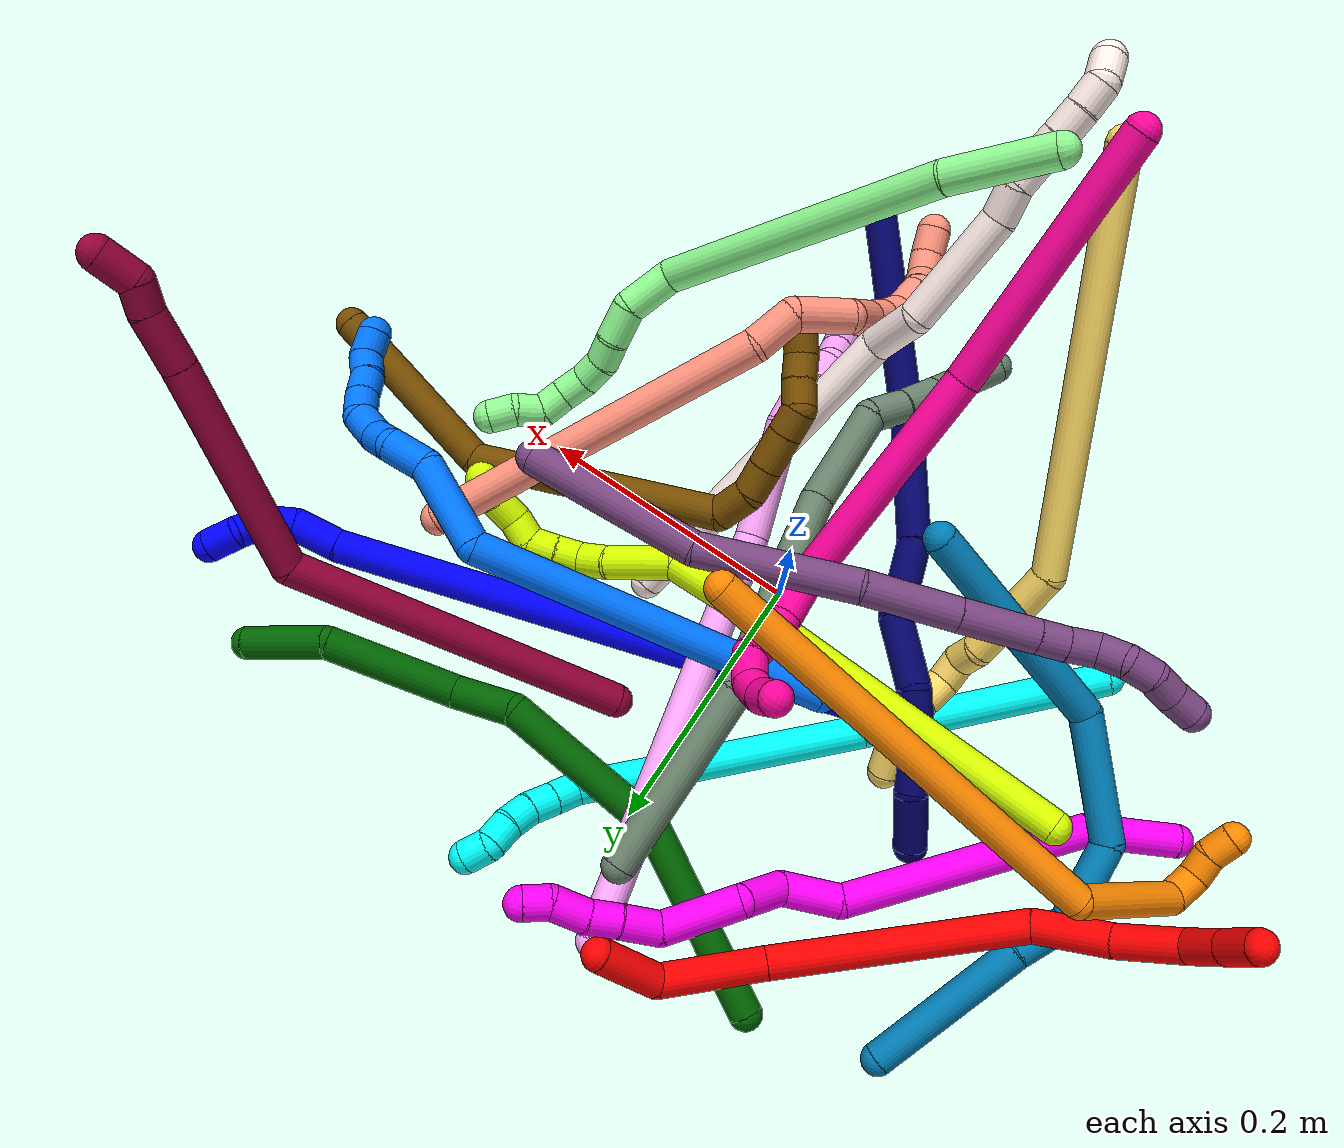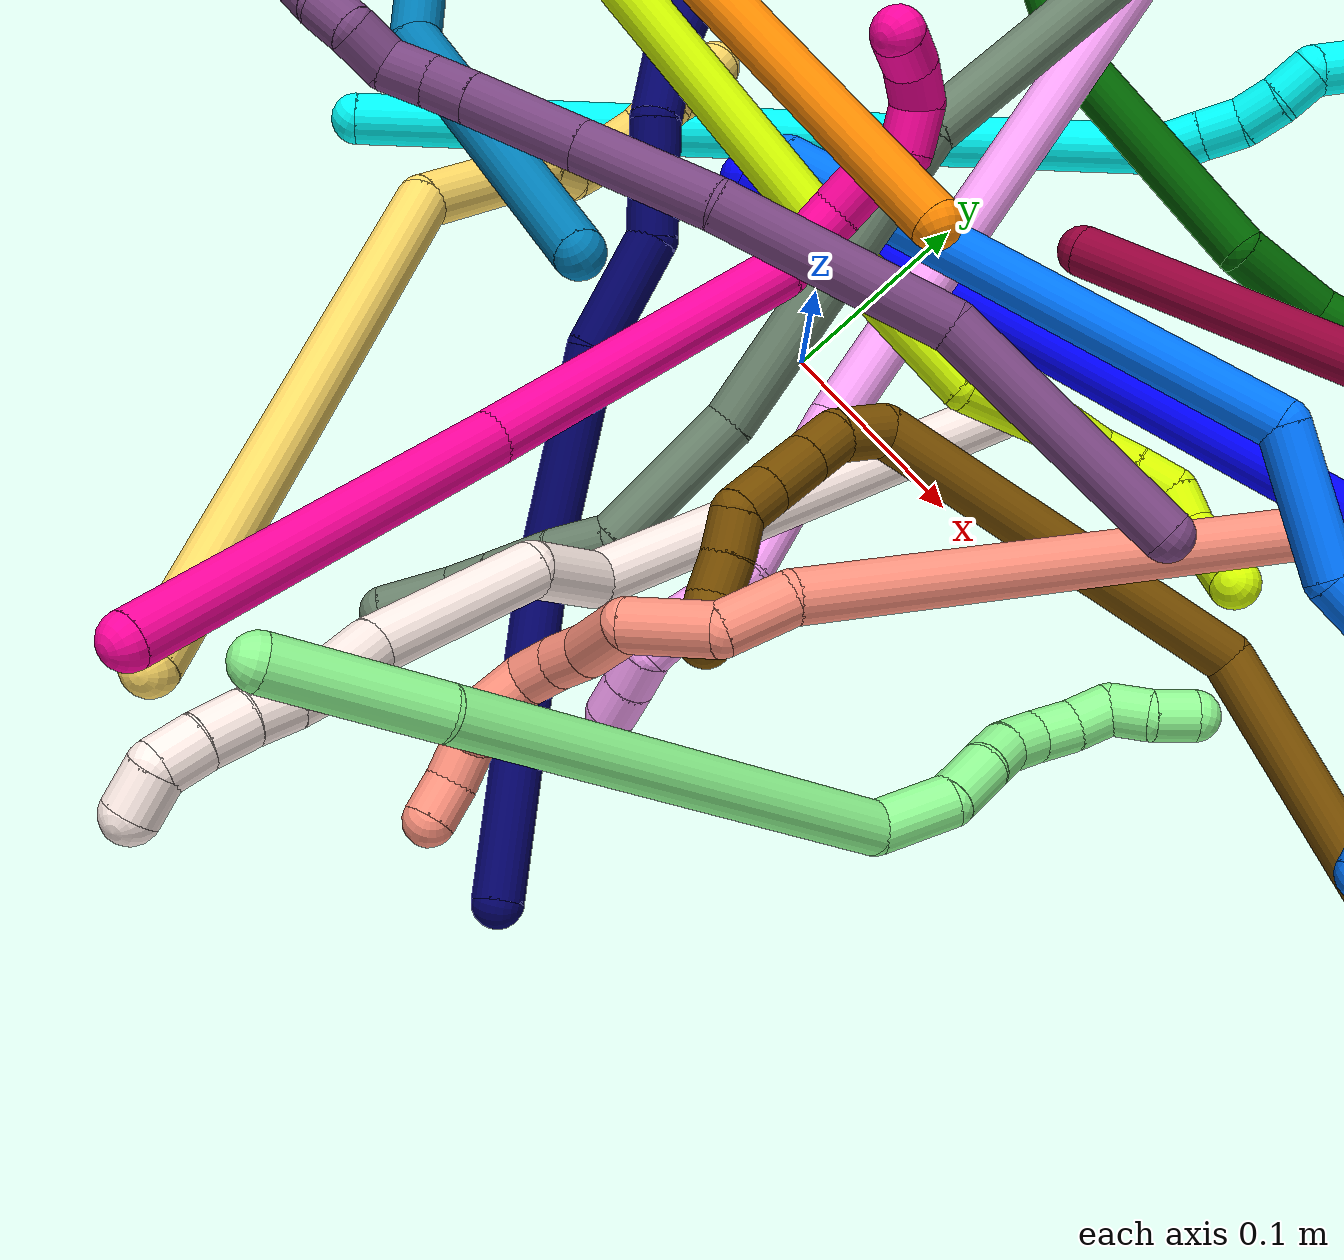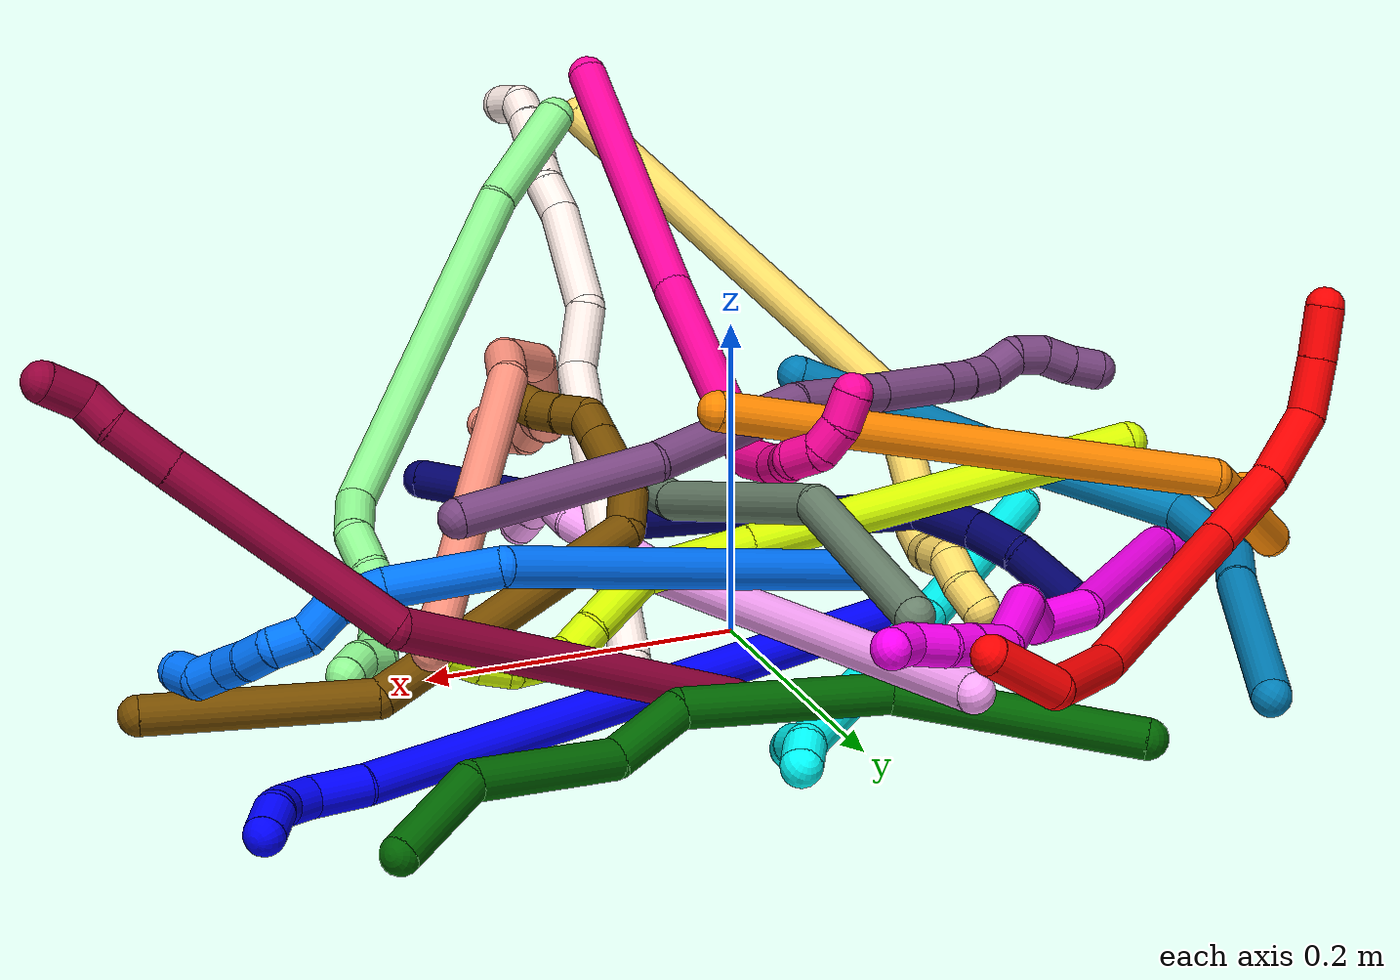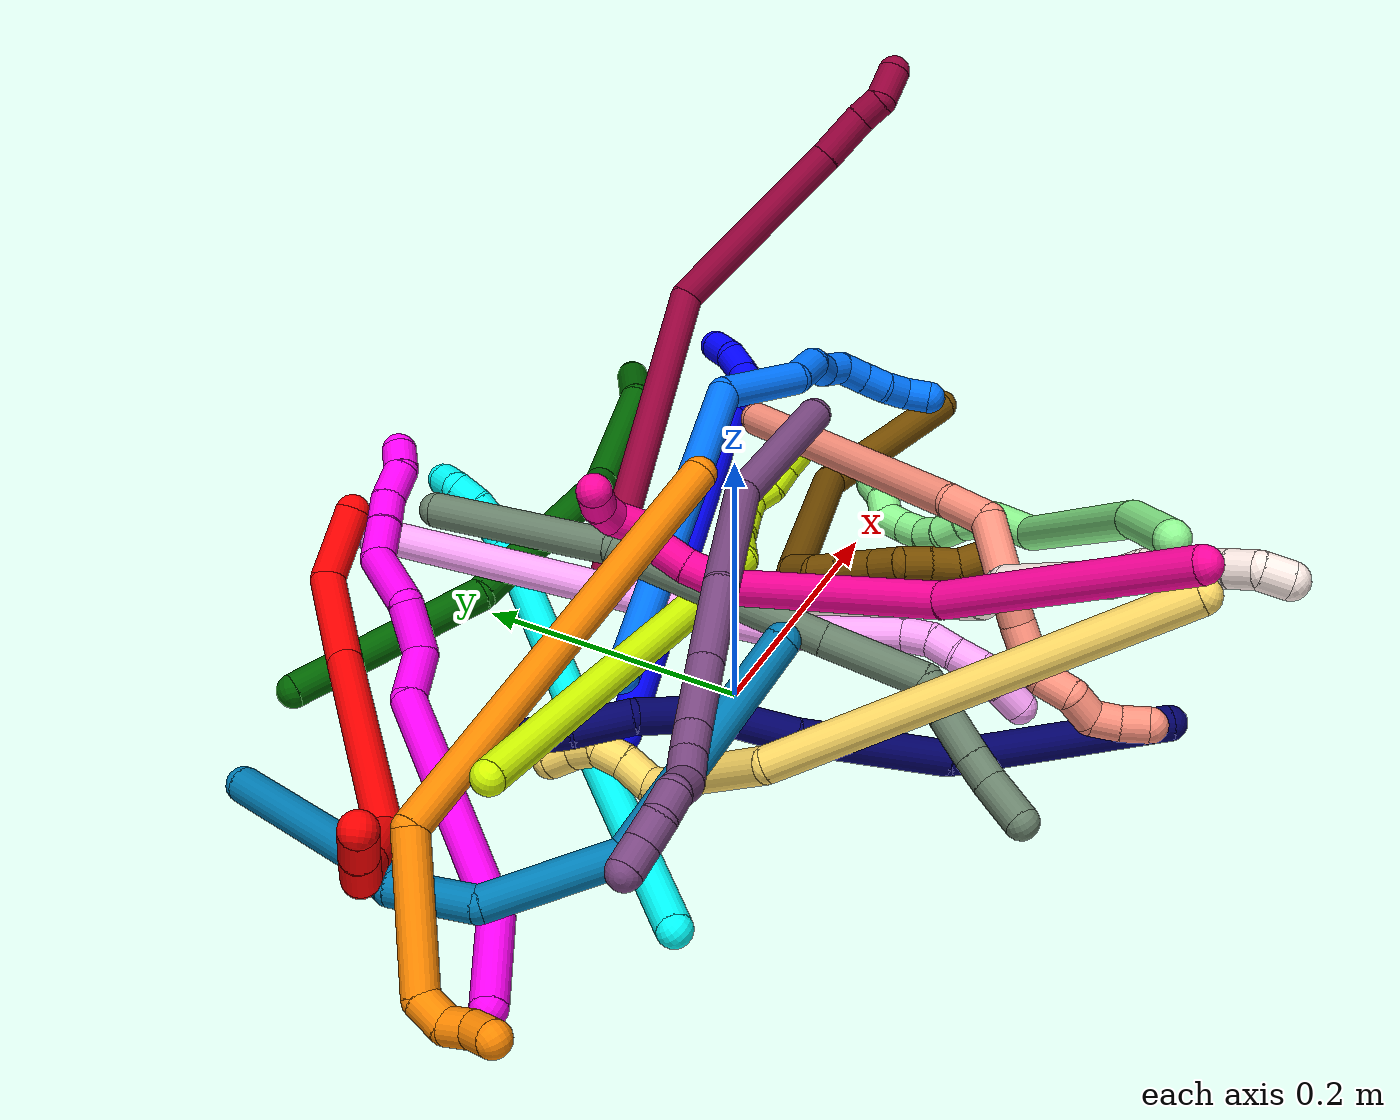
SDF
<sdf version="1.7">
 <world name="default">
  <plugin name="TubeGeneratorPlugin" filename="libtube_generator_plugin.so"/>
  <model name="photoneo_s_sensor">
   <static>1</static>
   <pose>0 0 2 1.57079 1.57079 3.14159</pose>
   <link name="link">
    <inertial><mass>0.1</mass></inertial>
    <sensor name="sensor" type="depth">
     <update_rate>30</update_rate>
     <camera>
      <horizontal_fov>1.22</horizontal_fov>
      <image><width>1920</width><height>1200</height><format>B8G8R8</format></image>
      <clip><near>0.1</near><far>4</far></clip>
      <depth_camera><output>points</output></depth_camera>
     </camera>
     <plugin name="camera_plugin" filename="libgazebo_ros_depth_camera.so">
      <baseline>0.2</baseline>
      <alwaysOn>1</alwaysOn>
      <updateRate>0.0</updateRate>
      <cameraName>camera_ir</cameraName>
      <imageTopicName>/camera/color/image_raw</imageTopicName>
      <cameraInfoTopicName>/camera/color/camera_info</cameraInfoTopicName>
      <depthImageTopicName>/camera/depth/image_raw</depthImageTopicName>
      <depthImageCameraInfoTopicName>/camera/depth/camera_info</depthImageCameraInfoTopicName>
      <pointCloudTopicName>/camera/depth/points</pointCloudTopicName>
      <frameName>fr_optical</frameName>
      <pointCloudCutoff>0.1</pointCloudCutoff>
      <pointCloudCutoffMax>2.0</pointCloudCutoffMax>
      <distortionK1>0</distortionK1>
      <distortionK2>0</distortionK2>
      <distortionK3>0</distortionK3>
      <distortionT1>0</distortionT1>
      <distortionT2>0</distortionT2>
      <CxPrime>0</CxPrime>
      <Cx>0</Cx>
      <Cy>0</Cy>
      <focalLength>0</focalLength>
      <hackBaseline>0</hackBaseline>
     </plugin>
    </sensor>
   </link>
  </model>
  <gravity>0 0 -9.8</gravity>
  <magnetic_field>6e-06 2.3e-05 -4.2e-05</magnetic_field>
  <atmosphere type="adiabatic"/>
  <physics name="default_physics" default="0" type="ode">
   <max_step_size>0.003</max_step_size>
   <real_time_factor>1</real_time_factor>
   <real_time_update_rate>1000</real_time_update_rate>
   <max_contacts>10000</max_contacts>
   <ode>
    <solver>
     <type>quick</type>
     <iters>100</iters>
     <sor>1.3</sor>
     <use_dynamic_moi_rescaling>0</use_dynamic_moi_rescaling>
    </solver>
    <constraints>
     <contact_max_correcting_vel>0</contact_max_correcting_vel>
     <contact_surface_layer>0.001</contact_surface_layer>
     <cfm>0</cfm>
     <erp>0.2</erp>
    </constraints>
   </ode>
  </physics>
  <scene><ambient>0.4 0.4 0.4 1</ambient><background>0.7 0.7 0.7 1</background><shadows>0</shadows></scene>
  <audio><device>default</device></audio>
  <spherical_coordinates>
   <surface_model>EARTH_WGS84</surface_model>
   <latitude_deg>0</latitude_deg>
   <longitude_deg>0</longitude_deg>
   <elevation>0</elevation>
   <heading_deg>0</heading_deg>
  </spherical_coordinates>
  <model name="bin">
   <static>1</static>
   <link name="bottom">
    <collision name="collision-bottom">
     <pose>0 0 -0.01 0 -0 0</pose>
     <geometry><box><size>0.8 0.6 0.02</size></box></geometry>
     <surface>
      <friction><ode><mu>100</mu><mu2>100</mu2></ode></friction>
      <contact><collide_bitmask>65535</collide_bitmask></contact>
     </surface>
    </collision>
   </link>
   <link name="west_wall">
    <collision name="collision-west_wall">
     <pose>-0.41 0 0.1 0 -0 0</pose>
     <geometry><box><size>0.02 0.6 0.2</size></box></geometry>
     <surface>
      <friction><ode><mu>100</mu><mu2>100</mu2></ode></friction>
      <contact><collide_bitmask>65535</collide_bitmask></contact>
     </surface>
    </collision>
   </link>
   <link name="east_wall">
    <collision name="collision-east_wall">
     <pose>0.41 0 0.1 0 -0 0</pose>
     <geometry><box><size>0.02 0.6 0.2</size></box></geometry>
     <surface>
      <friction><ode><mu>100</mu><mu2>100</mu2></ode></friction>
      <contact><collide_bitmask>65535</collide_bitmask></contact>
     </surface>
    </collision>
   </link>
   <link name="south_wall">
    <collision name="collision-south_wall">
     <pose>0 -0.31 0.1 0 -0 0</pose>
     <geometry><box><size>0.8 0.02 0.2</size></box></geometry>
     <surface>
      <friction><ode><mu>100</mu><mu2>100</mu2></ode></friction>
      <contact><collide_bitmask>65535</collide_bitmask></contact>
     </surface>
    </collision>
   </link>
   <link name="north_wall">
    <collision name="collision-north_wall">
     <pose>0 0.31 0.1 0 -0 0</pose>
     <geometry><box><size>0.8 0.02 0.2</size></box></geometry>
     <surface>
      <friction><ode><mu>100</mu><mu2>100</mu2></ode></friction>
      <contact><collide_bitmask>65535</collide_bitmask></contact>
     </surface>
    </collision>
   </link>
  </model>
  <model name="1">
   <static>0</static>
   <link name="1">
    <collision name="collision-cylinder-e_1_1_4">
     <pose>0.069106 0.020921 0.18423 -0.113077 0.356762 -0.020409</pose>
     <geometry><cylinder><radius>0.0125</radius><length>0.395748</length></cylinder></geometry>
     <surface>
      <friction><ode><mu>1.16</mu><mu2>1.16</mu2><slip1>0</slip1><slip2>0</slip2></ode></friction>
      <contact><ode><kp>1e+06</kp><kd>1</kd><max_vel>0</max_vel><min_depth>0.001</min_depth></ode></contact>
     </surface>
    </collision>
    <visual name="visual-cylinder-e_1_1_4">
     <pose>0.069106 0.020921 0.18423 -0.113077 0.356762 -0.020409</pose>
     <geometry><cylinder><radius>0.0125</radius><length>0.395748</length></cylinder></geometry>
     <material><ambient>0 0 1 1</ambient></material>
    </visual>
    <collision name="collision-cylinder-e_2_4_5">
     <pose>0.146995 0.044559 0.383687 -0.176541 0.516462 -0.046742</pose>
     <geometry><cylinder><radius>0.0125</radius><length>0.035574</length></cylinder></geometry>
     <surface>
      <friction><ode><mu>1.16</mu><mu2>1.16</mu2><slip1>0</slip1><slip2>0</slip2></ode></friction>
      <contact><ode><kp>1e+06</kp><kd>1</kd><max_vel>0</max_vel><min_depth>0.001</min_depth></ode></contact>
     </surface>
    </collision>
    <visual name="visual-cylinder-e_2_4_5">
     <pose>0.146995 0.044559 0.383687 -0.176541 0.516462 -0.046742</pose>
     <geometry><cylinder><radius>0.0125</radius><length>0.035574</length></cylinder></geometry>
     <material><ambient>0 0 1 1</ambient></material>
    </visual>
    <collision name="collision-cylinder-e_3_5_6">
     <pose>0.157932 0.046156 0.410403 0.097107 0.184378 0.008985</pose>
     <geometry><cylinder><radius>0.0125</radius><length>0.023487</length></cylinder></geometry>
     <surface>
      <friction><ode><mu>1.16</mu><mu2>1.16</mu2><slip1>0</slip1><slip2>0</slip2></ode></friction>
      <contact><ode><kp>1e+06</kp><kd>1</kd><max_vel>0</max_vel><min_depth>0.001</min_depth></ode></contact>
     </surface>
    </collision>
    <visual name="visual-cylinder-e_3_5_6">
     <pose>0.157932 0.046156 0.410403 0.097107 0.184378 0.008985</pose>
     <geometry><cylinder><radius>0.0125</radius><length>0.023487</length></cylinder></geometry>
     <material><ambient>0 0 1 1</ambient></material>
    </visual>
    <collision name="collision-cylinder-e_4_6_7">
     <pose>0.157686 0.040534 0.431244 0.448841 -0.227123 -0.052057</pose>
     <geometry><cylinder><radius>0.0125</radius><length>0.021304</length></cylinder></geometry>
     <surface>
      <friction><ode><mu>1.16</mu><mu2>1.16</mu2><slip1>0</slip1><slip2>0</slip2></ode></friction>
      <contact><ode><kp>1e+06</kp><kd>1</kd><max_vel>0</max_vel><min_depth>0.001</min_depth></ode></contact>
     </surface>
    </collision>
    <visual name="visual-cylinder-e_4_6_7">
     <pose>0.157686 0.040534 0.431244 0.448841 -0.227123 -0.052057</pose>
     <geometry><cylinder><radius>0.0125</radius><length>0.021304</length></cylinder></geometry>
     <material><ambient>0 0 1 1</ambient></material>
    </visual>
    <collision name="collision-cylinder-e_5_7_2">
     <pose>0.150966 0.036152 0.451728 -0.010966 -0.370244 0.002054</pose>
     <geometry><cylinder><radius>0.0125</radius><length>0.023887</length></cylinder></geometry>
     <surface>
      <friction><ode><mu>1.16</mu><mu2>1.16</mu2><slip1>0</slip1><slip2>0</slip2></ode></friction>
      <contact><ode><kp>1e+06</kp><kd>1</kd><max_vel>0</max_vel><min_depth>0.001</min_depth></ode></contact>
     </surface>
    </collision>
    <visual name="visual-cylinder-e_5_7_2">
     <pose>0.150966 0.036152 0.451728 -0.010966 -0.370244 0.002054</pose>
     <geometry><cylinder><radius>0.0125</radius><length>0.023887</length></cylinder></geometry>
     <material><ambient>0 0 1 1</ambient></material>
    </visual>
    <collision name="collision-sphere-2">
     <pose>0.146644 0.036274 0.462862 0 -0 0</pose>
     <geometry><sphere><radius>0.0125</radius></sphere></geometry>
     <surface>
      <friction><ode><mu>1.16</mu><mu2>1.16</mu2><slip1>0</slip1><slip2>0</slip2></ode></friction>
      <contact><ode><kp>1e+06</kp><kd>1</kd><max_vel>0</max_vel><min_depth>0.001</min_depth></ode></contact>
     </surface>
    </collision>
    <visual name="visual-sphere-2">
     <pose>0.146644 0.036274 0.462862 0 -0 0</pose>
     <geometry><sphere><radius>0.0125</radius></sphere></geometry>
     <material><ambient>0 0 1 1</ambient></material>
    </visual>
    <collision name="collision-sphere-7">
     <pose>0.155287 0.03603 0.440595 0 -0 0</pose>
     <geometry><sphere><radius>0.0125</radius></sphere></geometry>
     <surface>
      <friction><ode><mu>1.16</mu><mu2>1.16</mu2><slip1>0</slip1><slip2>0</slip2></ode></friction>
      <contact><ode><kp>1e+06</kp><kd>1</kd><max_vel>0</max_vel><min_depth>0.001</min_depth></ode></contact>
     </surface>
    </collision>
    <visual name="visual-sphere-7">
     <pose>0.155287 0.03603 0.440595 0 -0 0</pose>
     <geometry><sphere><radius>0.0125</radius></sphere></geometry>
     <material><ambient>0 0 1 1</ambient></material>
    </visual>
    <collision name="collision-sphere-6">
     <pose>0.160084 0.045037 0.421893 0 -0 0</pose>
     <geometry><sphere><radius>0.0125</radius></sphere></geometry>
     <surface>
      <friction><ode><mu>1.16</mu><mu2>1.16</mu2><slip1>0</slip1><slip2>0</slip2></ode></friction>
      <contact><ode><kp>1e+06</kp><kd>1</kd><max_vel>0</max_vel><min_depth>0.001</min_depth></ode></contact>
     </surface>
    </collision>
    <visual name="visual-sphere-6">
     <pose>0.160084 0.045037 0.421893 0 -0 0</pose>
     <geometry><sphere><radius>0.0125</radius></sphere></geometry>
     <material><ambient>0 0 1 1</ambient></material>
    </visual>
    <collision name="collision-sphere-5">
     <pose>0.155779 0.047276 0.398913 0 -0 0</pose>
     <geometry><sphere><radius>0.0125</radius></sphere></geometry>
     <surface>
      <friction><ode><mu>1.16</mu><mu2>1.16</mu2><slip1>0</slip1><slip2>0</slip2></ode></friction>
      <contact><ode><kp>1e+06</kp><kd>1</kd><max_vel>0</max_vel><min_depth>0.001</min_depth></ode></contact>
     </surface>
    </collision>
    <visual name="visual-sphere-5">
     <pose>0.155779 0.047276 0.398913 0 -0 0</pose>
     <geometry><sphere><radius>0.0125</radius></sphere></geometry>
     <material><ambient>0 0 1 1</ambient></material>
    </visual>
    <collision name="collision-sphere-1">
     <geometry><sphere><radius>0.0125</radius></sphere></geometry>
     <surface>
      <friction><ode><mu>1.16</mu><mu2>1.16</mu2><slip1>0</slip1><slip2>0</slip2></ode></friction>
      <contact><ode><kp>1e+06</kp><kd>1</kd><max_vel>0</max_vel><min_depth>0.001</min_depth></ode></contact>
     </surface>
    </collision>
    <visual name="visual-sphere-1">
     <geometry><sphere><radius>0.0125</radius></sphere></geometry>
     <material><ambient>0 0 1 1</ambient></material>
    </visual>
    <collision name="collision-sphere-4">
     <pose>0.138212 0.041843 0.36846 0 -0 0</pose>
     <geometry><sphere><radius>0.0125</radius></sphere></geometry>
     <surface>
      <friction><ode><mu>1.16</mu><mu2>1.16</mu2><slip1>0</slip1><slip2>0</slip2></ode></friction>
      <contact><ode><kp>1e+06</kp><kd>1</kd><max_vel>0</max_vel><min_depth>0.001</min_depth></ode></contact>
     </surface>
    </collision>
    <visual name="visual-sphere-4">
     <pose>0.138212 0.041843 0.36846 0 -0 0</pose>
     <geometry><sphere><radius>0.0125</radius></sphere></geometry>
     <material><ambient>0 0 1 1</ambient></material>
    </visual>
    <inertial>
     <pose>0.086505 0.025352 0.23235 0 -0 0</pose>
     <mass>0.5</mass>
     <inertia>
      <ixx>0.004775</ixx>
      <ixy>0</ixy>
      <ixz>0</ixz>
      <iyy>0.005065</iyy>
      <iyz>0</iyz>
      <izz>-0.002323</izz>
     </inertia>
    </inertial>
   </link>
   <pose>-0.085869 0.041513 0.012552 -1.59824 -0.356379 -0.895614</pose>
  </model>
  <model name="2">
   <static>0</static>
   <link name="2">
    <collision name="collision-cylinder-e_1_1_4">
     <pose>-0.005003 0.003401 -0.025767 -3.01035 -0.190166 1.93491</pose>
     <geometry><cylinder><radius>0.0125</radius><length>0.052936</length></cylinder></geometry>
     <surface>
      <friction><ode><mu>1.16</mu><mu2>1.16</mu2><slip1>0</slip1><slip2>0</slip2></ode></friction>
      <contact><ode><kp>1e+06</kp><kd>1</kd><max_vel>0</max_vel><min_depth>0.001</min_depth></ode></contact>
     </surface>
    </collision>
    <visual name="visual-cylinder-e_1_1_4">
     <pose>-0.005003 0.003401 -0.025767 -3.01035 -0.190166 1.93491</pose>
     <geometry><cylinder><radius>0.0125</radius><length>0.052936</length></cylinder></geometry>
     <material><ambient>1 0 0 1</ambient></material>
    </visual>
    <collision name="collision-cylinder-e_2_4_5">
     <pose>-0.022686 -0.013612 -0.082626 2.5606 -0.328542 -1.01255</pose>
     <geometry><cylinder><radius>0.0125</radius><length>0.078593</length></cylinder></geometry>
     <surface>
      <friction><ode><mu>1.16</mu><mu2>1.16</mu2><slip1>0</slip1><slip2>0</slip2></ode></friction>
      <contact><ode><kp>1e+06</kp><kd>1</kd><max_vel>0</max_vel><min_depth>0.001</min_depth></ode></contact>
     </surface>
    </collision>
    <visual name="visual-cylinder-e_2_4_5">
     <pose>-0.022686 -0.013612 -0.082626 2.5606 -0.328542 -1.01255</pose>
     <geometry><cylinder><radius>0.0125</radius><length>0.078593</length></cylinder></geometry>
     <material><ambient>1 0 0 1</ambient></material>
    </visual>
    <collision name="collision-cylinder-e_3_5_6">
     <pose>-0.082667 -0.089174 -0.173765 2.39871 -0.525725 -1.20907</pose>
     <geometry><cylinder><radius>0.0125</radius><length>0.188514</length></cylinder></geometry>
     <surface>
      <friction><ode><mu>1.16</mu><mu2>1.16</mu2><slip1>0</slip1><slip2>0</slip2></ode></friction>
      <contact><ode><kp>1e+06</kp><kd>1</kd><max_vel>0</max_vel><min_depth>0.001</min_depth></ode></contact>
     </surface>
    </collision>
    <visual name="visual-cylinder-e_3_5_6">
     <pose>-0.082667 -0.089174 -0.173765 2.39871 -0.525725 -1.20907</pose>
     <geometry><cylinder><radius>0.0125</radius><length>0.188514</length></cylinder></geometry>
     <material><ambient>1 0 0 1</ambient></material>
    </visual>
    <collision name="collision-cylinder-e_4_6_7">
     <pose>-0.154945 -0.155369 -0.244168 2.32384 -1.02578 -1.82998</pose>
     <geometry><cylinder><radius>0.0125</radius><length>0.058414</length></cylinder></geometry>
     <surface>
      <friction><ode><mu>1.16</mu><mu2>1.16</mu2><slip1>0</slip1><slip2>0</slip2></ode></friction>
      <contact><ode><kp>1e+06</kp><kd>1</kd><max_vel>0</max_vel><min_depth>0.001</min_depth></ode></contact>
     </surface>
    </collision>
    <visual name="visual-cylinder-e_4_6_7">
     <pose>-0.154945 -0.155369 -0.244168 2.32384 -1.02578 -1.82998</pose>
     <geometry><cylinder><radius>0.0125</radius><length>0.058414</length></cylinder></geometry>
     <material><ambient>1 0 0 1</ambient></material>
    </visual>
    <collision name="collision-cylinder-e_5_7_8">
     <pose>-0.20191 -0.178974 -0.260304 2.00226 -1.00955 -1.42358</pose>
     <geometry><cylinder><radius>0.0125</radius><length>0.051949</length></cylinder></geometry>
     <surface>
      <friction><ode><mu>1.16</mu><mu2>1.16</mu2><slip1>0</slip1><slip2>0</slip2></ode></friction>
      <contact><ode><kp>1e+06</kp><kd>1</kd><max_vel>0</max_vel><min_depth>0.001</min_depth></ode></contact>
     </surface>
    </collision>
    <visual name="visual-cylinder-e_5_7_8">
     <pose>-0.20191 -0.178974 -0.260304 2.00226 -1.00955 -1.42358</pose>
     <geometry><cylinder><radius>0.0125</radius><length>0.051949</length></cylinder></geometry>
     <material><ambient>1 0 0 1</ambient></material>
    </visual>
    <collision name="collision-cylinder-e_6_8_9">
     <pose>-0.239031 -0.199711 -0.260248 0.950901 -0.984536 -0.5388</pose>
     <geometry><cylinder><radius>0.0125</radius><length>0.036327</length></cylinder></geometry>
     <surface>
      <friction><ode><mu>1.16</mu><mu2>1.16</mu2><slip1>0</slip1><slip2>0</slip2></ode></friction>
      <contact><ode><kp>1e+06</kp><kd>1</kd><max_vel>0</max_vel><min_depth>0.001</min_depth></ode></contact>
     </surface>
    </collision>
    <visual name="visual-cylinder-e_6_8_9">
     <pose>-0.239031 -0.199711 -0.260248 0.950901 -0.984536 -0.5388</pose>
     <geometry><cylinder><radius>0.0125</radius><length>0.036327</length></cylinder></geometry>
     <material><ambient>1 0 0 1</ambient></material>
    </visual>
    <collision name="collision-cylinder-e_7_9_2">
     <pose>-0.267611 -0.215315 -0.248035 0.86134 -0.941807 -0.459535</pose>
     <geometry><cylinder><radius>0.0125</radius><length>0.033266</length></cylinder></geometry>
     <surface>
      <friction><ode><mu>1.16</mu><mu2>1.16</mu2><slip1>0</slip1><slip2>0</slip2></ode></friction>
      <contact><ode><kp>1e+06</kp><kd>1</kd><max_vel>0</max_vel><min_depth>0.001</min_depth></ode></contact>
     </surface>
    </collision>
    <visual name="visual-cylinder-e_7_9_2">
     <pose>-0.267611 -0.215315 -0.248035 0.86134 -0.941807 -0.459535</pose>
     <geometry><cylinder><radius>0.0125</radius><length>0.033266</length></cylinder></geometry>
     <material><ambient>1 0 0 1</ambient></material>
    </visual>
    <collision name="collision-sphere-2">
     <pose>-0.281061 -0.22274 -0.241661 0 -0 0</pose>
     <geometry><sphere><radius>0.0125</radius></sphere></geometry>
     <surface>
      <friction><ode><mu>1.16</mu><mu2>1.16</mu2><slip1>0</slip1><slip2>0</slip2></ode></friction>
      <contact><ode><kp>1e+06</kp><kd>1</kd><max_vel>0</max_vel><min_depth>0.001</min_depth></ode></contact>
     </surface>
    </collision>
    <visual name="visual-sphere-2">
     <pose>-0.281061 -0.22274 -0.241661 0 -0 0</pose>
     <geometry><sphere><radius>0.0125</radius></sphere></geometry>
     <material><ambient>1 0 0 1</ambient></material>
    </visual>
    <collision name="collision-sphere-9">
     <pose>-0.254161 -0.207891 -0.25441 0 -0 0</pose>
     <geometry><sphere><radius>0.0125</radius></sphere></geometry>
     <surface>
      <friction><ode><mu>1.16</mu><mu2>1.16</mu2><slip1>0</slip1><slip2>0</slip2></ode></friction>
      <contact><ode><kp>1e+06</kp><kd>1</kd><max_vel>0</max_vel><min_depth>0.001</min_depth></ode></contact>
     </surface>
    </collision>
    <visual name="visual-sphere-9">
     <pose>-0.254161 -0.207891 -0.25441 0 -0 0</pose>
     <geometry><sphere><radius>0.0125</radius></sphere></geometry>
     <material><ambient>1 0 0 1</ambient></material>
    </visual>
    <collision name="collision-sphere-4">
     <pose>-0.010006 0.006803 -0.051534 0 -0 0</pose>
     <geometry><sphere><radius>0.0125</radius></sphere></geometry>
     <surface>
      <friction><ode><mu>1.16</mu><mu2>1.16</mu2><slip1>0</slip1><slip2>0</slip2></ode></friction>
      <contact><ode><kp>1e+06</kp><kd>1</kd><max_vel>0</max_vel><min_depth>0.001</min_depth></ode></contact>
     </surface>
    </collision>
    <visual name="visual-sphere-4">
     <pose>-0.010006 0.006803 -0.051534 0 -0 0</pose>
     <geometry><sphere><radius>0.0125</radius></sphere></geometry>
     <material><ambient>1 0 0 1</ambient></material>
    </visual>
    <collision name="collision-sphere-1">
     <geometry><sphere><radius>0.0125</radius></sphere></geometry>
     <surface>
      <friction><ode><mu>1.16</mu><mu2>1.16</mu2><slip1>0</slip1><slip2>0</slip2></ode></friction>
      <contact><ode><kp>1e+06</kp><kd>1</kd><max_vel>0</max_vel><min_depth>0.001</min_depth></ode></contact>
     </surface>
    </collision>
    <visual name="visual-sphere-1">
     <geometry><sphere><radius>0.0125</radius></sphere></geometry>
     <material><ambient>1 0 0 1</ambient></material>
    </visual>
    <collision name="collision-sphere-8">
     <pose>-0.2239 -0.191532 -0.266086 0 -0 0</pose>
     <geometry><sphere><radius>0.0125</radius></sphere></geometry>
     <surface>
      <friction><ode><mu>1.16</mu><mu2>1.16</mu2><slip1>0</slip1><slip2>0</slip2></ode></friction>
      <contact><ode><kp>1e+06</kp><kd>1</kd><max_vel>0</max_vel><min_depth>0.001</min_depth></ode></contact>
     </surface>
    </collision>
    <visual name="visual-sphere-8">
     <pose>-0.2239 -0.191532 -0.266086 0 -0 0</pose>
     <geometry><sphere><radius>0.0125</radius></sphere></geometry>
     <material><ambient>1 0 0 1</ambient></material>
    </visual>
    <collision name="collision-sphere-5">
     <pose>-0.035365 -0.034027 -0.113718 0 -0 0</pose>
     <geometry><sphere><radius>0.0125</radius></sphere></geometry>
     <surface>
      <friction><ode><mu>1.16</mu><mu2>1.16</mu2><slip1>0</slip1><slip2>0</slip2></ode></friction>
      <contact><ode><kp>1e+06</kp><kd>1</kd><max_vel>0</max_vel><min_depth>0.001</min_depth></ode></contact>
     </surface>
    </collision>
    <visual name="visual-sphere-5">
     <pose>-0.035365 -0.034027 -0.113718 0 -0 0</pose>
     <geometry><sphere><radius>0.0125</radius></sphere></geometry>
     <material><ambient>1 0 0 1</ambient></material>
    </visual>
    <collision name="collision-sphere-6">
     <pose>-0.129969 -0.144321 -0.233813 0 -0 0</pose>
     <geometry><sphere><radius>0.0125</radius></sphere></geometry>
     <surface>
      <friction><ode><mu>1.16</mu><mu2>1.16</mu2><slip1>0</slip1><slip2>0</slip2></ode></friction>
      <contact><ode><kp>1e+06</kp><kd>1</kd><max_vel>0</max_vel><min_depth>0.001</min_depth></ode></contact>
     </surface>
    </collision>
    <visual name="visual-sphere-6">
     <pose>-0.129969 -0.144321 -0.233813 0 -0 0</pose>
     <geometry><sphere><radius>0.0125</radius></sphere></geometry>
     <material><ambient>1 0 0 1</ambient></material>
    </visual>
    <collision name="collision-sphere-7">
     <pose>-0.17992 -0.166417 -0.254523 0 -0 0</pose>
     <geometry><sphere><radius>0.0125</radius></sphere></geometry>
     <surface>
      <friction><ode><mu>1.16</mu><mu2>1.16</mu2><slip1>0</slip1><slip2>0</slip2></ode></friction>
      <contact><ode><kp>1e+06</kp><kd>1</kd><max_vel>0</max_vel><min_depth>0.001</min_depth></ode></contact>
     </surface>
    </collision>
    <visual name="visual-sphere-7">
     <pose>-0.17992 -0.166417 -0.254523 0 -0 0</pose>
     <geometry><sphere><radius>0.0125</radius></sphere></geometry>
     <material><ambient>1 0 0 1</ambient></material>
    </visual>
    <inertial>
     <pose>-0.109515 -0.100983 -0.172212 0 -0 0</pose>
     <mass>0.5</mass>
     <inertia>
      <ixx>-0.000327</ixx>
      <ixy>0</ixy>
      <ixz>0</ixz>
      <iyy>-0.000459</iyy>
      <iyz>0</iyz>
      <izz>0.000687</izz>
     </inertia>
    </inertial>
   </link>
   <pose>-0.039751 0.287612 0.089211 -0.34295 0.762435 -0.139442</pose>
  </model>
  <model name="3">
   <static>0</static>
   <link name="3">
    <collision name="collision-cylinder-e_1_1_4">
     <pose>0.067872 0.055025 0.029699 -1.07587 0.826359 -0.511678</pose>
     <geometry><cylinder><radius>0.0125</radius><length>0.184569</length></cylinder></geometry>
     <surface>
      <friction><ode><mu>1.16</mu><mu2>1.16</mu2><slip1>0</slip1><slip2>0</slip2></ode></friction>
      <contact><ode><kp>1e+06</kp><kd>1</kd><max_vel>0</max_vel><min_depth>0.001</min_depth></ode></contact>
     </surface>
    </collision>
    <visual name="visual-cylinder-e_1_1_4">
     <pose>0.067872 0.055025 0.029699 -1.07587 0.826359 -0.511678</pose>
     <geometry><cylinder><radius>0.0125</radius><length>0.184569</length></cylinder></geometry>
     <material><ambient>0.003922 1 0.996078 1</ambient></material>
    </visual>
    <collision name="collision-cylinder-e_2_4_5">
     <pose>0.216103 0.171322 0.095961 -1.03278 0.844693 -0.499645</pose>
     <geometry><cylinder><radius>0.0125</radius><length>0.214928</length></cylinder></geometry>
     <surface>
      <friction><ode><mu>1.16</mu><mu2>1.16</mu2><slip1>0</slip1><slip2>0</slip2></ode></friction>
      <contact><ode><kp>1e+06</kp><kd>1</kd><max_vel>0</max_vel><min_depth>0.001</min_depth></ode></contact>
     </surface>
    </collision>
    <visual name="visual-cylinder-e_2_4_5">
     <pose>0.216103 0.171322 0.095961 -1.03278 0.844693 -0.499645</pose>
     <geometry><cylinder><radius>0.0125</radius><length>0.214928</length></cylinder></geometry>
     <material><ambient>0.003922 1 0.996078 1</ambient></material>
    </visual>
    <collision name="collision-cylinder-e_3_5_6">
     <pose>0.302114 0.236546 0.139971 -0.487964 0.590634 -0.151174</pose>
     <geometry><cylinder><radius>0.0125</radius><length>0.020302</length></cylinder></geometry>
     <surface>
      <friction><ode><mu>1.16</mu><mu2>1.16</mu2><slip1>0</slip1><slip2>0</slip2></ode></friction>
      <contact><ode><kp>1e+06</kp><kd>1</kd><max_vel>0</max_vel><min_depth>0.001</min_depth></ode></contact>
     </surface>
    </collision>
    <visual name="visual-cylinder-e_3_5_6">
     <pose>0.302114 0.236546 0.139971 -0.487964 0.590634 -0.151174</pose>
     <geometry><cylinder><radius>0.0125</radius><length>0.020302</length></cylinder></geometry>
     <material><ambient>0.003922 1 0.996078 1</ambient></material>
    </visual>
    <collision name="collision-cylinder-e_4_6_7">
     <pose>0.313516 0.244114 0.15478 -0.456487 0.611381 -0.146352</pose>
     <geometry><cylinder><radius>0.0125</radius><length>0.020031</length></cylinder></geometry>
     <surface>
      <friction><ode><mu>1.16</mu><mu2>1.16</mu2><slip1>0</slip1><slip2>0</slip2></ode></friction>
      <contact><ode><kp>1e+06</kp><kd>1</kd><max_vel>0</max_vel><min_depth>0.001</min_depth></ode></contact>
     </surface>
    </collision>
    <visual name="visual-cylinder-e_4_6_7">
     <pose>0.313516 0.244114 0.15478 -0.456487 0.611381 -0.146352</pose>
     <geometry><cylinder><radius>0.0125</radius><length>0.020031</length></cylinder></geometry>
     <material><ambient>0.003922 1 0.996078 1</ambient></material>
    </visual>
    <collision name="collision-cylinder-e_5_7_8">
     <pose>0.322857 0.251344 0.170831 -0.394187 0.36465 -0.0736</pose>
     <geometry><cylinder><radius>0.0125</radius><length>0.020148</length></cylinder></geometry>
     <surface>
      <friction><ode><mu>1.16</mu><mu2>1.16</mu2><slip1>0</slip1><slip2>0</slip2></ode></friction>
      <contact><ode><kp>1e+06</kp><kd>1</kd><max_vel>0</max_vel><min_depth>0.001</min_depth></ode></contact>
     </surface>
    </collision>
    <visual name="visual-cylinder-e_5_7_8">
     <pose>0.322857 0.251344 0.170831 -0.394187 0.36465 -0.0736</pose>
     <geometry><cylinder><radius>0.0125</radius><length>0.020148</length></cylinder></geometry>
     <material><ambient>0.003922 1 0.996078 1</ambient></material>
    </visual>
    <collision name="collision-cylinder-e_6_8_9">
     <pose>0.328272 0.260068 0.187932 -0.54596 0.183077 -0.051388</pose>
     <geometry><cylinder><radius>0.0125</radius><length>0.020018</length></cylinder></geometry>
     <surface>
      <friction><ode><mu>1.16</mu><mu2>1.16</mu2><slip1>0</slip1><slip2>0</slip2></ode></friction>
      <contact><ode><kp>1e+06</kp><kd>1</kd><max_vel>0</max_vel><min_depth>0.001</min_depth></ode></contact>
     </surface>
    </collision>
    <visual name="visual-cylinder-e_6_8_9">
     <pose>0.328272 0.260068 0.187932 -0.54596 0.183077 -0.051388</pose>
     <geometry><cylinder><radius>0.0125</radius><length>0.020018</length></cylinder></geometry>
     <material><ambient>0.003922 1 0.996078 1</ambient></material>
    </visual>
    <collision name="collision-cylinder-e_7_9_2">
     <pose>0.335176 0.273342 0.199094 -1.24576 0.532994 -0.387248</pose>
     <geometry><cylinder><radius>0.0125</radius><length>0.020004</length></cylinder></geometry>
     <surface>
      <friction><ode><mu>1.16</mu><mu2>1.16</mu2><slip1>0</slip1><slip2>0</slip2></ode></friction>
      <contact><ode><kp>1e+06</kp><kd>1</kd><max_vel>0</max_vel><min_depth>0.001</min_depth></ode></contact>
     </surface>
    </collision>
    <visual name="visual-cylinder-e_7_9_2">
     <pose>0.335176 0.273342 0.199094 -1.24576 0.532994 -0.387248</pose>
     <geometry><cylinder><radius>0.0125</radius><length>0.020004</length></cylinder></geometry>
     <material><ambient>0.003922 1 0.996078 1</ambient></material>
    </visual>
    <collision name="collision-sphere-2">
     <pose>0.340259 0.281506 0.201845 0 -0 0</pose>
     <geometry><sphere><radius>0.0125</radius></sphere></geometry>
     <surface>
      <friction><ode><mu>1.16</mu><mu2>1.16</mu2><slip1>0</slip1><slip2>0</slip2></ode></friction>
      <contact><ode><kp>1e+06</kp><kd>1</kd><max_vel>0</max_vel><min_depth>0.001</min_depth></ode></contact>
     </surface>
    </collision>
    <visual name="visual-sphere-2">
     <pose>0.340259 0.281506 0.201845 0 -0 0</pose>
     <geometry><sphere><radius>0.0125</radius></sphere></geometry>
     <material><ambient>0.003922 1 0.996078 1</ambient></material>
    </visual>
    <collision name="collision-sphere-9">
     <pose>0.330094 0.265179 0.196343 0 -0 0</pose>
     <geometry><sphere><radius>0.0125</radius></sphere></geometry>
     <surface>
      <friction><ode><mu>1.16</mu><mu2>1.16</mu2><slip1>0</slip1><slip2>0</slip2></ode></friction>
      <contact><ode><kp>1e+06</kp><kd>1</kd><max_vel>0</max_vel><min_depth>0.001</min_depth></ode></contact>
     </surface>
    </collision>
    <visual name="visual-sphere-9">
     <pose>0.330094 0.265179 0.196343 0 -0 0</pose>
     <geometry><sphere><radius>0.0125</radius></sphere></geometry>
     <material><ambient>0.003922 1 0.996078 1</ambient></material>
    </visual>
    <collision name="collision-sphere-4">
     <pose>0.135745 0.11005 0.059397 0 -0 0</pose>
     <geometry><sphere><radius>0.0125</radius></sphere></geometry>
     <surface>
      <friction><ode><mu>1.16</mu><mu2>1.16</mu2><slip1>0</slip1><slip2>0</slip2></ode></friction>
      <contact><ode><kp>1e+06</kp><kd>1</kd><max_vel>0</max_vel><min_depth>0.001</min_depth></ode></contact>
     </surface>
    </collision>
    <visual name="visual-sphere-4">
     <pose>0.135745 0.11005 0.059397 0 -0 0</pose>
     <geometry><sphere><radius>0.0125</radius></sphere></geometry>
     <material><ambient>0.003922 1 0.996078 1</ambient></material>
    </visual>
    <collision name="collision-sphere-1">
     <geometry><sphere><radius>0.0125</radius></sphere></geometry>
     <surface>
      <friction><ode><mu>1.16</mu><mu2>1.16</mu2><slip1>0</slip1><slip2>0</slip2></ode></friction>
      <contact><ode><kp>1e+06</kp><kd>1</kd><max_vel>0</max_vel><min_depth>0.001</min_depth></ode></contact>
     </surface>
    </collision>
    <visual name="visual-sphere-1">
     <geometry><sphere><radius>0.0125</radius></sphere></geometry>
     <material><ambient>0.003922 1 0.996078 1</ambient></material>
    </visual>
    <collision name="collision-sphere-8">
     <pose>0.32645 0.254958 0.179521 0 -0 0</pose>
     <geometry><sphere><radius>0.0125</radius></sphere></geometry>
     <surface>
      <friction><ode><mu>1.16</mu><mu2>1.16</mu2><slip1>0</slip1><slip2>0</slip2></ode></friction>
      <contact><ode><kp>1e+06</kp><kd>1</kd><max_vel>0</max_vel><min_depth>0.001</min_depth></ode></contact>
     </surface>
    </collision>
    <visual name="visual-sphere-8">
     <pose>0.32645 0.254958 0.179521 0 -0 0</pose>
     <geometry><sphere><radius>0.0125</radius></sphere></geometry>
     <material><ambient>0.003922 1 0.996078 1</ambient></material>
    </visual>
    <collision name="collision-sphere-5">
     <pose>0.296461 0.232593 0.132524 0 -0 0</pose>
     <geometry><sphere><radius>0.0125</radius></sphere></geometry>
     <surface>
      <friction><ode><mu>1.16</mu><mu2>1.16</mu2><slip1>0</slip1><slip2>0</slip2></ode></friction>
      <contact><ode><kp>1e+06</kp><kd>1</kd><max_vel>0</max_vel><min_depth>0.001</min_depth></ode></contact>
     </surface>
    </collision>
    <visual name="visual-sphere-5">
     <pose>0.296461 0.232593 0.132524 0 -0 0</pose>
     <geometry><sphere><radius>0.0125</radius></sphere></geometry>
     <material><ambient>0.003922 1 0.996078 1</ambient></material>
    </visual>
    <collision name="collision-sphere-6">
     <pose>0.307767 0.240499 0.147418 0 -0 0</pose>
     <geometry><sphere><radius>0.0125</radius></sphere></geometry>
     <surface>
      <friction><ode><mu>1.16</mu><mu2>1.16</mu2><slip1>0</slip1><slip2>0</slip2></ode></friction>
      <contact><ode><kp>1e+06</kp><kd>1</kd><max_vel>0</max_vel><min_depth>0.001</min_depth></ode></contact>
     </surface>
    </collision>
    <visual name="visual-sphere-6">
     <pose>0.307767 0.240499 0.147418 0 -0 0</pose>
     <geometry><sphere><radius>0.0125</radius></sphere></geometry>
     <material><ambient>0.003922 1 0.996078 1</ambient></material>
    </visual>
    <collision name="collision-sphere-7">
     <pose>0.319264 0.247729 0.162141 0 -0 0</pose>
     <geometry><sphere><radius>0.0125</radius></sphere></geometry>
     <surface>
      <friction><ode><mu>1.16</mu><mu2>1.16</mu2><slip1>0</slip1><slip2>0</slip2></ode></friction>
      <contact><ode><kp>1e+06</kp><kd>1</kd><max_vel>0</max_vel><min_depth>0.001</min_depth></ode></contact>
     </surface>
    </collision>
    <visual name="visual-sphere-7">
     <pose>0.319264 0.247729 0.162141 0 -0 0</pose>
     <geometry><sphere><radius>0.0125</radius></sphere></geometry>
     <material><ambient>0.003922 1 0.996078 1</ambient></material>
    </visual>
    <inertial>
     <pose>0.182337 0.144816 0.08647 0 -0 0</pose>
     <mass>0.5</mass>
     <inertia>
      <ixx>0.000391</ixx>
      <ixy>0</ixy>
      <ixz>0</ixz>
      <iyy>0.000606</iyy>
      <iyz>0</iyz>
      <izz>-0.0018</izz>
     </inertia>
    </inertial>
   </link>
   <pose>-0.237085 -0.080005 0.017308 -0.648855 -0.097869 0.067357</pose>
  </model>
  <model name="4">
   <static>0</static>
   <link name="4">
    <collision name="collision-cylinder-e_1_1_4">
     <pose>0.018688 -0.151431 -0.032222 1.78045 0.120127 0.148284</pose>
     <geometry><cylinder><radius>0.0125</radius><length>0.31189</length></cylinder></geometry>
     <surface>
      <friction><ode><mu>1.16</mu><mu2>1.16</mu2><slip1>0</slip1><slip2>0</slip2></ode></friction>
      <contact><ode><kp>1e+06</kp><kd>1</kd><max_vel>0</max_vel><min_depth>0.001</min_depth></ode></contact>
     </surface>
    </collision>
    <visual name="visual-cylinder-e_1_1_4">
     <pose>0.018688 -0.151431 -0.032222 1.78045 0.120127 0.148284</pose>
     <geometry><cylinder><radius>0.0125</radius><length>0.31189</length></cylinder></geometry>
     <material><ambient>1 0.65098 0.996078 1</ambient></material>
    </visual>
    <collision name="collision-cylinder-e_2_4_5">
     <pose>0.042596 -0.345726 -0.063719 1.55389 0.121163 0.119137</pose>
     <geometry><cylinder><radius>0.0125</radius><length>0.086374</length></cylinder></geometry>
     <surface>
      <friction><ode><mu>1.16</mu><mu2>1.16</mu2><slip1>0</slip1><slip2>0</slip2></ode></friction>
      <contact><ode><kp>1e+06</kp><kd>1</kd><max_vel>0</max_vel><min_depth>0.001</min_depth></ode></contact>
     </surface>
    </collision>
    <visual name="visual-cylinder-e_2_4_5">
     <pose>0.042596 -0.345726 -0.063719 1.55389 0.121163 0.119137</pose>
     <geometry><cylinder><radius>0.0125</radius><length>0.086374</length></cylinder></geometry>
     <material><ambient>1 0.65098 0.996078 1</ambient></material>
    </visual>
    <collision name="collision-cylinder-e_3_5_6">
     <pose>0.046738 -0.398944 -0.064111 1.67826 -0.103225 -0.114935</pose>
     <geometry><cylinder><radius>0.0125</radius><length>0.020938</length></cylinder></geometry>
     <surface>
      <friction><ode><mu>1.16</mu><mu2>1.16</mu2><slip1>0</slip1><slip2>0</slip2></ode></friction>
      <contact><ode><kp>1e+06</kp><kd>1</kd><max_vel>0</max_vel><min_depth>0.001</min_depth></ode></contact>
     </surface>
    </collision>
    <visual name="visual-cylinder-e_3_5_6">
     <pose>0.046738 -0.398944 -0.064111 1.67826 -0.103225 -0.114935</pose>
     <geometry><cylinder><radius>0.0125</radius><length>0.020938</length></cylinder></geometry>
     <material><ambient>1 0.65098 0.996078 1</ambient></material>
    </visual>
    <collision name="collision-cylinder-e_4_6_7">
     <pose>0.043375 -0.418192 -0.069225 1.99308 -0.229998 -0.353343</pose>
     <geometry><cylinder><radius>0.0125</radius><length>0.020032</length></cylinder></geometry>
     <surface>
      <friction><ode><mu>1.16</mu><mu2>1.16</mu2><slip1>0</slip1><slip2>0</slip2></ode></friction>
      <contact><ode><kp>1e+06</kp><kd>1</kd><max_vel>0</max_vel><min_depth>0.001</min_depth></ode></contact>
     </surface>
    </collision>
    <visual name="visual-cylinder-e_4_6_7">
     <pose>0.043375 -0.418192 -0.069225 1.99308 -0.229998 -0.353343</pose>
     <geometry><cylinder><radius>0.0125</radius><length>0.020032</length></cylinder></geometry>
     <material><ambient>1 0.65098 0.996078 1</ambient></material>
    </visual>
    <collision name="collision-cylinder-e_5_7_8">
     <pose>0.040615 -0.43642 -0.077507 2.00123 -0.046429 -0.072388</pose>
     <geometry><cylinder><radius>0.0125</radius><length>0.020561</length></cylinder></geometry>
     <surface>
      <friction><ode><mu>1.16</mu><mu2>1.16</mu2><slip1>0</slip1><slip2>0</slip2></ode></friction>
      <contact><ode><kp>1e+06</kp><kd>1</kd><max_vel>0</max_vel><min_depth>0.001</min_depth></ode></contact>
     </surface>
    </collision>
    <visual name="visual-cylinder-e_5_7_8">
     <pose>0.040615 -0.43642 -0.077507 2.00123 -0.046429 -0.072388</pose>
     <geometry><cylinder><radius>0.0125</radius><length>0.020561</length></cylinder></geometry>
     <material><ambient>1 0.65098 0.996078 1</ambient></material>
    </visual>
    <collision name="collision-cylinder-e_6_8_9">
     <pose>0.043668 -0.451801 -0.088985 2.44247 0.359331 0.92448</pose>
     <geometry><cylinder><radius>0.0125</radius><length>0.020076</length></cylinder></geometry>
     <surface>
      <friction><ode><mu>1.16</mu><mu2>1.16</mu2><slip1>0</slip1><slip2>0</slip2></ode></friction>
      <contact><ode><kp>1e+06</kp><kd>1</kd><max_vel>0</max_vel><min_depth>0.001</min_depth></ode></contact>
     </surface>
    </collision>
    <visual name="visual-cylinder-e_6_8_9">
     <pose>0.043668 -0.451801 -0.088985 2.44247 0.359331 0.92448</pose>
     <geometry><cylinder><radius>0.0125</radius><length>0.020076</length></cylinder></geometry>
     <material><ambient>1 0.65098 0.996078 1</ambient></material>
    </visual>
    <collision name="collision-cylinder-e_7_9_2">
     <pose>0.050483 -0.463897 -0.103519 2.45249 0.332542 0.874861</pose>
     <geometry><cylinder><radius>0.0125</radius><length>0.020129</length></cylinder></geometry>
     <surface>
      <friction><ode><mu>1.16</mu><mu2>1.16</mu2><slip1>0</slip1><slip2>0</slip2></ode></friction>
      <contact><ode><kp>1e+06</kp><kd>1</kd><max_vel>0</max_vel><min_depth>0.001</min_depth></ode></contact>
     </surface>
    </collision>
    <visual name="visual-cylinder-e_7_9_2">
     <pose>0.050483 -0.463897 -0.103519 2.45249 0.332542 0.874861</pose>
     <geometry><cylinder><radius>0.0125</radius><length>0.020129</length></cylinder></geometry>
     <material><ambient>1 0.65098 0.996078 1</ambient></material>
    </visual>
    <collision name="collision-sphere-2">
     <pose>0.053769 -0.469946 -0.110862 0 -0 0</pose>
     <geometry><sphere><radius>0.0125</radius></sphere></geometry>
     <surface>
      <friction><ode><mu>1.16</mu><mu2>1.16</mu2><slip1>0</slip1><slip2>0</slip2></ode></friction>
      <contact><ode><kp>1e+06</kp><kd>1</kd><max_vel>0</max_vel><min_depth>0.001</min_depth></ode></contact>
     </surface>
    </collision>
    <visual name="visual-sphere-2">
     <pose>0.053769 -0.469946 -0.110862 0 -0 0</pose>
     <geometry><sphere><radius>0.0125</radius></sphere></geometry>
     <material><ambient>1 0.65098 0.996078 1</ambient></material>
    </visual>
    <collision name="collision-sphere-9">
     <pose>0.047197 -0.457848 -0.096177 0 -0 0</pose>
     <geometry><sphere><radius>0.0125</radius></sphere></geometry>
     <surface>
      <friction><ode><mu>1.16</mu><mu2>1.16</mu2><slip1>0</slip1><slip2>0</slip2></ode></friction>
      <contact><ode><kp>1e+06</kp><kd>1</kd><max_vel>0</max_vel><min_depth>0.001</min_depth></ode></contact>
     </surface>
    </collision>
    <visual name="visual-sphere-9">
     <pose>0.047197 -0.457848 -0.096177 0 -0 0</pose>
     <geometry><sphere><radius>0.0125</radius></sphere></geometry>
     <material><ambient>1 0.65098 0.996078 1</ambient></material>
    </visual>
    <collision name="collision-sphere-4">
     <pose>0.037377 -0.302862 -0.064444 0 -0 0</pose>
     <geometry><sphere><radius>0.0125</radius></sphere></geometry>
     <surface>
      <friction><ode><mu>1.16</mu><mu2>1.16</mu2><slip1>0</slip1><slip2>0</slip2></ode></friction>
      <contact><ode><kp>1e+06</kp><kd>1</kd><max_vel>0</max_vel><min_depth>0.001</min_depth></ode></contact>
     </surface>
    </collision>
    <visual name="visual-sphere-4">
     <pose>0.037377 -0.302862 -0.064444 0 -0 0</pose>
     <geometry><sphere><radius>0.0125</radius></sphere></geometry>
     <material><ambient>1 0.65098 0.996078 1</ambient></material>
    </visual>
    <collision name="collision-sphere-1">
     <geometry><sphere><radius>0.0125</radius></sphere></geometry>
     <surface>
      <friction><ode><mu>1.16</mu><mu2>1.16</mu2><slip1>0</slip1><slip2>0</slip2></ode></friction>
      <contact><ode><kp>1e+06</kp><kd>1</kd><max_vel>0</max_vel><min_depth>0.001</min_depth></ode></contact>
     </surface>
    </collision>
    <visual name="visual-sphere-1">
     <geometry><sphere><radius>0.0125</radius></sphere></geometry>
     <material><ambient>1 0.65098 0.996078 1</ambient></material>
    </visual>
    <collision name="collision-sphere-8">
     <pose>0.040138 -0.445753 -0.081792 0 -0 0</pose>
     <geometry><sphere><radius>0.0125</radius></sphere></geometry>
     <surface>
      <friction><ode><mu>1.16</mu><mu2>1.16</mu2><slip1>0</slip1><slip2>0</slip2></ode></friction>
      <contact><ode><kp>1e+06</kp><kd>1</kd><max_vel>0</max_vel><min_depth>0.001</min_depth></ode></contact>
     </surface>
    </collision>
    <visual name="visual-sphere-8">
     <pose>0.040138 -0.445753 -0.081792 0 -0 0</pose>
     <geometry><sphere><radius>0.0125</radius></sphere></geometry>
     <material><ambient>1 0.65098 0.996078 1</ambient></material>
    </visual>
    <collision name="collision-sphere-5">
     <pose>0.047816 -0.388591 -0.062994 0 -0 0</pose>
     <geometry><sphere><radius>0.0125</radius></sphere></geometry>
     <surface>
      <friction><ode><mu>1.16</mu><mu2>1.16</mu2><slip1>0</slip1><slip2>0</slip2></ode></friction>
      <contact><ode><kp>1e+06</kp><kd>1</kd><max_vel>0</max_vel><min_depth>0.001</min_depth></ode></contact>
     </surface>
    </collision>
    <visual name="visual-sphere-5">
     <pose>0.047816 -0.388591 -0.062994 0 -0 0</pose>
     <geometry><sphere><radius>0.0125</radius></sphere></geometry>
     <material><ambient>1 0.65098 0.996078 1</ambient></material>
    </visual>
    <collision name="collision-sphere-6">
     <pose>0.045659 -0.409297 -0.065228 0 -0 0</pose>
     <geometry><sphere><radius>0.0125</radius></sphere></geometry>
     <surface>
      <friction><ode><mu>1.16</mu><mu2>1.16</mu2><slip1>0</slip1><slip2>0</slip2></ode></friction>
      <contact><ode><kp>1e+06</kp><kd>1</kd><max_vel>0</max_vel><min_depth>0.001</min_depth></ode></contact>
     </surface>
    </collision>
    <visual name="visual-sphere-6">
     <pose>0.045659 -0.409297 -0.065228 0 -0 0</pose>
     <geometry><sphere><radius>0.0125</radius></sphere></geometry>
     <material><ambient>1 0.65098 0.996078 1</ambient></material>
    </visual>
    <collision name="collision-sphere-7">
     <pose>0.041092 -0.427087 -0.073222 0 -0 0</pose>
     <geometry><sphere><radius>0.0125</radius></sphere></geometry>
     <surface>
      <friction><ode><mu>1.16</mu><mu2>1.16</mu2><slip1>0</slip1><slip2>0</slip2></ode></friction>
      <contact><ode><kp>1e+06</kp><kd>1</kd><max_vel>0</max_vel><min_depth>0.001</min_depth></ode></contact>
     </surface>
    </collision>
    <visual name="visual-sphere-7">
     <pose>0.041092 -0.427087 -0.073222 0 -0 0</pose>
     <geometry><sphere><radius>0.0125</radius></sphere></geometry>
     <material><ambient>1 0.65098 0.996078 1</ambient></material>
    </visual>
    <inertial>
     <pose>0.028167 -0.242407 -0.047493 0 -0 0</pose>
     <mass>0.5</mass>
     <inertia>
      <ixx>0.002942</ixx>
      <ixy>0</ixy>
      <ixz>0</ixz>
      <iyy>-0.000135</iyy>
      <iyz>0</iyz>
      <izz>0.002209</izz>
     </inertia>
    </inertial>
   </link>
   <pose>-0.030784 0.284174 0.06647 -0.157335 0.429242 0.135532</pose>
  </model>
  <model name="5">
   <static>0</static>
   <link name="5">
    <collision name="collision-cylinder-e_1_1_4">
     <pose>-0.034949 0.068819 -0.125166 -2.63889 -0.239962 0.877903</pose>
     <geometry><cylinder><radius>0.0125</radius><length>0.294103</length></cylinder></geometry>
     <surface>
      <friction><ode><mu>1.16</mu><mu2>1.16</mu2><slip1>0</slip1><slip2>0</slip2></ode></friction>
      <contact><ode><kp>1e+06</kp><kd>1</kd><max_vel>0</max_vel><min_depth>0.001</min_depth></ode></contact>
     </surface>
    </collision>
    <visual name="visual-cylinder-e_1_1_4">
     <pose>-0.034949 0.068819 -0.125166 -2.63889 -0.239962 0.877903</pose>
     <geometry><cylinder><radius>0.0125</radius><length>0.294103</length></cylinder></geometry>
     <material><ambient>1 0.858824 0.4 1</ambient></material>
    </visual>
    <collision name="collision-cylinder-e_2_4_5">
     <pose>-0.057852 0.155744 -0.282515 -2.62912 0.315341 -1.09088</pose>
     <geometry><cylinder><radius>0.0125</radius><length>0.077682</length></cylinder></geometry>
     <surface>
      <friction><ode><mu>1.16</mu><mu2>1.16</mu2><slip1>0</slip1><slip2>0</slip2></ode></friction>
      <contact><ode><kp>1e+06</kp><kd>1</kd><max_vel>0</max_vel><min_depth>0.001</min_depth></ode></contact>
     </surface>
    </collision>
    <visual name="visual-cylinder-e_2_4_5">
     <pose>-0.057852 0.155744 -0.282515 -2.62912 0.315341 -1.09088</pose>
     <geometry><cylinder><radius>0.0125</radius><length>0.077682</length></cylinder></geometry>
     <material><ambient>1 0.858824 0.4 1</ambient></material>
    </visual>
    <collision name="collision-cylinder-e_3_5_6">
     <pose>-0.040585 0.174831 -0.324072 -3.03733 0.505782 -2.74312</pose>
     <geometry><cylinder><radius>0.0125</radius><length>0.021552</length></cylinder></geometry>
     <surface>
      <friction><ode><mu>1.16</mu><mu2>1.16</mu2><slip1>0</slip1><slip2>0</slip2></ode></friction>
      <contact><ode><kp>1e+06</kp><kd>1</kd><max_vel>0</max_vel><min_depth>0.001</min_depth></ode></contact>
     </surface>
    </collision>
    <visual name="visual-cylinder-e_3_5_6">
     <pose>-0.040585 0.174831 -0.324072 -3.03733 0.505782 -2.74312</pose>
     <geometry><cylinder><radius>0.0125</radius><length>0.021552</length></cylinder></geometry>
     <material><ambient>1 0.858824 0.4 1</ambient></material>
    </visual>
    <collision name="collision-cylinder-e_4_6_7">
     <pose>-0.033406 0.182356 -0.340935 -2.4233 0.194379 -0.508166</pose>
     <geometry><cylinder><radius>0.0125</radius><length>0.02027</length></cylinder></geometry>
     <surface>
      <friction><ode><mu>1.16</mu><mu2>1.16</mu2><slip1>0</slip1><slip2>0</slip2></ode></friction>
      <contact><ode><kp>1e+06</kp><kd>1</kd><max_vel>0</max_vel><min_depth>0.001</min_depth></ode></contact>
     </surface>
    </collision>
    <visual name="visual-cylinder-e_4_6_7">
     <pose>-0.033406 0.182356 -0.340935 -2.4233 0.194379 -0.508166</pose>
     <geometry><cylinder><radius>0.0125</radius><length>0.02027</length></cylinder></geometry>
     <material><ambient>1 0.858824 0.4 1</ambient></material>
    </visual>
    <collision name="collision-cylinder-e_5_7_8">
     <pose>-0.028864 0.200844 -0.349955 -1.69843 0.211434 -0.240041</pose>
     <geometry><cylinder><radius>0.0125</radius><length>0.024633</length></cylinder></geometry>
     <surface>
      <friction><ode><mu>1.16</mu><mu2>1.16</mu2><slip1>0</slip1><slip2>0</slip2></ode></friction>
      <contact><ode><kp>1e+06</kp><kd>1</kd><max_vel>0</max_vel><min_depth>0.001</min_depth></ode></contact>
     </surface>
    </collision>
    <visual name="visual-cylinder-e_5_7_8">
     <pose>-0.028864 0.200844 -0.349955 -1.69843 0.211434 -0.240041</pose>
     <geometry><cylinder><radius>0.0125</radius><length>0.024633</length></cylinder></geometry>
     <material><ambient>1 0.858824 0.4 1</ambient></material>
    </visual>
    <collision name="collision-cylinder-e_6_8_9">
     <pose>-0.026305 0.222703 -0.354307 -1.84777 -0.002538 0.00336</pose>
     <geometry><cylinder><radius>0.0125</radius><length>0.020615</length></cylinder></geometry>
     <surface>
      <friction><ode><mu>1.16</mu><mu2>1.16</mu2><slip1>0</slip1><slip2>0</slip2></ode></friction>
      <contact><ode><kp>1e+06</kp><kd>1</kd><max_vel>0</max_vel><min_depth>0.001</min_depth></ode></contact>
     </surface>
    </collision>
    <visual name="visual-cylinder-e_6_8_9">
     <pose>-0.026305 0.222703 -0.354307 -1.84777 -0.002538 0.00336</pose>
     <geometry><cylinder><radius>0.0125</radius><length>0.020615</length></cylinder></geometry>
     <material><ambient>1 0.858824 0.4 1</ambient></material>
    </visual>
    <collision name="collision-cylinder-e_7_9_10">
     <pose>-0.024725 0.238242 -0.365445 -2.54716 0.158585 -0.507657</pose>
     <geometry><cylinder><radius>0.0125</radius><length>0.020341</length></cylinder></geometry>
     <surface>
      <friction><ode><mu>1.16</mu><mu2>1.16</mu2><slip1>0</slip1><slip2>0</slip2></ode></friction>
      <contact><ode><kp>1e+06</kp><kd>1</kd><max_vel>0</max_vel><min_depth>0.001</min_depth></ode></contact>
     </surface>
    </collision>
    <visual name="visual-cylinder-e_7_9_10">
     <pose>-0.024725 0.238242 -0.365445 -2.54716 0.158585 -0.507657</pose>
     <geometry><cylinder><radius>0.0125</radius><length>0.020341</length></cylinder></geometry>
     <material><ambient>1 0.858824 0.4 1</ambient></material>
    </visual>
    <collision name="collision-cylinder-e_8_10_2">
     <pose>-0.023734 0.248555 -0.383031 -2.6732 -0.059143 0.246715</pose>
     <geometry><cylinder><radius>0.0125</radius><length>0.020805</length></cylinder></geometry>
     <surface>
      <friction><ode><mu>1.16</mu><mu2>1.16</mu2><slip1>0</slip1><slip2>0</slip2></ode></friction>
      <contact><ode><kp>1e+06</kp><kd>1</kd><max_vel>0</max_vel><min_depth>0.001</min_depth></ode></contact>
     </surface>
    </collision>
    <visual name="visual-cylinder-e_8_10_2">
     <pose>-0.023734 0.248555 -0.383031 -2.6732 -0.059143 0.246715</pose>
     <geometry><cylinder><radius>0.0125</radius><length>0.020805</length></cylinder></geometry>
     <material><ambient>1 0.858824 0.4 1</ambient></material>
    </visual>
    <collision name="collision-sphere-2">
     <pose>-0.024349 0.253243 -0.392297 0 -0 0</pose>
     <geometry><sphere><radius>0.0125</radius></sphere></geometry>
     <surface>
      <friction><ode><mu>1.16</mu><mu2>1.16</mu2><slip1>0</slip1><slip2>0</slip2></ode></friction>
      <contact><ode><kp>1e+06</kp><kd>1</kd><max_vel>0</max_vel><min_depth>0.001</min_depth></ode></contact>
     </surface>
    </collision>
    <visual name="visual-sphere-2">
     <pose>-0.024349 0.253243 -0.392297 0 -0 0</pose>
     <geometry><sphere><radius>0.0125</radius></sphere></geometry>
     <material><ambient>1 0.858824 0.4 1</ambient></material>
    </visual>
    <collision name="collision-sphere-10">
     <pose>-0.023119 0.243866 -0.373765 0 -0 0</pose>
     <geometry><sphere><radius>0.0125</radius></sphere></geometry>
     <surface>
      <friction><ode><mu>1.16</mu><mu2>1.16</mu2><slip1>0</slip1><slip2>0</slip2></ode></friction>
      <contact><ode><kp>1e+06</kp><kd>1</kd><max_vel>0</max_vel><min_depth>0.001</min_depth></ode></contact>
     </surface>
    </collision>
    <visual name="visual-sphere-10">
     <pose>-0.023119 0.243866 -0.373765 0 -0 0</pose>
     <geometry><sphere><radius>0.0125</radius></sphere></geometry>
     <material><ambient>1 0.858824 0.4 1</ambient></material>
    </visual>
    <collision name="collision-sphere-9">
     <pose>-0.026332 0.232618 -0.357125 0 -0 0</pose>
     <geometry><sphere><radius>0.0125</radius></sphere></geometry>
     <surface>
      <friction><ode><mu>1.16</mu><mu2>1.16</mu2><slip1>0</slip1><slip2>0</slip2></ode></friction>
      <contact><ode><kp>1e+06</kp><kd>1</kd><max_vel>0</max_vel><min_depth>0.001</min_depth></ode></contact>
     </surface>
    </collision>
    <visual name="visual-sphere-9">
     <pose>-0.026332 0.232618 -0.357125 0 -0 0</pose>
     <geometry><sphere><radius>0.0125</radius></sphere></geometry>
     <material><ambient>1 0.858824 0.4 1</ambient></material>
    </visual>
    <collision name="collision-sphere-4">
     <pose>-0.069898 0.137638 -0.250333 0 -0 0</pose>
     <geometry><sphere><radius>0.0125</radius></sphere></geometry>
     <surface>
      <friction><ode><mu>1.16</mu><mu2>1.16</mu2><slip1>0</slip1><slip2>0</slip2></ode></friction>
      <contact><ode><kp>1e+06</kp><kd>1</kd><max_vel>0</max_vel><min_depth>0.001</min_depth></ode></contact>
     </surface>
    </collision>
    <visual name="visual-sphere-4">
     <pose>-0.069898 0.137638 -0.250333 0 -0 0</pose>
     <geometry><sphere><radius>0.0125</radius></sphere></geometry>
     <material><ambient>1 0.858824 0.4 1</ambient></material>
    </visual>
    <collision name="collision-sphere-1">
     <geometry><sphere><radius>0.0125</radius></sphere></geometry>
     <surface>
      <friction><ode><mu>1.16</mu><mu2>1.16</mu2><slip1>0</slip1><slip2>0</slip2></ode></friction>
      <contact><ode><kp>1e+06</kp><kd>1</kd><max_vel>0</max_vel><min_depth>0.001</min_depth></ode></contact>
     </surface>
    </collision>
    <visual name="visual-sphere-1">
     <geometry><sphere><radius>0.0125</radius></sphere></geometry>
     <material><ambient>1 0.858824 0.4 1</ambient></material>
    </visual>
    <collision name="collision-sphere-8">
     <pose>-0.026279 0.212788 -0.351488 0 -0 0</pose>
     <geometry><sphere><radius>0.0125</radius></sphere></geometry>
     <surface>
      <friction><ode><mu>1.16</mu><mu2>1.16</mu2><slip1>0</slip1><slip2>0</slip2></ode></friction>
      <contact><ode><kp>1e+06</kp><kd>1</kd><max_vel>0</max_vel><min_depth>0.001</min_depth></ode></contact>
     </surface>
    </collision>
    <visual name="visual-sphere-8">
     <pose>-0.026279 0.212788 -0.351488 0 -0 0</pose>
     <geometry><sphere><radius>0.0125</radius></sphere></geometry>
     <material><ambient>1 0.858824 0.4 1</ambient></material>
    </visual>
    <collision name="collision-sphere-5">
     <pose>-0.045806 0.17385 -0.314697 0 -0 0</pose>
     <geometry><sphere><radius>0.0125</radius></sphere></geometry>
     <surface>
      <friction><ode><mu>1.16</mu><mu2>1.16</mu2><slip1>0</slip1><slip2>0</slip2></ode></friction>
      <contact><ode><kp>1e+06</kp><kd>1</kd><max_vel>0</max_vel><min_depth>0.001</min_depth></ode></contact>
     </surface>
    </collision>
    <visual name="visual-sphere-5">
     <pose>-0.045806 0.17385 -0.314697 0 -0 0</pose>
     <geometry><sphere><radius>0.0125</radius></sphere></geometry>
     <material><ambient>1 0.858824 0.4 1</ambient></material>
    </visual>
    <collision name="collision-sphere-6">
     <pose>-0.035364 0.175812 -0.333448 0 -0 0</pose>
     <geometry><sphere><radius>0.0125</radius></sphere></geometry>
     <surface>
      <friction><ode><mu>1.16</mu><mu2>1.16</mu2><slip1>0</slip1><slip2>0</slip2></ode></friction>
      <contact><ode><kp>1e+06</kp><kd>1</kd><max_vel>0</max_vel><min_depth>0.001</min_depth></ode></contact>
     </surface>
    </collision>
    <visual name="visual-sphere-6">
     <pose>-0.035364 0.175812 -0.333448 0 -0 0</pose>
     <geometry><sphere><radius>0.0125</radius></sphere></geometry>
     <material><ambient>1 0.858824 0.4 1</ambient></material>
    </visual>
    <collision name="collision-sphere-7">
     <pose>-0.031449 0.1889 -0.348422 0 -0 0</pose>
     <geometry><sphere><radius>0.0125</radius></sphere></geometry>
     <surface>
      <friction><ode><mu>1.16</mu><mu2>1.16</mu2><slip1>0</slip1><slip2>0</slip2></ode></friction>
      <contact><ode><kp>1e+06</kp><kd>1</kd><max_vel>0</max_vel><min_depth>0.001</min_depth></ode></contact>
     </surface>
    </collision>
    <visual name="visual-sphere-7">
     <pose>-0.031449 0.1889 -0.348422 0 -0 0</pose>
     <geometry><sphere><radius>0.0125</radius></sphere></geometry>
     <material><ambient>1 0.858824 0.4 1</ambient></material>
    </visual>
    <inertial>
     <pose>-0.037149 0.118716 -0.20796 0 -0 0</pose>
     <mass>0.5</mass>
     <inertia>
      <ixx>0.002901</ixx>
      <ixy>0</ixy>
      <ixz>0</ixz>
      <iyy>0.000556</iyy>
      <iyz>0</iyz>
      <izz>-0.000562</izz>
     </inertia>
    </inertial>
   </link>
   <pose>-0.032865 -0.333281 0.232758 0.491814 0.233147 0.07039</pose>
  </model>
  <model name="6">
   <static>0</static>
   <link name="6">
    <collision name="collision-cylinder-e_1_1_4">
     <pose>0.046927 -0.052878 -0.028232 2.06121 0.664206 1.0438</pose>
     <geometry><cylinder><radius>0.0125</radius><length>0.152253</length></cylinder></geometry>
     <surface>
      <friction><ode><mu>1.16</mu><mu2>1.16</mu2><slip1>0</slip1><slip2>0</slip2></ode></friction>
      <contact><ode><kp>1e+06</kp><kd>1</kd><max_vel>0</max_vel><min_depth>0.001</min_depth></ode></contact>
     </surface>
    </collision>
    <visual name="visual-cylinder-e_1_1_4">
     <pose>0.046927 -0.052878 -0.028232 2.06121 0.664206 1.0438</pose>
     <geometry><cylinder><radius>0.0125</radius><length>0.152253</length></cylinder></geometry>
     <material><ambient>0 0.392157 0.003922 1</ambient></material>
    </visual>
    <collision name="collision-cylinder-e_2_4_5">
     <pose>0.114559 -0.149509 -0.099398 2.34673 0.325728 0.746231</pose>
     <geometry><cylinder><radius>0.0125</radius><length>0.129404</length></cylinder></geometry>
     <surface>
      <friction><ode><mu>1.16</mu><mu2>1.16</mu2><slip1>0</slip1><slip2>0</slip2></ode></friction>
      <contact><ode><kp>1e+06</kp><kd>1</kd><max_vel>0</max_vel><min_depth>0.001</min_depth></ode></contact>
     </surface>
    </collision>
    <visual name="visual-cylinder-e_2_4_5">
     <pose>0.114559 -0.149509 -0.099398 2.34673 0.325728 0.746231</pose>
     <geometry><cylinder><radius>0.0125</radius><length>0.129404</length></cylinder></geometry>
     <material><ambient>0 0.392157 0.003922 1</ambient></material>
    </visual>
    <collision name="collision-cylinder-e_3_5_6">
     <pose>0.129195 -0.211483 -0.158942 2.31003 -0.241336 -0.536052</pose>
     <geometry><cylinder><radius>0.0125</radius><length>0.050783</length></cylinder></geometry>
     <surface>
      <friction><ode><mu>1.16</mu><mu2>1.16</mu2><slip1>0</slip1><slip2>0</slip2></ode></friction>
      <contact><ode><kp>1e+06</kp><kd>1</kd><max_vel>0</max_vel><min_depth>0.001</min_depth></ode></contact>
     </surface>
    </collision>
    <visual name="visual-cylinder-e_3_5_6">
     <pose>0.129195 -0.211483 -0.158942 2.31003 -0.241336 -0.536052</pose>
     <geometry><cylinder><radius>0.0125</radius><length>0.050783</length></cylinder></geometry>
     <material><ambient>0 0.392157 0.003922 1</ambient></material>
    </visual>
    <collision name="collision-cylinder-e_4_6_7">
     <pose>0.13014 -0.2535 -0.219156 2.64201 0.140269 0.537405</pose>
     <geometry><cylinder><radius>0.0125</radius><length>0.100331</length></cylinder></geometry>
     <surface>
      <friction><ode><mu>1.16</mu><mu2>1.16</mu2><slip1>0</slip1><slip2>0</slip2></ode></friction>
      <contact><ode><kp>1e+06</kp><kd>1</kd><max_vel>0</max_vel><min_depth>0.001</min_depth></ode></contact>
     </surface>
    </collision>
    <visual name="visual-cylinder-e_4_6_7">
     <pose>0.13014 -0.2535 -0.219156 2.64201 0.140269 0.537405</pose>
     <geometry><cylinder><radius>0.0125</radius><length>0.100331</length></cylinder></geometry>
     <material><ambient>0 0.392157 0.003922 1</ambient></material>
    </visual>
    <collision name="collision-cylinder-e_5_7_2">
     <pose>0.124136 -0.294864 -0.288289 2.5389 -0.397647 -1.15029</pose>
     <geometry><cylinder><radius>0.0125</radius><length>0.067228</length></cylinder></geometry>
     <surface>
      <friction><ode><mu>1.16</mu><mu2>1.16</mu2><slip1>0</slip1><slip2>0</slip2></ode></friction>
      <contact><ode><kp>1e+06</kp><kd>1</kd><max_vel>0</max_vel><min_depth>0.001</min_depth></ode></contact>
     </surface>
    </collision>
    <visual name="visual-cylinder-e_5_7_2">
     <pose>0.124136 -0.294864 -0.288289 2.5389 -0.397647 -1.15029</pose>
     <geometry><cylinder><radius>0.0125</radius><length>0.067228</length></cylinder></geometry>
     <material><ambient>0 0.392157 0.003922 1</ambient></material>
    </visual>
    <collision name="collision-sphere-2">
     <pose>0.111119 -0.312432 -0.31382 0 -0 0</pose>
     <geometry><sphere><radius>0.0125</radius></sphere></geometry>
     <surface>
      <friction><ode><mu>1.16</mu><mu2>1.16</mu2><slip1>0</slip1><slip2>0</slip2></ode></friction>
      <contact><ode><kp>1e+06</kp><kd>1</kd><max_vel>0</max_vel><min_depth>0.001</min_depth></ode></contact>
     </surface>
    </collision>
    <visual name="visual-sphere-2">
     <pose>0.111119 -0.312432 -0.31382 0 -0 0</pose>
     <geometry><sphere><radius>0.0125</radius></sphere></geometry>
     <material><ambient>0 0.392157 0.003922 1</ambient></material>
    </visual>
    <collision name="collision-sphere-7">
     <pose>0.137153 -0.277296 -0.262758 0 -0 0</pose>
     <geometry><sphere><radius>0.0125</radius></sphere></geometry>
     <surface>
      <friction><ode><mu>1.16</mu><mu2>1.16</mu2><slip1>0</slip1><slip2>0</slip2></ode></friction>
      <contact><ode><kp>1e+06</kp><kd>1</kd><max_vel>0</max_vel><min_depth>0.001</min_depth></ode></contact>
     </surface>
    </collision>
    <visual name="visual-sphere-7">
     <pose>0.137153 -0.277296 -0.262758 0 -0 0</pose>
     <geometry><sphere><radius>0.0125</radius></sphere></geometry>
     <material><ambient>0 0.392157 0.003922 1</ambient></material>
    </visual>
    <collision name="collision-sphere-6">
     <pose>0.123126 -0.229704 -0.175553 0 -0 0</pose>
     <geometry><sphere><radius>0.0125</radius></sphere></geometry>
     <surface>
      <friction><ode><mu>1.16</mu><mu2>1.16</mu2><slip1>0</slip1><slip2>0</slip2></ode></friction>
      <contact><ode><kp>1e+06</kp><kd>1</kd><max_vel>0</max_vel><min_depth>0.001</min_depth></ode></contact>
     </surface>
    </collision>
    <visual name="visual-sphere-6">
     <pose>0.123126 -0.229704 -0.175553 0 -0 0</pose>
     <geometry><sphere><radius>0.0125</radius></sphere></geometry>
     <material><ambient>0 0.392157 0.003922 1</ambient></material>
    </visual>
    <collision name="collision-sphere-5">
     <pose>0.135263 -0.193263 -0.142331 0 -0 0</pose>
     <geometry><sphere><radius>0.0125</radius></sphere></geometry>
     <surface>
      <friction><ode><mu>1.16</mu><mu2>1.16</mu2><slip1>0</slip1><slip2>0</slip2></ode></friction>
      <contact><ode><kp>1e+06</kp><kd>1</kd><max_vel>0</max_vel><min_depth>0.001</min_depth></ode></contact>
     </surface>
    </collision>
    <visual name="visual-sphere-5">
     <pose>0.135263 -0.193263 -0.142331 0 -0 0</pose>
     <geometry><sphere><radius>0.0125</radius></sphere></geometry>
     <material><ambient>0 0.392157 0.003922 1</ambient></material>
    </visual>
    <collision name="collision-sphere-1">
     <geometry><sphere><radius>0.0125</radius></sphere></geometry>
     <surface>
      <friction><ode><mu>1.16</mu><mu2>1.16</mu2><slip1>0</slip1><slip2>0</slip2></ode></friction>
      <contact><ode><kp>1e+06</kp><kd>1</kd><max_vel>0</max_vel><min_depth>0.001</min_depth></ode></contact>
     </surface>
    </collision>
    <visual name="visual-sphere-1">
     <geometry><sphere><radius>0.0125</radius></sphere></geometry>
     <material><ambient>0 0.392157 0.003922 1</ambient></material>
    </visual>
    <collision name="collision-sphere-4">
     <pose>0.093854 -0.105755 -0.056465 0 -0 0</pose>
     <geometry><sphere><radius>0.0125</radius></sphere></geometry>
     <surface>
      <friction><ode><mu>1.16</mu><mu2>1.16</mu2><slip1>0</slip1><slip2>0</slip2></ode></friction>
      <contact><ode><kp>1e+06</kp><kd>1</kd><max_vel>0</max_vel><min_depth>0.001</min_depth></ode></contact>
     </surface>
    </collision>
    <visual name="visual-sphere-4">
     <pose>0.093854 -0.105755 -0.056465 0 -0 0</pose>
     <geometry><sphere><radius>0.0125</radius></sphere></geometry>
     <material><ambient>0 0.392157 0.003922 1</ambient></material>
    </visual>
    <inertial>
     <pose>0.099865 -0.16679 -0.133204 0 -0 0</pose>
     <mass>0.5</mass>
     <inertia>
      <ixx>0.000691</ixx>
      <ixy>0</ixy>
      <ixz>0</ixz>
      <iyy>0.000244</iyy>
      <iyz>0</iyz>
      <izz>0.000132</izz>
     </inertia>
    </inertial>
   </link>
   <pose>-0.150303 0.27034 0.011478 2.109 -0.775007 -1.26475</pose>
  </model>
  <model name="7">
   <static>0</static>
   <link name="7">
    <collision name="collision-cylinder-e_1_1_4">
     <pose>-0.051455 -0.059579 0.014661 1.32951 -0.697855 -0.555537</pose>
     <geometry><cylinder><radius>0.0125</radius><length>0.160154</length></cylinder></geometry>
     <surface>
      <friction><ode><mu>1.16</mu><mu2>1.16</mu2><slip1>0</slip1><slip2>0</slip2></ode></friction>
      <contact><ode><kp>1e+06</kp><kd>1</kd><max_vel>0</max_vel><min_depth>0.001</min_depth></ode></contact>
     </surface>
    </collision>
    <visual name="visual-cylinder-e_1_1_4">
     <pose>-0.051455 -0.059579 0.014661 1.32951 -0.697855 -0.555537</pose>
     <geometry><cylinder><radius>0.0125</radius><length>0.160154</length></cylinder></geometry>
     <material><ambient>0.003922 0 0.403922 1</ambient></material>
    </visual>
    <collision name="collision-cylinder-e_2_4_5">
     <pose>-0.147204 -0.149866 0.029527 1.56412 -0.96458 -0.959107</pose>
     <geometry><cylinder><radius>0.0125</radius><length>0.107794</length></cylinder></geometry>
     <surface>
      <friction><ode><mu>1.16</mu><mu2>1.16</mu2><slip1>0</slip1><slip2>0</slip2></ode></friction>
      <contact><ode><kp>1e+06</kp><kd>1</kd><max_vel>0</max_vel><min_depth>0.001</min_depth></ode></contact>
     </surface>
    </collision>
    <visual name="visual-cylinder-e_2_4_5">
     <pose>-0.147204 -0.149866 0.029527 1.56412 -0.96458 -0.959107</pose>
     <geometry><cylinder><radius>0.0125</radius><length>0.107794</length></cylinder></geometry>
     <material><ambient>0.003922 0 0.403922 1</ambient></material>
    </visual>
    <collision name="collision-cylinder-e_3_5_6">
     <pose>-0.212322 -0.200234 0.022848 1.9076 -0.785281 -1.05686</pose>
     <geometry><cylinder><radius>0.0125</radius><length>0.058911</length></cylinder></geometry>
     <surface>
      <friction><ode><mu>1.16</mu><mu2>1.16</mu2><slip1>0</slip1><slip2>0</slip2></ode></friction>
      <contact><ode><kp>1e+06</kp><kd>1</kd><max_vel>0</max_vel><min_depth>0.001</min_depth></ode></contact>
     </surface>
    </collision>
    <visual name="visual-cylinder-e_3_5_6">
     <pose>-0.212322 -0.200234 0.022848 1.9076 -0.785281 -1.05686</pose>
     <geometry><cylinder><radius>0.0125</radius><length>0.058911</length></cylinder></geometry>
     <material><ambient>0.003922 0 0.403922 1</ambient></material>
    </visual>
    <collision name="collision-cylinder-e_4_6_7">
     <pose>-0.255532 -0.23551 0.021794 1.2135 -0.930716 -0.67073</pose>
     <geometry><cylinder><radius>0.0125</radius><length>0.055816</length></cylinder></geometry>
     <surface>
      <friction><ode><mu>1.16</mu><mu2>1.16</mu2><slip1>0</slip1><slip2>0</slip2></ode></friction>
      <contact><ode><kp>1e+06</kp><kd>1</kd><max_vel>0</max_vel><min_depth>0.001</min_depth></ode></contact>
     </surface>
    </collision>
    <visual name="visual-cylinder-e_4_6_7">
     <pose>-0.255532 -0.23551 0.021794 1.2135 -0.930716 -0.67073</pose>
     <geometry><cylinder><radius>0.0125</radius><length>0.055816</length></cylinder></geometry>
     <material><ambient>0.003922 0 0.403922 1</ambient></material>
    </visual>
    <collision name="collision-cylinder-e_5_7_8">
     <pose>-0.288744 -0.268416 0.030912 1.38288 -0.551561 -0.4602</pose>
     <geometry><cylinder><radius>0.0125</radius><length>0.041329</length></cylinder></geometry>
     <surface>
      <friction><ode><mu>1.16</mu><mu2>1.16</mu2><slip1>0</slip1><slip2>0</slip2></ode></friction>
      <contact><ode><kp>1e+06</kp><kd>1</kd><max_vel>0</max_vel><min_depth>0.001</min_depth></ode></contact>
     </surface>
    </collision>
    <visual name="visual-cylinder-e_5_7_8">
     <pose>-0.288744 -0.268416 0.030912 1.38288 -0.551561 -0.4602</pose>
     <geometry><cylinder><radius>0.0125</radius><length>0.041329</length></cylinder></geometry>
     <material><ambient>0.003922 0 0.403922 1</ambient></material>
    </visual>
    <collision name="collision-cylinder-e_6_8_9">
     <pose>-0.306762 -0.300423 0.034146 1.57446 -0.454453 -0.456064</pose>
     <geometry><cylinder><radius>0.0125</radius><length>0.032757</length></cylinder></geometry>
     <surface>
      <friction><ode><mu>1.16</mu><mu2>1.16</mu2><slip1>0</slip1><slip2>0</slip2></ode></friction>
      <contact><ode><kp>1e+06</kp><kd>1</kd><max_vel>0</max_vel><min_depth>0.001</min_depth></ode></contact>
     </surface>
    </collision>
    <visual name="visual-cylinder-e_6_8_9">
     <pose>-0.306762 -0.300423 0.034146 1.57446 -0.454453 -0.456064</pose>
     <geometry><cylinder><radius>0.0125</radius><length>0.032757</length></cylinder></geometry>
     <material><ambient>0.003922 0 0.403922 1</ambient></material>
    </visual>
    <collision name="collision-cylinder-e_7_9_2">
     <pose>-0.317584 -0.335932 0.038765 1.34973 -0.168788 -0.135179</pose>
     <geometry><cylinder><radius>0.0125</radius><length>0.043239</length></cylinder></geometry>
     <surface>
      <friction><ode><mu>1.16</mu><mu2>1.16</mu2><slip1>0</slip1><slip2>0</slip2></ode></friction>
      <contact><ode><kp>1e+06</kp><kd>1</kd><max_vel>0</max_vel><min_depth>0.001</min_depth></ode></contact>
     </surface>
    </collision>
    <visual name="visual-cylinder-e_7_9_2">
     <pose>-0.317584 -0.335932 0.038765 1.34973 -0.168788 -0.135179</pose>
     <geometry><cylinder><radius>0.0125</radius><length>0.043239</length></cylinder></geometry>
     <material><ambient>0.003922 0 0.403922 1</ambient></material>
    </visual>
    <collision name="collision-sphere-2">
     <pose>-0.321216 -0.356726 0.043439 0 -0 0</pose>
     <geometry><sphere><radius>0.0125</radius></sphere></geometry>
     <surface>
      <friction><ode><mu>1.16</mu><mu2>1.16</mu2><slip1>0</slip1><slip2>0</slip2></ode></friction>
      <contact><ode><kp>1e+06</kp><kd>1</kd><max_vel>0</max_vel><min_depth>0.001</min_depth></ode></contact>
     </surface>
    </collision>
    <visual name="visual-sphere-2">
     <pose>-0.321216 -0.356726 0.043439 0 -0 0</pose>
     <geometry><sphere><radius>0.0125</radius></sphere></geometry>
     <material><ambient>0.003922 0 0.403922 1</ambient></material>
    </visual>
    <collision name="collision-sphere-9">
     <pose>-0.313952 -0.315139 0.034092 0 -0 0</pose>
     <geometry><sphere><radius>0.0125</radius></sphere></geometry>
     <surface>
      <friction><ode><mu>1.16</mu><mu2>1.16</mu2><slip1>0</slip1><slip2>0</slip2></ode></friction>
      <contact><ode><kp>1e+06</kp><kd>1</kd><max_vel>0</max_vel><min_depth>0.001</min_depth></ode></contact>
     </surface>
    </collision>
    <visual name="visual-sphere-9">
     <pose>-0.313952 -0.315139 0.034092 0 -0 0</pose>
     <geometry><sphere><radius>0.0125</radius></sphere></geometry>
     <material><ambient>0.003922 0 0.403922 1</ambient></material>
    </visual>
    <collision name="collision-sphere-4">
     <pose>-0.102911 -0.119158 0.029323 0 -0 0</pose>
     <geometry><sphere><radius>0.0125</radius></sphere></geometry>
     <surface>
      <friction><ode><mu>1.16</mu><mu2>1.16</mu2><slip1>0</slip1><slip2>0</slip2></ode></friction>
      <contact><ode><kp>1e+06</kp><kd>1</kd><max_vel>0</max_vel><min_depth>0.001</min_depth></ode></contact>
     </surface>
    </collision>
    <visual name="visual-sphere-4">
     <pose>-0.102911 -0.119158 0.029323 0 -0 0</pose>
     <geometry><sphere><radius>0.0125</radius></sphere></geometry>
     <material><ambient>0.003922 0 0.403922 1</ambient></material>
    </visual>
    <collision name="collision-sphere-1">
     <geometry><sphere><radius>0.0125</radius></sphere></geometry>
     <surface>
      <friction><ode><mu>1.16</mu><mu2>1.16</mu2><slip1>0</slip1><slip2>0</slip2></ode></friction>
      <contact><ode><kp>1e+06</kp><kd>1</kd><max_vel>0</max_vel><min_depth>0.001</min_depth></ode></contact>
     </surface>
    </collision>
    <visual name="visual-sphere-1">
     <geometry><sphere><radius>0.0125</radius></sphere></geometry>
     <material><ambient>0.003922 0 0.403922 1</ambient></material>
    </visual>
    <collision name="collision-sphere-8">
     <pose>-0.299573 -0.285707 0.0342 0 -0 0</pose>
     <geometry><sphere><radius>0.0125</radius></sphere></geometry>
     <surface>
      <friction><ode><mu>1.16</mu><mu2>1.16</mu2><slip1>0</slip1><slip2>0</slip2></ode></friction>
      <contact><ode><kp>1e+06</kp><kd>1</kd><max_vel>0</max_vel><min_depth>0.001</min_depth></ode></contact>
     </surface>
    </collision>
    <visual name="visual-sphere-8">
     <pose>-0.299573 -0.285707 0.0342 0 -0 0</pose>
     <geometry><sphere><radius>0.0125</radius></sphere></geometry>
     <material><ambient>0.003922 0 0.403922 1</ambient></material>
    </visual>
    <collision name="collision-sphere-5">
     <pose>-0.191497 -0.180574 0.029732 0 -0 0</pose>
     <geometry><sphere><radius>0.0125</radius></sphere></geometry>
     <surface>
      <friction><ode><mu>1.16</mu><mu2>1.16</mu2><slip1>0</slip1><slip2>0</slip2></ode></friction>
      <contact><ode><kp>1e+06</kp><kd>1</kd><max_vel>0</max_vel><min_depth>0.001</min_depth></ode></contact>
     </surface>
    </collision>
    <visual name="visual-sphere-5">
     <pose>-0.191497 -0.180574 0.029732 0 -0 0</pose>
     <geometry><sphere><radius>0.0125</radius></sphere></geometry>
     <material><ambient>0.003922 0 0.403922 1</ambient></material>
    </visual>
    <collision name="collision-sphere-6">
     <pose>-0.233148 -0.219894 0.015965 0 -0 0</pose>
     <geometry><sphere><radius>0.0125</radius></sphere></geometry>
     <surface>
      <friction><ode><mu>1.16</mu><mu2>1.16</mu2><slip1>0</slip1><slip2>0</slip2></ode></friction>
      <contact><ode><kp>1e+06</kp><kd>1</kd><max_vel>0</max_vel><min_depth>0.001</min_depth></ode></contact>
     </surface>
    </collision>
    <visual name="visual-sphere-6">
     <pose>-0.233148 -0.219894 0.015965 0 -0 0</pose>
     <geometry><sphere><radius>0.0125</radius></sphere></geometry>
     <material><ambient>0.003922 0 0.403922 1</ambient></material>
    </visual>
    <collision name="collision-sphere-7">
     <pose>-0.277915 -0.251126 0.027624 0 -0 0</pose>
     <geometry><sphere><radius>0.0125</radius></sphere></geometry>
     <surface>
      <friction><ode><mu>1.16</mu><mu2>1.16</mu2><slip1>0</slip1><slip2>0</slip2></ode></friction>
      <contact><ode><kp>1e+06</kp><kd>1</kd><max_vel>0</max_vel><min_depth>0.001</min_depth></ode></contact>
     </surface>
    </collision>
    <visual name="visual-sphere-7">
     <pose>-0.277915 -0.251126 0.027624 0 -0 0</pose>
     <geometry><sphere><radius>0.0125</radius></sphere></geometry>
     <material><ambient>0.003922 0 0.403922 1</ambient></material>
    </visual>
    <inertial>
     <pose>-0.173187 -0.172195 0.024331 0 -0 0</pose>
     <mass>0.5</mass>
     <inertia><ixx>5.4e-05</ixx><ixy>0</ixy><ixz>0</ixz><iyy>4.2e-05</iyy><iyz>0</iyz><izz>0.000712</izz></inertia>
    </inertial>
   </link>
   <pose>0.098346 -0.287416 0.012537 1.96021 0.865692 -0.752174</pose>
  </model>
  <model name="8">
   <static>0</static>
   <link name="8">
    <collision name="collision-cylinder-e_1_1_4">
     <pose>-6e-06 0.000901 0.127771 -0.007055 -4.8e-05 0</pose>
     <geometry><cylinder><radius>0.0125</radius><length>0.255548</length></cylinder></geometry>
     <surface>
      <friction><ode><mu>1.16</mu><mu2>1.16</mu2><slip1>0</slip1><slip2>0</slip2></ode></friction>
      <contact><ode><kp>1e+06</kp><kd>1</kd><max_vel>0</max_vel><min_depth>0.001</min_depth></ode></contact>
     </surface>
    </collision>
    <visual name="visual-cylinder-e_1_1_4">
     <pose>-6e-06 0.000901 0.127771 -0.007055 -4.8e-05 0</pose>
     <geometry><cylinder><radius>0.0125</radius><length>0.255548</length></cylinder></geometry>
     <material><ambient>0.584314 0 0.227451 1</ambient></material>
    </visual>
    <collision name="collision-cylinder-e_2_4_5">
     <pose>0.02873 0.043196 0.314572 -0.611547 0.379353 -0.121061</pose>
     <geometry><cylinder><radius>0.0125</radius><length>0.155231</length></cylinder></geometry>
     <surface>
      <friction><ode><mu>1.16</mu><mu2>1.16</mu2><slip1>0</slip1><slip2>0</slip2></ode></friction>
      <contact><ode><kp>1e+06</kp><kd>1</kd><max_vel>0</max_vel><min_depth>0.001</min_depth></ode></contact>
     </surface>
    </collision>
    <visual name="visual-cylinder-e_2_4_5">
     <pose>0.02873 0.043196 0.314572 -0.611547 0.379353 -0.121061</pose>
     <geometry><cylinder><radius>0.0125</radius><length>0.155231</length></cylinder></geometry>
     <material><ambient>0.584314 0 0.227451 1</ambient></material>
    </visual>
    <collision name="collision-cylinder-e_3_5_6">
     <pose>0.065328 0.094455 0.389247 -0.562596 0.401658 -0.117514</pose>
     <geometry><cylinder><radius>0.0125</radius><length>0.040188</length></cylinder></geometry>
     <surface>
      <friction><ode><mu>1.16</mu><mu2>1.16</mu2><slip1>0</slip1><slip2>0</slip2></ode></friction>
      <contact><ode><kp>1e+06</kp><kd>1</kd><max_vel>0</max_vel><min_depth>0.001</min_depth></ode></contact>
     </surface>
    </collision>
    <visual name="visual-cylinder-e_3_5_6">
     <pose>0.065328 0.094455 0.389247 -0.562596 0.401658 -0.117514</pose>
     <geometry><cylinder><radius>0.0125</radius><length>0.040188</length></cylinder></geometry>
     <material><ambient>0.584314 0 0.227451 1</ambient></material>
    </visual>
    <collision name="collision-cylinder-e_4_6_7">
     <pose>0.078495 0.110708 0.411516 -0.767205 0.523358 -0.215346</pose>
     <geometry><cylinder><radius>0.0125</radius><length>0.021251</length></cylinder></geometry>
     <surface>
      <friction><ode><mu>1.16</mu><mu2>1.16</mu2><slip1>0</slip1><slip2>0</slip2></ode></friction>
      <contact><ode><kp>1e+06</kp><kd>1</kd><max_vel>0</max_vel><min_depth>0.001</min_depth></ode></contact>
     </surface>
    </collision>
    <visual name="visual-cylinder-e_4_6_7">
     <pose>0.078495 0.110708 0.411516 -0.767205 0.523358 -0.215346</pose>
     <geometry><cylinder><radius>0.0125</radius><length>0.021251</length></cylinder></geometry>
     <material><ambient>0.584314 0 0.227451 1</ambient></material>
    </visual>
    <collision name="collision-cylinder-e_5_7_2">
     <pose>0.085839 0.119442 0.431681 -0.171538 0.146938 -0.012656</pose>
     <geometry><cylinder><radius>0.0125</radius><length>0.027782</length></cylinder></geometry>
     <surface>
      <friction><ode><mu>1.16</mu><mu2>1.16</mu2><slip1>0</slip1><slip2>0</slip2></ode></friction>
      <contact><ode><kp>1e+06</kp><kd>1</kd><max_vel>0</max_vel><min_depth>0.001</min_depth></ode></contact>
     </surface>
    </collision>
    <visual name="visual-cylinder-e_5_7_2">
     <pose>0.085839 0.119442 0.431681 -0.171538 0.146938 -0.012656</pose>
     <geometry><cylinder><radius>0.0125</radius><length>0.027782</length></cylinder></geometry>
     <material><ambient>0.584314 0 0.227451 1</ambient></material>
    </visual>
    <collision name="collision-sphere-2">
     <pose>0.087873 0.121787 0.44522 0 -0 0</pose>
     <geometry><sphere><radius>0.0125</radius></sphere></geometry>
     <surface>
      <friction><ode><mu>1.16</mu><mu2>1.16</mu2><slip1>0</slip1><slip2>0</slip2></ode></friction>
      <contact><ode><kp>1e+06</kp><kd>1</kd><max_vel>0</max_vel><min_depth>0.001</min_depth></ode></contact>
     </surface>
    </collision>
    <visual name="visual-sphere-2">
     <pose>0.087873 0.121787 0.44522 0 -0 0</pose>
     <geometry><sphere><radius>0.0125</radius></sphere></geometry>
     <material><ambient>0.584314 0 0.227451 1</ambient></material>
    </visual>
    <collision name="collision-sphere-7">
     <pose>0.083805 0.117096 0.418141 0 -0 0</pose>
     <geometry><sphere><radius>0.0125</radius></sphere></geometry>
     <surface>
      <friction><ode><mu>1.16</mu><mu2>1.16</mu2><slip1>0</slip1><slip2>0</slip2></ode></friction>
      <contact><ode><kp>1e+06</kp><kd>1</kd><max_vel>0</max_vel><min_depth>0.001</min_depth></ode></contact>
     </surface>
    </collision>
    <visual name="visual-sphere-7">
     <pose>0.083805 0.117096 0.418141 0 -0 0</pose>
     <geometry><sphere><radius>0.0125</radius></sphere></geometry>
     <material><ambient>0.584314 0 0.227451 1</ambient></material>
    </visual>
    <collision name="collision-sphere-6">
     <pose>0.073184 0.10432 0.404891 0 -0 0</pose>
     <geometry><sphere><radius>0.0125</radius></sphere></geometry>
     <surface>
      <friction><ode><mu>1.16</mu><mu2>1.16</mu2><slip1>0</slip1><slip2>0</slip2></ode></friction>
      <contact><ode><kp>1e+06</kp><kd>1</kd><max_vel>0</max_vel><min_depth>0.001</min_depth></ode></contact>
     </surface>
    </collision>
    <visual name="visual-sphere-6">
     <pose>0.073184 0.10432 0.404891 0 -0 0</pose>
     <geometry><sphere><radius>0.0125</radius></sphere></geometry>
     <material><ambient>0.584314 0 0.227451 1</ambient></material>
    </visual>
    <collision name="collision-sphere-5">
     <pose>0.057473 0.08459 0.373602 0 -0 0</pose>
     <geometry><sphere><radius>0.0125</radius></sphere></geometry>
     <surface>
      <friction><ode><mu>1.16</mu><mu2>1.16</mu2><slip1>0</slip1><slip2>0</slip2></ode></friction>
      <contact><ode><kp>1e+06</kp><kd>1</kd><max_vel>0</max_vel><min_depth>0.001</min_depth></ode></contact>
     </surface>
    </collision>
    <visual name="visual-sphere-5">
     <pose>0.057473 0.08459 0.373602 0 -0 0</pose>
     <geometry><sphere><radius>0.0125</radius></sphere></geometry>
     <material><ambient>0.584314 0 0.227451 1</ambient></material>
    </visual>
    <collision name="collision-sphere-1">
     <geometry><sphere><radius>0.0125</radius></sphere></geometry>
     <surface>
      <friction><ode><mu>1.16</mu><mu2>1.16</mu2><slip1>0</slip1><slip2>0</slip2></ode></friction>
      <contact><ode><kp>1e+06</kp><kd>1</kd><max_vel>0</max_vel><min_depth>0.001</min_depth></ode></contact>
     </surface>
    </collision>
    <visual name="visual-sphere-1">
     <geometry><sphere><radius>0.0125</radius></sphere></geometry>
     <material><ambient>0.584314 0 0.227451 1</ambient></material>
    </visual>
    <collision name="collision-sphere-4">
     <pose>-1.2e-05 0.001803 0.255542 0 -0 0</pose>
     <geometry><sphere><radius>0.0125</radius></sphere></geometry>
     <surface>
      <friction><ode><mu>1.16</mu><mu2>1.16</mu2><slip1>0</slip1><slip2>0</slip2></ode></friction>
      <contact><ode><kp>1e+06</kp><kd>1</kd><max_vel>0</max_vel><min_depth>0.001</min_depth></ode></contact>
     </surface>
    </collision>
    <visual name="visual-sphere-4">
     <pose>-1.2e-05 0.001803 0.255542 0 -0 0</pose>
     <geometry><sphere><radius>0.0125</radius></sphere></geometry>
     <material><ambient>0.584314 0 0.227451 1</ambient></material>
    </visual>
    <inertial>
     <pose>0.022273 0.032805 0.235728 0 -0 0</pose>
     <mass>0.5</mass>
     <inertia>
      <ixx>0.001674</ixx>
      <ixy>0</ixy>
      <ixz>0</ixz>
      <iyy>0.00165</iyy>
      <iyz>0</iyz>
      <izz>-0.000271</izz>
     </inertia>
    </inertial>
   </link>
   <pose>0.054873 0.135626 0.017362 -0.330335 -1.12886 -2.54247</pose>
  </model>
  <model name="9">
   <static>0</static>
   <link name="9">
    <collision name="collision-cylinder-e_1_1_4">
     <pose>-0.055552 -0.065557 0.014374 1.35495 -0.691418 -0.564068</pose>
     <geometry><cylinder><radius>0.0125</radius><length>0.174244</length></cylinder></geometry>
     <surface>
      <friction><ode><mu>1.16</mu><mu2>1.16</mu2><slip1>0</slip1><slip2>0</slip2></ode></friction>
      <contact><ode><kp>1e+06</kp><kd>1</kd><max_vel>0</max_vel><min_depth>0.001</min_depth></ode></contact>
     </surface>
    </collision>
    <visual name="visual-cylinder-e_1_1_4">
     <pose>-0.055552 -0.065557 0.014374 1.35495 -0.691418 -0.564068</pose>
     <geometry><cylinder><radius>0.0125</radius><length>0.174244</length></cylinder></geometry>
     <material><ambient>0 0.490196 0.709804 1</ambient></material>
    </visual>
    <collision name="collision-cylinder-e_2_4_5">
     <pose>-0.156058 -0.141838 0.040391 0.744386 -1.23222 -0.539366</pose>
     <geometry><cylinder><radius>0.0125</radius><length>0.095321</length></cylinder></geometry>
     <surface>
      <friction><ode><mu>1.16</mu><mu2>1.16</mu2><slip1>0</slip1><slip2>0</slip2></ode></friction>
      <contact><ode><kp>1e+06</kp><kd>1</kd><max_vel>0</max_vel><min_depth>0.001</min_depth></ode></contact>
     </surface>
    </collision>
    <visual name="visual-cylinder-e_2_4_5">
     <pose>-0.156058 -0.141838 0.040391 0.744386 -1.23222 -0.539366</pose>
     <geometry><cylinder><radius>0.0125</radius><length>0.095321</length></cylinder></geometry>
     <material><ambient>0 0.490196 0.709804 1</ambient></material>
    </visual>
    <collision name="collision-cylinder-e_3_5_6">
     <pose>-0.230195 -0.141603 0.050168 -1.73944 -1.20679 1.3693</pose>
     <geometry><cylinder><radius>0.0125</radius><length>0.062456</length></cylinder></geometry>
     <surface>
      <friction><ode><mu>1.16</mu><mu2>1.16</mu2><slip1>0</slip1><slip2>0</slip2></ode></friction>
      <contact><ode><kp>1e+06</kp><kd>1</kd><max_vel>0</max_vel><min_depth>0.001</min_depth></ode></contact>
     </surface>
    </collision>
    <visual name="visual-cylinder-e_3_5_6">
     <pose>-0.230195 -0.141603 0.050168 -1.73944 -1.20679 1.3693</pose>
     <geometry><cylinder><radius>0.0125</radius><length>0.062456</length></cylinder></geometry>
     <material><ambient>0 0.490196 0.709804 1</ambient></material>
    </visual>
    <collision name="collision-cylinder-e_4_6_7">
     <pose>-0.272421 -0.115761 0.042233 -1.95796 -0.6818 0.971209</pose>
     <geometry><cylinder><radius>0.0125</radius><length>0.041399</length></cylinder></geometry>
     <surface>
      <friction><ode><mu>1.16</mu><mu2>1.16</mu2><slip1>0</slip1><slip2>0</slip2></ode></friction>
      <contact><ode><kp>1e+06</kp><kd>1</kd><max_vel>0</max_vel><min_depth>0.001</min_depth></ode></contact>
     </surface>
    </collision>
    <visual name="visual-cylinder-e_4_6_7">
     <pose>-0.272421 -0.115761 0.042233 -1.95796 -0.6818 0.971209</pose>
     <geometry><cylinder><radius>0.0125</radius><length>0.041399</length></cylinder></geometry>
     <material><ambient>0 0.490196 0.709804 1</ambient></material>
    </visual>
    <collision name="collision-cylinder-e_5_7_2">
     <pose>-0.332158 -0.063548 0.015382 -2.07879 -0.829718 1.28607</pose>
     <geometry><cylinder><radius>0.0125</radius><length>0.12658</length></cylinder></geometry>
     <surface>
      <friction><ode><mu>1.16</mu><mu2>1.16</mu2><slip1>0</slip1><slip2>0</slip2></ode></friction>
      <contact><ode><kp>1e+06</kp><kd>1</kd><max_vel>0</max_vel><min_depth>0.001</min_depth></ode></contact>
     </surface>
    </collision>
    <visual name="visual-cylinder-e_5_7_2">
     <pose>-0.332158 -0.063548 0.015382 -2.07879 -0.829718 1.28607</pose>
     <geometry><cylinder><radius>0.0125</radius><length>0.12658</length></cylinder></geometry>
     <material><ambient>0 0.490196 0.709804 1</ambient></material>
    </visual>
    <collision name="collision-sphere-2">
     <pose>-0.378849 -0.026217 -0.005401 0 -0 0</pose>
     <geometry><sphere><radius>0.0125</radius></sphere></geometry>
     <surface>
      <friction><ode><mu>1.16</mu><mu2>1.16</mu2><slip1>0</slip1><slip2>0</slip2></ode></friction>
      <contact><ode><kp>1e+06</kp><kd>1</kd><max_vel>0</max_vel><min_depth>0.001</min_depth></ode></contact>
     </surface>
    </collision>
    <visual name="visual-sphere-2">
     <pose>-0.378849 -0.026217 -0.005401 0 -0 0</pose>
     <geometry><sphere><radius>0.0125</radius></sphere></geometry>
     <material><ambient>0 0.490196 0.709804 1</ambient></material>
    </visual>
    <collision name="collision-sphere-7">
     <pose>-0.285466 -0.100878 0.036165 0 -0 0</pose>
     <geometry><sphere><radius>0.0125</radius></sphere></geometry>
     <surface>
      <friction><ode><mu>1.16</mu><mu2>1.16</mu2><slip1>0</slip1><slip2>0</slip2></ode></friction>
      <contact><ode><kp>1e+06</kp><kd>1</kd><max_vel>0</max_vel><min_depth>0.001</min_depth></ode></contact>
     </surface>
    </collision>
    <visual name="visual-sphere-7">
     <pose>-0.285466 -0.100878 0.036165 0 -0 0</pose>
     <geometry><sphere><radius>0.0125</radius></sphere></geometry>
     <material><ambient>0 0.490196 0.709804 1</ambient></material>
    </visual>
    <collision name="collision-sphere-6">
     <pose>-0.259376 -0.130643 0.048302 0 -0 0</pose>
     <geometry><sphere><radius>0.0125</radius></sphere></geometry>
     <surface>
      <friction><ode><mu>1.16</mu><mu2>1.16</mu2><slip1>0</slip1><slip2>0</slip2></ode></friction>
      <contact><ode><kp>1e+06</kp><kd>1</kd><max_vel>0</max_vel><min_depth>0.001</min_depth></ode></contact>
     </surface>
    </collision>
    <visual name="visual-sphere-6">
     <pose>-0.259376 -0.130643 0.048302 0 -0 0</pose>
     <geometry><sphere><radius>0.0125</radius></sphere></geometry>
     <material><ambient>0 0.490196 0.709804 1</ambient></material>
    </visual>
    <collision name="collision-sphere-5">
     <pose>-0.201013 -0.152563 0.052034 0 -0 0</pose>
     <geometry><sphere><radius>0.0125</radius></sphere></geometry>
     <surface>
      <friction><ode><mu>1.16</mu><mu2>1.16</mu2><slip1>0</slip1><slip2>0</slip2></ode></friction>
      <contact><ode><kp>1e+06</kp><kd>1</kd><max_vel>0</max_vel><min_depth>0.001</min_depth></ode></contact>
     </surface>
    </collision>
    <visual name="visual-sphere-5">
     <pose>-0.201013 -0.152563 0.052034 0 -0 0</pose>
     <geometry><sphere><radius>0.0125</radius></sphere></geometry>
     <material><ambient>0 0.490196 0.709804 1</ambient></material>
    </visual>
    <collision name="collision-sphere-1">
     <geometry><sphere><radius>0.0125</radius></sphere></geometry>
     <surface>
      <friction><ode><mu>1.16</mu><mu2>1.16</mu2><slip1>0</slip1><slip2>0</slip2></ode></friction>
      <contact><ode><kp>1e+06</kp><kd>1</kd><max_vel>0</max_vel><min_depth>0.001</min_depth></ode></contact>
     </surface>
    </collision>
    <visual name="visual-sphere-1">
     <geometry><sphere><radius>0.0125</radius></sphere></geometry>
     <material><ambient>0 0.490196 0.709804 1</ambient></material>
    </visual>
    <collision name="collision-sphere-4">
     <pose>-0.111103 -0.131113 0.028748 0 -0 0</pose>
     <geometry><sphere><radius>0.0125</radius></sphere></geometry>
     <surface>
      <friction><ode><mu>1.16</mu><mu2>1.16</mu2><slip1>0</slip1><slip2>0</slip2></ode></friction>
      <contact><ode><kp>1e+06</kp><kd>1</kd><max_vel>0</max_vel><min_depth>0.001</min_depth></ode></contact>
     </surface>
    </collision>
    <visual name="visual-sphere-4">
     <pose>-0.111103 -0.131113 0.028748 0 -0 0</pose>
     <geometry><sphere><radius>0.0125</radius></sphere></geometry>
     <material><ambient>0 0.490196 0.709804 1</ambient></material>
    </visual>
    <inertial>
     <pose>-0.184509 -0.093246 0.026367 0 -0 0</pose>
     <mass>0.5</mass>
     <inertia>
      <ixx>0.00025</ixx>
      <ixy>0</ixy>
      <ixz>0</ixz>
      <iyy>0.000335</iyy>
      <iyz>0</iyz>
      <izz>0.000749</izz>
     </inertia>
    </inertial>
   </link>
   <pose>-0.076433 -0.074067 0.13208 0.554177 -0.275073 -1.13315</pose>
  </model>
  <model name="10">
   <static>0</static>
   <link name="10">
    <collision name="collision-cylinder-e_1_1_4">
     <pose>0.016964 0.028203 0.01046 -1.21564 0.513503 -0.361313</pose>
     <geometry><cylinder><radius>0.0125</radius><length>0.069069</length></cylinder></geometry>
     <surface>
      <friction><ode><mu>1.16</mu><mu2>1.16</mu2><slip1>0</slip1><slip2>0</slip2></ode></friction>
      <contact><ode><kp>1e+06</kp><kd>1</kd><max_vel>0</max_vel><min_depth>0.001</min_depth></ode></contact>
     </surface>
    </collision>
    <visual name="visual-cylinder-e_1_1_4">
     <pose>0.016964 0.028203 0.01046 -1.21564 0.513503 -0.361313</pose>
     <geometry><cylinder><radius>0.0125</radius><length>0.069069</length></cylinder></geometry>
     <material><ambient>1 0 0.964706 1</ambient></material>
    </visual>
    <collision name="collision-cylinder-e_2_4_5">
     <pose>0.057812 0.129272 0.07691 -0.915625 0.254282 -0.125805</pose>
     <geometry><cylinder><radius>0.0125</radius><length>0.189892</length></cylinder></geometry>
     <surface>
      <friction><ode><mu>1.16</mu><mu2>1.16</mu2><slip1>0</slip1><slip2>0</slip2></ode></friction>
      <contact><ode><kp>1e+06</kp><kd>1</kd><max_vel>0</max_vel><min_depth>0.001</min_depth></ode></contact>
     </surface>
    </collision>
    <visual name="visual-cylinder-e_2_4_5">
     <pose>0.057812 0.129272 0.07691 -0.915625 0.254282 -0.125805</pose>
     <geometry><cylinder><radius>0.0125</radius><length>0.189892</length></cylinder></geometry>
     <material><ambient>1 0 0.964706 1</ambient></material>
    </visual>
    <collision name="collision-cylinder-e_3_5_6">
     <pose>0.093151 0.220468 0.137106 -1.34525 0.54709 -0.439754</pose>
     <geometry><cylinder><radius>0.0125</radius><length>0.044042</length></cylinder></geometry>
     <surface>
      <friction><ode><mu>1.16</mu><mu2>1.16</mu2><slip1>0</slip1><slip2>0</slip2></ode></friction>
      <contact><ode><kp>1e+06</kp><kd>1</kd><max_vel>0</max_vel><min_depth>0.001</min_depth></ode></contact>
     </surface>
    </collision>
    <visual name="visual-cylinder-e_3_5_6">
     <pose>0.093151 0.220468 0.137106 -1.34525 0.54709 -0.439754</pose>
     <geometry><cylinder><radius>0.0125</radius><length>0.044042</length></cylinder></geometry>
     <material><ambient>1 0 0.964706 1</ambient></material>
    </visual>
    <collision name="collision-cylinder-e_4_6_7">
     <pose>0.114467 0.245394 0.155642 -0.431371 0.558642 -0.125516</pose>
     <geometry><cylinder><radius>0.0125</radius><length>0.037207</length></cylinder></geometry>
     <surface>
      <friction><ode><mu>1.16</mu><mu2>1.16</mu2><slip1>0</slip1><slip2>0</slip2></ode></friction>
      <contact><ode><kp>1e+06</kp><kd>1</kd><max_vel>0</max_vel><min_depth>0.001</min_depth></ode></contact>
     </surface>
    </collision>
    <visual name="visual-cylinder-e_4_6_7">
     <pose>0.114467 0.245394 0.155642 -0.431371 0.558642 -0.125516</pose>
     <geometry><cylinder><radius>0.0125</radius><length>0.037207</length></cylinder></geometry>
     <material><ambient>1 0 0.964706 1</ambient></material>
    </visual>
    <collision name="collision-cylinder-e_5_7_8">
     <pose>0.126513 0.27727 0.185196 -1.02874 0.073933 -0.041793</pose>
     <geometry><cylinder><radius>0.0125</radius><length>0.059182</length></cylinder></geometry>
     <surface>
      <friction><ode><mu>1.16</mu><mu2>1.16</mu2><slip1>0</slip1><slip2>0</slip2></ode></friction>
      <contact><ode><kp>1e+06</kp><kd>1</kd><max_vel>0</max_vel><min_depth>0.001</min_depth></ode></contact>
     </surface>
    </collision>
    <visual name="visual-cylinder-e_5_7_8">
     <pose>0.126513 0.27727 0.185196 -1.02874 0.073933 -0.041793</pose>
     <geometry><cylinder><radius>0.0125</radius><length>0.059182</length></cylinder></geometry>
     <material><ambient>1 0 0.964706 1</ambient></material>
    </visual>
    <collision name="collision-cylinder-e_6_8_9">
     <pose>0.138427 0.312761 0.205522 -1.10746 0.705796 -0.447785</pose>
     <geometry><cylinder><radius>0.0125</radius><length>0.029994</length></cylinder></geometry>
     <surface>
      <friction><ode><mu>1.16</mu><mu2>1.16</mu2><slip1>0</slip1><slip2>0</slip2></ode></friction>
      <contact><ode><kp>1e+06</kp><kd>1</kd><max_vel>0</max_vel><min_depth>0.001</min_depth></ode></contact>
     </surface>
    </collision>
    <visual name="visual-cylinder-e_6_8_9">
     <pose>0.138427 0.312761 0.205522 -1.10746 0.705796 -0.447785</pose>
     <geometry><cylinder><radius>0.0125</radius><length>0.029994</length></cylinder></geometry>
     <material><ambient>1 0 0.964706 1</ambient></material>
    </visual>
    <collision name="collision-cylinder-e_7_9_10">
     <pose>0.154866 0.331351 0.214497 -1.13783 0.628621 -0.409907</pose>
     <geometry><cylinder><radius>0.0125</radius><length>0.022828</length></cylinder></geometry>
     <surface>
      <friction><ode><mu>1.16</mu><mu2>1.16</mu2><slip1>0</slip1><slip2>0</slip2></ode></friction>
      <contact><ode><kp>1e+06</kp><kd>1</kd><max_vel>0</max_vel><min_depth>0.001</min_depth></ode></contact>
     </surface>
    </collision>
    <visual name="visual-cylinder-e_7_9_10">
     <pose>0.154866 0.331351 0.214497 -1.13783 0.628621 -0.409907</pose>
     <geometry><cylinder><radius>0.0125</radius><length>0.022828</length></cylinder></geometry>
     <material><ambient>1 0 0.964706 1</ambient></material>
    </visual>
    <collision name="collision-cylinder-e_8_10_11">
     <pose>0.171626 0.348897 0.220638 -1.32826 0.816531 -0.652949</pose>
     <geometry><cylinder><radius>0.0125</radius><length>0.027576</length></cylinder></geometry>
     <surface>
      <friction><ode><mu>1.16</mu><mu2>1.16</mu2><slip1>0</slip1><slip2>0</slip2></ode></friction>
      <contact><ode><kp>1e+06</kp><kd>1</kd><max_vel>0</max_vel><min_depth>0.001</min_depth></ode></contact>
     </surface>
    </collision>
    <visual name="visual-cylinder-e_8_10_11">
     <pose>0.171626 0.348897 0.220638 -1.32826 0.816531 -0.652949</pose>
     <geometry><cylinder><radius>0.0125</radius><length>0.027576</length></cylinder></geometry>
     <material><ambient>1 0 0.964706 1</ambient></material>
    </visual>
    <collision name="collision-cylinder-e_9_11_2">
     <pose>0.1861 0.365914 0.227475 -1.0437 0.453314 -0.263685</pose>
     <geometry><cylinder><radius>0.0125</radius><length>0.020211</length></cylinder></geometry>
     <surface>
      <friction><ode><mu>1.16</mu><mu2>1.16</mu2><slip1>0</slip1><slip2>0</slip2></ode></friction>
      <contact><ode><kp>1e+06</kp><kd>1</kd><max_vel>0</max_vel><min_depth>0.001</min_depth></ode></contact>
     </surface>
    </collision>
    <visual name="visual-cylinder-e_9_11_2">
     <pose>0.1861 0.365914 0.227475 -1.0437 0.453314 -0.263685</pose>
     <geometry><cylinder><radius>0.0125</radius><length>0.020211</length></cylinder></geometry>
     <material><ambient>1 0 0.964706 1</ambient></material>
    </visual>
    <collision name="collision-sphere-2">
     <pose>0.190526 0.373766 0.232045 0 -0 0</pose>
     <geometry><sphere><radius>0.0125</radius></sphere></geometry>
     <surface>
      <friction><ode><mu>1.16</mu><mu2>1.16</mu2><slip1>0</slip1><slip2>0</slip2></ode></friction>
      <contact><ode><kp>1e+06</kp><kd>1</kd><max_vel>0</max_vel><min_depth>0.001</min_depth></ode></contact>
     </surface>
    </collision>
    <visual name="visual-sphere-2">
     <pose>0.190526 0.373766 0.232045 0 -0 0</pose>
     <geometry><sphere><radius>0.0125</radius></sphere></geometry>
     <material><ambient>1 0 0.964706 1</ambient></material>
    </visual>
    <collision name="collision-sphere-11">
     <pose>0.181675 0.358062 0.222905 0 -0 0</pose>
     <geometry><sphere><radius>0.0125</radius></sphere></geometry>
     <surface>
      <friction><ode><mu>1.16</mu><mu2>1.16</mu2><slip1>0</slip1><slip2>0</slip2></ode></friction>
      <contact><ode><kp>1e+06</kp><kd>1</kd><max_vel>0</max_vel><min_depth>0.001</min_depth></ode></contact>
     </surface>
    </collision>
    <visual name="visual-sphere-11">
     <pose>0.181675 0.358062 0.222905 0 -0 0</pose>
     <geometry><sphere><radius>0.0125</radius></sphere></geometry>
     <material><ambient>1 0 0.964706 1</ambient></material>
    </visual>
    <collision name="collision-sphere-10">
     <pose>0.161578 0.339732 0.21837 0 -0 0</pose>
     <geometry><sphere><radius>0.0125</radius></sphere></geometry>
     <surface>
      <friction><ode><mu>1.16</mu><mu2>1.16</mu2><slip1>0</slip1><slip2>0</slip2></ode></friction>
      <contact><ode><kp>1e+06</kp><kd>1</kd><max_vel>0</max_vel><min_depth>0.001</min_depth></ode></contact>
     </surface>
    </collision>
    <visual name="visual-sphere-10">
     <pose>0.161578 0.339732 0.21837 0 -0 0</pose>
     <geometry><sphere><radius>0.0125</radius></sphere></geometry>
     <material><ambient>1 0 0.964706 1</ambient></material>
    </visual>
    <collision name="collision-sphere-9">
     <pose>0.148154 0.322971 0.210623 0 -0 0</pose>
     <geometry><sphere><radius>0.0125</radius></sphere></geometry>
     <surface>
      <friction><ode><mu>1.16</mu><mu2>1.16</mu2><slip1>0</slip1><slip2>0</slip2></ode></friction>
      <contact><ode><kp>1e+06</kp><kd>1</kd><max_vel>0</max_vel><min_depth>0.001</min_depth></ode></contact>
     </surface>
    </collision>
    <visual name="visual-sphere-9">
     <pose>0.148154 0.322971 0.210623 0 -0 0</pose>
     <geometry><sphere><radius>0.0125</radius></sphere></geometry>
     <material><ambient>1 0 0.964706 1</ambient></material>
    </visual>
    <collision name="collision-sphere-4">
     <pose>0.033929 0.056406 0.02092 0 -0 0</pose>
     <geometry><sphere><radius>0.0125</radius></sphere></geometry>
     <surface>
      <friction><ode><mu>1.16</mu><mu2>1.16</mu2><slip1>0</slip1><slip2>0</slip2></ode></friction>
      <contact><ode><kp>1e+06</kp><kd>1</kd><max_vel>0</max_vel><min_depth>0.001</min_depth></ode></contact>
     </surface>
    </collision>
    <visual name="visual-sphere-4">
     <pose>0.033929 0.056406 0.02092 0 -0 0</pose>
     <geometry><sphere><radius>0.0125</radius></sphere></geometry>
     <material><ambient>1 0 0.964706 1</ambient></material>
    </visual>
    <collision name="collision-sphere-1">
     <geometry><sphere><radius>0.0125</radius></sphere></geometry>
     <surface>
      <friction><ode><mu>1.16</mu><mu2>1.16</mu2><slip1>0</slip1><slip2>0</slip2></ode></friction>
      <contact><ode><kp>1e+06</kp><kd>1</kd><max_vel>0</max_vel><min_depth>0.001</min_depth></ode></contact>
     </surface>
    </collision>
    <visual name="visual-sphere-1">
     <geometry><sphere><radius>0.0125</radius></sphere></geometry>
     <material><ambient>1 0 0.964706 1</ambient></material>
    </visual>
    <collision name="collision-sphere-8">
     <pose>0.128699 0.30255 0.200421 0 -0 0</pose>
     <geometry><sphere><radius>0.0125</radius></sphere></geometry>
     <surface>
      <friction><ode><mu>1.16</mu><mu2>1.16</mu2><slip1>0</slip1><slip2>0</slip2></ode></friction>
      <contact><ode><kp>1e+06</kp><kd>1</kd><max_vel>0</max_vel><min_depth>0.001</min_depth></ode></contact>
     </surface>
    </collision>
    <visual name="visual-sphere-8">
     <pose>0.128699 0.30255 0.200421 0 -0 0</pose>
     <geometry><sphere><radius>0.0125</radius></sphere></geometry>
     <material><ambient>1 0 0.964706 1</ambient></material>
    </visual>
    <collision name="collision-sphere-5">
     <pose>0.081696 0.202138 0.1329 0 -0 0</pose>
     <geometry><sphere><radius>0.0125</radius></sphere></geometry>
     <surface>
      <friction><ode><mu>1.16</mu><mu2>1.16</mu2><slip1>0</slip1><slip2>0</slip2></ode></friction>
      <contact><ode><kp>1e+06</kp><kd>1</kd><max_vel>0</max_vel><min_depth>0.001</min_depth></ode></contact>
     </surface>
    </collision>
    <visual name="visual-sphere-5">
     <pose>0.081696 0.202138 0.1329 0 -0 0</pose>
     <geometry><sphere><radius>0.0125</radius></sphere></geometry>
     <material><ambient>1 0 0.964706 1</ambient></material>
    </visual>
    <collision name="collision-sphere-6">
     <pose>0.104607 0.238798 0.141312 0 -0 0</pose>
     <geometry><sphere><radius>0.0125</radius></sphere></geometry>
     <surface>
      <friction><ode><mu>1.16</mu><mu2>1.16</mu2><slip1>0</slip1><slip2>0</slip2></ode></friction>
      <contact><ode><kp>1e+06</kp><kd>1</kd><max_vel>0</max_vel><min_depth>0.001</min_depth></ode></contact>
     </surface>
    </collision>
    <visual name="visual-sphere-6">
     <pose>0.104607 0.238798 0.141312 0 -0 0</pose>
     <geometry><sphere><radius>0.0125</radius></sphere></geometry>
     <material><ambient>1 0 0.964706 1</ambient></material>
    </visual>
    <collision name="collision-sphere-7">
     <pose>0.124328 0.25199 0.169972 0 -0 0</pose>
     <geometry><sphere><radius>0.0125</radius></sphere></geometry>
     <surface>
      <friction><ode><mu>1.16</mu><mu2>1.16</mu2><slip1>0</slip1><slip2>0</slip2></ode></friction>
      <contact><ode><kp>1e+06</kp><kd>1</kd><max_vel>0</max_vel><min_depth>0.001</min_depth></ode></contact>
     </surface>
    </collision>
    <visual name="visual-sphere-7">
     <pose>0.124328 0.25199 0.169972 0 -0 0</pose>
     <geometry><sphere><radius>0.0125</radius></sphere></geometry>
     <material><ambient>1 0 0.964706 1</ambient></material>
    </visual>
    <inertial>
     <pose>0.08836 0.191414 0.119719 0 -0 0</pose>
     <mass>0.5</mass>
     <inertia>
      <ixx>0.000545</ixx>
      <ixy>0</ixy>
      <ixz>0</ixz>
      <iyy>0.000346</iyy>
      <iyz>0</iyz>
      <izz>-0.000658</izz>
     </inertia>
    </inertial>
   </link>
   <pose>-0.342841 -0.008396 0.011494 -0.666347 -0.738456 -0.512325</pose>
  </model>
  <model name="11">
   <static>0</static>
   <link name="11">
    <collision name="collision-cylinder-e_1_1_4">
     <pose>-0.009062 -0.058035 0.108314 0.491879 -0.073613 -0.018486</pose>
     <geometry><cylinder><radius>0.0125</radius><length>0.246431</length></cylinder></geometry>
     <surface>
      <friction><ode><mu>1.16</mu><mu2>1.16</mu2><slip1>0</slip1><slip2>0</slip2></ode></friction>
      <contact><ode><kp>1e+06</kp><kd>1</kd><max_vel>0</max_vel><min_depth>0.001</min_depth></ode></contact>
     </surface>
    </collision>
    <visual name="visual-cylinder-e_1_1_4">
     <pose>-0.009062 -0.058035 0.108314 0.491879 -0.073613 -0.018486</pose>
     <geometry><cylinder><radius>0.0125</radius><length>0.246431</length></cylinder></geometry>
     <material><ambient>1 0.933333 0.909804 1</ambient></material>
    </visual>
    <collision name="collision-cylinder-e_2_4_5">
     <pose>-0.030015 -0.122404 0.233012 0.368872 -0.595071 -0.114286</pose>
     <geometry><cylinder><radius>0.0125</radius><length>0.042424</length></cylinder></geometry>
     <surface>
      <friction><ode><mu>1.16</mu><mu2>1.16</mu2><slip1>0</slip1><slip2>0</slip2></ode></friction>
      <contact><ode><kp>1e+06</kp><kd>1</kd><max_vel>0</max_vel><min_depth>0.001</min_depth></ode></contact>
     </surface>
    </collision>
    <visual name="visual-cylinder-e_2_4_5">
     <pose>-0.030015 -0.122404 0.233012 0.368872 -0.595071 -0.114286</pose>
     <geometry><cylinder><radius>0.0125</radius><length>0.042424</length></cylinder></geometry>
     <material><ambient>1 0.933333 0.909804 1</ambient></material>
    </visual>
    <collision name="collision-cylinder-e_3_5_6">
     <pose>-0.043909 -0.146167 0.287662 0.427425 -0.047603 -0.010333</pose>
     <geometry><cylinder><radius>0.0125</radius><length>0.084192</length></cylinder></geometry>
     <surface>
      <friction><ode><mu>1.16</mu><mu2>1.16</mu2><slip1>0</slip1><slip2>0</slip2></ode></friction>
      <contact><ode><kp>1e+06</kp><kd>1</kd><max_vel>0</max_vel><min_depth>0.001</min_depth></ode></contact>
     </surface>
    </collision>
    <visual name="visual-cylinder-e_3_5_6">
     <pose>-0.043909 -0.146167 0.287662 0.427425 -0.047603 -0.010333</pose>
     <geometry><cylinder><radius>0.0125</radius><length>0.084192</length></cylinder></geometry>
     <material><ambient>1 0.933333 0.909804 1</ambient></material>
    </visual>
    <collision name="collision-cylinder-e_4_6_7">
     <pose>-0.046578 -0.165401 0.338147 0.146481 -0.053874 -0.003954</pose>
     <geometry><cylinder><radius>0.0125</radius><length>0.02474</length></cylinder></geometry>
     <surface>
      <friction><ode><mu>1.16</mu><mu2>1.16</mu2><slip1>0</slip1><slip2>0</slip2></ode></friction>
      <contact><ode><kp>1e+06</kp><kd>1</kd><max_vel>0</max_vel><min_depth>0.001</min_depth></ode></contact>
     </surface>
    </collision>
    <visual name="visual-cylinder-e_4_6_7">
     <pose>-0.046578 -0.165401 0.338147 0.146481 -0.053874 -0.003954</pose>
     <geometry><cylinder><radius>0.0125</radius><length>0.02474</length></cylinder></geometry>
     <material><ambient>1 0.933333 0.909804 1</ambient></material>
    </visual>
    <collision name="collision-cylinder-e_5_7_8">
     <pose>-0.046736 -0.171966 0.359472 0.481931 0.049385 0.012138</pose>
     <geometry><cylinder><radius>0.0125</radius><length>0.020575</length></cylinder></geometry>
     <surface>
      <friction><ode><mu>1.16</mu><mu2>1.16</mu2><slip1>0</slip1><slip2>0</slip2></ode></friction>
      <contact><ode><kp>1e+06</kp><kd>1</kd><max_vel>0</max_vel><min_depth>0.001</min_depth></ode></contact>
     </surface>
    </collision>
    <visual name="visual-cylinder-e_5_7_8">
     <pose>-0.046736 -0.171966 0.359472 0.481931 0.049385 0.012138</pose>
     <geometry><cylinder><radius>0.0125</radius><length>0.020575</length></cylinder></geometry>
     <material><ambient>1 0.933333 0.909804 1</ambient></material>
    </visual>
    <collision name="collision-cylinder-e_6_8_9">
     <pose>-0.047232 -0.181087 0.377635 0.448484 -0.099499 -0.022711</pose>
     <geometry><cylinder><radius>0.0125</radius><length>0.020205</length></cylinder></geometry>
     <surface>
      <friction><ode><mu>1.16</mu><mu2>1.16</mu2><slip1>0</slip1><slip2>0</slip2></ode></friction>
      <contact><ode><kp>1e+06</kp><kd>1</kd><max_vel>0</max_vel><min_depth>0.001</min_depth></ode></contact>
     </surface>
    </collision>
    <visual name="visual-cylinder-e_6_8_9">
     <pose>-0.047232 -0.181087 0.377635 0.448484 -0.099499 -0.022711</pose>
     <geometry><cylinder><radius>0.0125</radius><length>0.020205</length></cylinder></geometry>
     <material><ambient>1 0.933333 0.909804 1</ambient></material>
    </visual>
    <collision name="collision-cylinder-e_7_9_10">
     <pose>-0.048287 -0.190181 0.396296 0.458102 -0.004841 -0.001129</pose>
     <geometry><cylinder><radius>0.0125</radius><length>0.021414</length></cylinder></geometry>
     <surface>
      <friction><ode><mu>1.16</mu><mu2>1.16</mu2><slip1>0</slip1><slip2>0</slip2></ode></friction>
      <contact><ode><kp>1e+06</kp><kd>1</kd><max_vel>0</max_vel><min_depth>0.001</min_depth></ode></contact>
     </surface>
    </collision>
    <visual name="visual-cylinder-e_7_9_10">
     <pose>-0.048287 -0.190181 0.396296 0.458102 -0.004841 -0.001129</pose>
     <geometry><cylinder><radius>0.0125</radius><length>0.021414</length></cylinder></geometry>
     <material><ambient>1 0.933333 0.909804 1</ambient></material>
    </visual>
    <collision name="collision-cylinder-e_8_10_11">
     <pose>-0.047336 -0.199276 0.414845 0.453536 0.100459 0.023198</pose>
     <geometry><cylinder><radius>0.0125</radius><length>0.020004</length></cylinder></geometry>
     <surface>
      <friction><ode><mu>1.16</mu><mu2>1.16</mu2><slip1>0</slip1><slip2>0</slip2></ode></friction>
      <contact><ode><kp>1e+06</kp><kd>1</kd><max_vel>0</max_vel><min_depth>0.001</min_depth></ode></contact>
     </surface>
    </collision>
    <visual name="visual-cylinder-e_8_10_11">
     <pose>-0.047336 -0.199276 0.414845 0.453536 0.100459 0.023198</pose>
     <geometry><cylinder><radius>0.0125</radius><length>0.020004</length></cylinder></geometry>
     <material><ambient>1 0.933333 0.909804 1</ambient></material>
    </visual>
    <collision name="collision-cylinder-e_9_11_2">
     <pose>-0.039223 -0.206858 0.430052 0.475168 0.79016 0.20128</pose>
     <geometry><cylinder><radius>0.0125</radius><length>0.020015</length></cylinder></geometry>
     <surface>
      <friction><ode><mu>1.16</mu><mu2>1.16</mu2><slip1>0</slip1><slip2>0</slip2></ode></friction>
      <contact><ode><kp>1e+06</kp><kd>1</kd><max_vel>0</max_vel><min_depth>0.001</min_depth></ode></contact>
     </surface>
    </collision>
    <visual name="visual-cylinder-e_9_11_2">
     <pose>-0.039223 -0.206858 0.430052 0.475168 0.79016 0.20128</pose>
     <geometry><cylinder><radius>0.0125</radius><length>0.020015</length></cylinder></geometry>
     <material><ambient>1 0.933333 0.909804 1</ambient></material>
    </visual>
    <collision name="collision-sphere-2">
     <pose>-0.032113 -0.21008 0.436315 0 -0 0</pose>
     <geometry><sphere><radius>0.0125</radius></sphere></geometry>
     <surface>
      <friction><ode><mu>1.16</mu><mu2>1.16</mu2><slip1>0</slip1><slip2>0</slip2></ode></friction>
      <contact><ode><kp>1e+06</kp><kd>1</kd><max_vel>0</max_vel><min_depth>0.001</min_depth></ode></contact>
     </surface>
    </collision>
    <visual name="visual-sphere-2">
     <pose>-0.032113 -0.21008 0.436315 0 -0 0</pose>
     <geometry><sphere><radius>0.0125</radius></sphere></geometry>
     <material><ambient>1 0.933333 0.909804 1</ambient></material>
    </visual>
    <collision name="collision-sphere-11">
     <pose>-0.046333 -0.203636 0.42379 0 -0 0</pose>
     <geometry><sphere><radius>0.0125</radius></sphere></geometry>
     <surface>
      <friction><ode><mu>1.16</mu><mu2>1.16</mu2><slip1>0</slip1><slip2>0</slip2></ode></friction>
      <contact><ode><kp>1e+06</kp><kd>1</kd><max_vel>0</max_vel><min_depth>0.001</min_depth></ode></contact>
     </surface>
    </collision>
    <visual name="visual-sphere-11">
     <pose>-0.046333 -0.203636 0.42379 0 -0 0</pose>
     <geometry><sphere><radius>0.0125</radius></sphere></geometry>
     <material><ambient>1 0.933333 0.909804 1</ambient></material>
    </visual>
    <collision name="collision-sphere-10">
     <pose>-0.048339 -0.194916 0.405899 0 -0 0</pose>
     <geometry><sphere><radius>0.0125</radius></sphere></geometry>
     <surface>
      <friction><ode><mu>1.16</mu><mu2>1.16</mu2><slip1>0</slip1><slip2>0</slip2></ode></friction>
      <contact><ode><kp>1e+06</kp><kd>1</kd><max_vel>0</max_vel><min_depth>0.001</min_depth></ode></contact>
     </surface>
    </collision>
    <visual name="visual-sphere-10">
     <pose>-0.048339 -0.194916 0.405899 0 -0 0</pose>
     <geometry><sphere><radius>0.0125</radius></sphere></geometry>
     <material><ambient>1 0.933333 0.909804 1</ambient></material>
    </visual>
    <collision name="collision-sphere-9">
     <pose>-0.048235 -0.185446 0.386693 0 -0 0</pose>
     <geometry><sphere><radius>0.0125</radius></sphere></geometry>
     <surface>
      <friction><ode><mu>1.16</mu><mu2>1.16</mu2><slip1>0</slip1><slip2>0</slip2></ode></friction>
      <contact><ode><kp>1e+06</kp><kd>1</kd><max_vel>0</max_vel><min_depth>0.001</min_depth></ode></contact>
     </surface>
    </collision>
    <visual name="visual-sphere-9">
     <pose>-0.048235 -0.185446 0.386693 0 -0 0</pose>
     <geometry><sphere><radius>0.0125</radius></sphere></geometry>
     <material><ambient>1 0.933333 0.909804 1</ambient></material>
    </visual>
    <collision name="collision-sphere-4">
     <pose>-0.018124 -0.11607 0.216628 0 -0 0</pose>
     <geometry><sphere><radius>0.0125</radius></sphere></geometry>
     <surface>
      <friction><ode><mu>1.16</mu><mu2>1.16</mu2><slip1>0</slip1><slip2>0</slip2></ode></friction>
      <contact><ode><kp>1e+06</kp><kd>1</kd><max_vel>0</max_vel><min_depth>0.001</min_depth></ode></contact>
     </surface>
    </collision>
    <visual name="visual-sphere-4">
     <pose>-0.018124 -0.11607 0.216628 0 -0 0</pose>
     <geometry><sphere><radius>0.0125</radius></sphere></geometry>
     <material><ambient>1 0.933333 0.909804 1</ambient></material>
    </visual>
    <collision name="collision-sphere-1">
     <geometry><sphere><radius>0.0125</radius></sphere></geometry>
     <surface>
      <friction><ode><mu>1.16</mu><mu2>1.16</mu2><slip1>0</slip1><slip2>0</slip2></ode></friction>
      <contact><ode><kp>1e+06</kp><kd>1</kd><max_vel>0</max_vel><min_depth>0.001</min_depth></ode></contact>
     </surface>
    </collision>
    <visual name="visual-sphere-1">
     <geometry><sphere><radius>0.0125</radius></sphere></geometry>
     <material><ambient>1 0.933333 0.909804 1</ambient></material>
    </visual>
    <collision name="collision-sphere-8">
     <pose>-0.046228 -0.176728 0.368577 0 -0 0</pose>
     <geometry><sphere><radius>0.0125</radius></sphere></geometry>
     <surface>
      <friction><ode><mu>1.16</mu><mu2>1.16</mu2><slip1>0</slip1><slip2>0</slip2></ode></friction>
      <contact><ode><kp>1e+06</kp><kd>1</kd><max_vel>0</max_vel><min_depth>0.001</min_depth></ode></contact>
     </surface>
    </collision>
    <visual name="visual-sphere-8">
     <pose>-0.046228 -0.176728 0.368577 0 -0 0</pose>
     <geometry><sphere><radius>0.0125</radius></sphere></geometry>
     <material><ambient>1 0.933333 0.909804 1</ambient></material>
    </visual>
    <collision name="collision-sphere-5">
     <pose>-0.041906 -0.128737 0.249396 0 -0 0</pose>
     <geometry><sphere><radius>0.0125</radius></sphere></geometry>
     <surface>
      <friction><ode><mu>1.16</mu><mu2>1.16</mu2><slip1>0</slip1><slip2>0</slip2></ode></friction>
      <contact><ode><kp>1e+06</kp><kd>1</kd><max_vel>0</max_vel><min_depth>0.001</min_depth></ode></contact>
     </surface>
    </collision>
    <visual name="visual-sphere-5">
     <pose>-0.041906 -0.128737 0.249396 0 -0 0</pose>
     <geometry><sphere><radius>0.0125</radius></sphere></geometry>
     <material><ambient>1 0.933333 0.909804 1</ambient></material>
    </visual>
    <collision name="collision-sphere-6">
     <pose>-0.045912 -0.163598 0.325927 0 -0 0</pose>
     <geometry><sphere><radius>0.0125</radius></sphere></geometry>
     <surface>
      <friction><ode><mu>1.16</mu><mu2>1.16</mu2><slip1>0</slip1><slip2>0</slip2></ode></friction>
      <contact><ode><kp>1e+06</kp><kd>1</kd><max_vel>0</max_vel><min_depth>0.001</min_depth></ode></contact>
     </surface>
    </collision>
    <visual name="visual-sphere-6">
     <pose>-0.045912 -0.163598 0.325927 0 -0 0</pose>
     <geometry><sphere><radius>0.0125</radius></sphere></geometry>
     <material><ambient>1 0.933333 0.909804 1</ambient></material>
    </visual>
    <collision name="collision-sphere-7">
     <pose>-0.047244 -0.167203 0.350367 0 -0 0</pose>
     <geometry><sphere><radius>0.0125</radius></sphere></geometry>
     <surface>
      <friction><ode><mu>1.16</mu><mu2>1.16</mu2><slip1>0</slip1><slip2>0</slip2></ode></friction>
      <contact><ode><kp>1e+06</kp><kd>1</kd><max_vel>0</max_vel><min_depth>0.001</min_depth></ode></contact>
     </surface>
    </collision>
    <visual name="visual-sphere-7">
     <pose>-0.047244 -0.167203 0.350367 0 -0 0</pose>
     <geometry><sphere><radius>0.0125</radius></sphere></geometry>
     <material><ambient>1 0.933333 0.909804 1</ambient></material>
    </visual>
    <inertial>
     <pose>-0.026075 -0.110578 0.219161 0 -0 0</pose>
     <mass>0.5</mass>
     <inertia>
      <ixx>0.001295</ixx>
      <ixy>0</ixy>
      <ixz>0</ixz>
      <iyy>0.001133</iyy>
      <iyz>0</iyz>
      <izz>0.000752</izz>
     </inertia>
    </inertial>
   </link>
   <pose>0.086106 0.04878 0.011606 0.468325 0.836269 -0.660929</pose>
  </model>
  <model name="12">
   <static>0</static>
   <link name="12">
    <collision name="collision-cylinder-e_1_1_4">
     <pose>-0.064158 -0.005597 -0.030637 2.96089 -1.11888 -2.85422</pose>
     <geometry><cylinder><radius>0.0125</radius><length>0.142635</length></cylinder></geometry>
     <surface>
      <friction><ode><mu>1.16</mu><mu2>1.16</mu2><slip1>0</slip1><slip2>0</slip2></ode></friction>
      <contact><ode><kp>1e+06</kp><kd>1</kd><max_vel>0</max_vel><min_depth>0.001</min_depth></ode></contact>
     </surface>
    </collision>
    <visual name="visual-cylinder-e_1_1_4">
     <pose>-0.064158 -0.005597 -0.030637 2.96089 -1.11888 -2.85422</pose>
     <geometry><cylinder><radius>0.0125</radius><length>0.142635</length></cylinder></geometry>
     <material><ambient>0.466667 0.301961 0 1</ambient></material>
    </visual>
    <collision name="collision-cylinder-e_2_4_5">
     <pose>-0.218838 -0.052215 -0.053811 1.39085 -1.13916 -0.981563</pose>
     <geometry><cylinder><radius>0.0125</radius><length>0.199323</length></cylinder></geometry>
     <surface>
      <friction><ode><mu>1.16</mu><mu2>1.16</mu2><slip1>0</slip1><slip2>0</slip2></ode></friction>
      <contact><ode><kp>1e+06</kp><kd>1</kd><max_vel>0</max_vel><min_depth>0.001</min_depth></ode></contact>
     </surface>
    </collision>
    <visual name="visual-cylinder-e_2_4_5">
     <pose>-0.218838 -0.052215 -0.053811 1.39085 -1.13916 -0.981563</pose>
     <geometry><cylinder><radius>0.0125</radius><length>0.199323</length></cylinder></geometry>
     <material><ambient>0.466667 0.301961 0 1</ambient></material>
    </visual>
    <collision name="collision-cylinder-e_3_5_6">
     <pose>-0.316014 -0.101488 -0.037142 0.730814 -0.493793 -0.19226</pose>
     <geometry><cylinder><radius>0.0125</radius><length>0.028082</length></cylinder></geometry>
     <surface>
      <friction><ode><mu>1.16</mu><mu2>1.16</mu2><slip1>0</slip1><slip2>0</slip2></ode></friction>
      <contact><ode><kp>1e+06</kp><kd>1</kd><max_vel>0</max_vel><min_depth>0.001</min_depth></ode></contact>
     </surface>
    </collision>
    <visual name="visual-cylinder-e_3_5_6">
     <pose>-0.316014 -0.101488 -0.037142 0.730814 -0.493793 -0.19226</pose>
     <geometry><cylinder><radius>0.0125</radius><length>0.028082</length></cylinder></geometry>
     <material><ambient>0.466667 0.301961 0 1</ambient></material>
    </visual>
    <collision name="collision-cylinder-e_4_6_7">
     <pose>-0.323293 -0.116709 -0.019294 0.67861 -0.056151 -0.019823</pose>
     <geometry><cylinder><radius>0.0125</radius><length>0.022238</length></cylinder></geometry>
     <surface>
      <friction><ode><mu>1.16</mu><mu2>1.16</mu2><slip1>0</slip1><slip2>0</slip2></ode></friction>
      <contact><ode><kp>1e+06</kp><kd>1</kd><max_vel>0</max_vel><min_depth>0.001</min_depth></ode></contact>
     </surface>
    </collision>
    <visual name="visual-cylinder-e_4_6_7">
     <pose>-0.323293 -0.116709 -0.019294 0.67861 -0.056151 -0.019823</pose>
     <geometry><cylinder><radius>0.0125</radius><length>0.022238</length></cylinder></geometry>
     <material><ambient>0.466667 0.301961 0 1</ambient></material>
    </visual>
    <collision name="collision-cylinder-e_5_7_8">
     <pose>-0.324739 -0.132335 0.000103 0.677757 -0.059462 -0.020964</pose>
     <geometry><cylinder><radius>0.0125</radius><length>0.027663</length></cylinder></geometry>
     <surface>
      <friction><ode><mu>1.16</mu><mu2>1.16</mu2><slip1>0</slip1><slip2>0</slip2></ode></friction>
      <contact><ode><kp>1e+06</kp><kd>1</kd><max_vel>0</max_vel><min_depth>0.001</min_depth></ode></contact>
     </surface>
    </collision>
    <visual name="visual-cylinder-e_5_7_8">
     <pose>-0.324739 -0.132335 0.000103 0.677757 -0.059462 -0.020964</pose>
     <geometry><cylinder><radius>0.0125</radius><length>0.027663</length></cylinder></geometry>
     <material><ambient>0.466667 0.301961 0 1</ambient></material>
    </visual>
    <collision name="collision-cylinder-e_6_8_9">
     <pose>-0.326136 -0.147212 0.018673 0.672235 -0.057515 -0.020099</pose>
     <geometry><cylinder><radius>0.0125</radius><length>0.020008</length></cylinder></geometry>
     <surface>
      <friction><ode><mu>1.16</mu><mu2>1.16</mu2><slip1>0</slip1><slip2>0</slip2></ode></friction>
      <contact><ode><kp>1e+06</kp><kd>1</kd><max_vel>0</max_vel><min_depth>0.001</min_depth></ode></contact>
     </surface>
    </collision>
    <visual name="visual-cylinder-e_6_8_9">
     <pose>-0.326136 -0.147212 0.018673 0.672235 -0.057515 -0.020099</pose>
     <geometry><cylinder><radius>0.0125</radius><length>0.020008</length></cylinder></geometry>
     <material><ambient>0.466667 0.301961 0 1</ambient></material>
    </visual>
    <collision name="collision-cylinder-e_7_9_10">
     <pose>-0.32032 -0.159265 0.031528 0.858148 0.692236 0.327036</pose>
     <geometry><cylinder><radius>0.0125</radius><length>0.020027</length></cylinder></geometry>
     <surface>
      <friction><ode><mu>1.16</mu><mu2>1.16</mu2><slip1>0</slip1><slip2>0</slip2></ode></friction>
      <contact><ode><kp>1e+06</kp><kd>1</kd><max_vel>0</max_vel><min_depth>0.001</min_depth></ode></contact>
     </surface>
    </collision>
    <visual name="visual-cylinder-e_7_9_10">
     <pose>-0.32032 -0.159265 0.031528 0.858148 0.692236 0.327036</pose>
     <geometry><cylinder><radius>0.0125</radius><length>0.020027</length></cylinder></geometry>
     <material><ambient>0.466667 0.301961 0 1</ambient></material>
    </visual>
    <collision name="collision-cylinder-e_8_10_11">
     <pose>-0.308402 -0.171736 0.041622 0.920209 0.58503 0.296304</pose>
     <geometry><cylinder><radius>0.0125</radius><length>0.020016</length></cylinder></geometry>
     <surface>
      <friction><ode><mu>1.16</mu><mu2>1.16</mu2><slip1>0</slip1><slip2>0</slip2></ode></friction>
      <contact><ode><kp>1e+06</kp><kd>1</kd><max_vel>0</max_vel><min_depth>0.001</min_depth></ode></contact>
     </surface>
    </collision>
    <visual name="visual-cylinder-e_8_10_11">
     <pose>-0.308402 -0.171736 0.041622 0.920209 0.58503 0.296304</pose>
     <geometry><cylinder><radius>0.0125</radius><length>0.020016</length></cylinder></geometry>
     <material><ambient>0.466667 0.301961 0 1</ambient></material>
    </visual>
    <collision name="collision-cylinder-e_9_11_2">
     <pose>-0.297779 -0.182263 0.054355 0.468537 0.534569 0.130517</pose>
     <geometry><cylinder><radius>0.0125</radius><length>0.020007</length></cylinder></geometry>
     <surface>
      <friction><ode><mu>1.16</mu><mu2>1.16</mu2><slip1>0</slip1><slip2>0</slip2></ode></friction>
      <contact><ode><kp>1e+06</kp><kd>1</kd><max_vel>0</max_vel><min_depth>0.001</min_depth></ode></contact>
     </surface>
    </collision>
    <visual name="visual-cylinder-e_9_11_2">
     <pose>-0.297779 -0.182263 0.054355 0.468537 0.534569 0.130517</pose>
     <geometry><cylinder><radius>0.0125</radius><length>0.020007</length></cylinder></geometry>
     <material><ambient>0.466667 0.301961 0 1</ambient></material>
    </visual>
    <collision name="collision-sphere-2">
     <pose>-0.292682 -0.18615 0.062035 0 -0 0</pose>
     <geometry><sphere><radius>0.0125</radius></sphere></geometry>
     <surface>
      <friction><ode><mu>1.16</mu><mu2>1.16</mu2><slip1>0</slip1><slip2>0</slip2></ode></friction>
      <contact><ode><kp>1e+06</kp><kd>1</kd><max_vel>0</max_vel><min_depth>0.001</min_depth></ode></contact>
     </surface>
    </collision>
    <visual name="visual-sphere-2">
     <pose>-0.292682 -0.18615 0.062035 0 -0 0</pose>
     <geometry><sphere><radius>0.0125</radius></sphere></geometry>
     <material><ambient>0.466667 0.301961 0 1</ambient></material>
    </visual>
    <collision name="collision-sphere-11">
     <pose>-0.302875 -0.178376 0.046675 0 -0 0</pose>
     <geometry><sphere><radius>0.0125</radius></sphere></geometry>
     <surface>
      <friction><ode><mu>1.16</mu><mu2>1.16</mu2><slip1>0</slip1><slip2>0</slip2></ode></friction>
      <contact><ode><kp>1e+06</kp><kd>1</kd><max_vel>0</max_vel><min_depth>0.001</min_depth></ode></contact>
     </surface>
    </collision>
    <visual name="visual-sphere-11">
     <pose>-0.302875 -0.178376 0.046675 0 -0 0</pose>
     <geometry><sphere><radius>0.0125</radius></sphere></geometry>
     <material><ambient>0.466667 0.301961 0 1</ambient></material>
    </visual>
    <collision name="collision-sphere-10">
     <pose>-0.313928 -0.165097 0.036568 0 -0 0</pose>
     <geometry><sphere><radius>0.0125</radius></sphere></geometry>
     <surface>
      <friction><ode><mu>1.16</mu><mu2>1.16</mu2><slip1>0</slip1><slip2>0</slip2></ode></friction>
      <contact><ode><kp>1e+06</kp><kd>1</kd><max_vel>0</max_vel><min_depth>0.001</min_depth></ode></contact>
     </surface>
    </collision>
    <visual name="visual-sphere-10">
     <pose>-0.313928 -0.165097 0.036568 0 -0 0</pose>
     <geometry><sphere><radius>0.0125</radius></sphere></geometry>
     <material><ambient>0.466667 0.301961 0 1</ambient></material>
    </visual>
    <collision name="collision-sphere-9">
     <pose>-0.326711 -0.153432 0.026488 0 -0 0</pose>
     <geometry><sphere><radius>0.0125</radius></sphere></geometry>
     <surface>
      <friction><ode><mu>1.16</mu><mu2>1.16</mu2><slip1>0</slip1><slip2>0</slip2></ode></friction>
      <contact><ode><kp>1e+06</kp><kd>1</kd><max_vel>0</max_vel><min_depth>0.001</min_depth></ode></contact>
     </surface>
    </collision>
    <visual name="visual-sphere-9">
     <pose>-0.326711 -0.153432 0.026488 0 -0 0</pose>
     <geometry><sphere><radius>0.0125</radius></sphere></geometry>
     <material><ambient>0.466667 0.301961 0 1</ambient></material>
    </visual>
    <collision name="collision-sphere-4">
     <pose>-0.128316 -0.011194 -0.061273 0 -0 0</pose>
     <geometry><sphere><radius>0.0125</radius></sphere></geometry>
     <surface>
      <friction><ode><mu>1.16</mu><mu2>1.16</mu2><slip1>0</slip1><slip2>0</slip2></ode></friction>
      <contact><ode><kp>1e+06</kp><kd>1</kd><max_vel>0</max_vel><min_depth>0.001</min_depth></ode></contact>
     </surface>
    </collision>
    <visual name="visual-sphere-4">
     <pose>-0.128316 -0.011194 -0.061273 0 -0 0</pose>
     <geometry><sphere><radius>0.0125</radius></sphere></geometry>
     <material><ambient>0.466667 0.301961 0 1</ambient></material>
    </visual>
    <collision name="collision-sphere-1">
     <geometry><sphere><radius>0.0125</radius></sphere></geometry>
     <surface>
      <friction><ode><mu>1.16</mu><mu2>1.16</mu2><slip1>0</slip1><slip2>0</slip2></ode></friction>
      <contact><ode><kp>1e+06</kp><kd>1</kd><max_vel>0</max_vel><min_depth>0.001</min_depth></ode></contact>
     </surface>
    </collision>
    <visual name="visual-sphere-1">
     <geometry><sphere><radius>0.0125</radius></sphere></geometry>
     <material><ambient>0.466667 0.301961 0 1</ambient></material>
    </visual>
    <collision name="collision-sphere-8">
     <pose>-0.325561 -0.140993 0.010859 0 -0 0</pose>
     <geometry><sphere><radius>0.0125</radius></sphere></geometry>
     <surface>
      <friction><ode><mu>1.16</mu><mu2>1.16</mu2><slip1>0</slip1><slip2>0</slip2></ode></friction>
      <contact><ode><kp>1e+06</kp><kd>1</kd><max_vel>0</max_vel><min_depth>0.001</min_depth></ode></contact>
     </surface>
    </collision>
    <visual name="visual-sphere-8">
     <pose>-0.325561 -0.140993 0.010859 0 -0 0</pose>
     <geometry><sphere><radius>0.0125</radius></sphere></geometry>
     <material><ambient>0.466667 0.301961 0 1</ambient></material>
    </visual>
    <collision name="collision-sphere-5">
     <pose>-0.309359 -0.093236 -0.046349 0 -0 0</pose>
     <geometry><sphere><radius>0.0125</radius></sphere></geometry>
     <surface>
      <friction><ode><mu>1.16</mu><mu2>1.16</mu2><slip1>0</slip1><slip2>0</slip2></ode></friction>
      <contact><ode><kp>1e+06</kp><kd>1</kd><max_vel>0</max_vel><min_depth>0.001</min_depth></ode></contact>
     </surface>
    </collision>
    <visual name="visual-sphere-5">
     <pose>-0.309359 -0.093236 -0.046349 0 -0 0</pose>
     <geometry><sphere><radius>0.0125</radius></sphere></geometry>
     <material><ambient>0.466667 0.301961 0 1</ambient></material>
    </visual>
    <collision name="collision-sphere-6">
     <pose>-0.322669 -0.10974 -0.027936 0 -0 0</pose>
     <geometry><sphere><radius>0.0125</radius></sphere></geometry>
     <surface>
      <friction><ode><mu>1.16</mu><mu2>1.16</mu2><slip1>0</slip1><slip2>0</slip2></ode></friction>
      <contact><ode><kp>1e+06</kp><kd>1</kd><max_vel>0</max_vel><min_depth>0.001</min_depth></ode></contact>
     </surface>
    </collision>
    <visual name="visual-sphere-6">
     <pose>-0.322669 -0.10974 -0.027936 0 -0 0</pose>
     <geometry><sphere><radius>0.0125</radius></sphere></geometry>
     <material><ambient>0.466667 0.301961 0 1</ambient></material>
    </visual>
    <collision name="collision-sphere-7">
     <pose>-0.323917 -0.123678 -0.010652 0 -0 0</pose>
     <geometry><sphere><radius>0.0125</radius></sphere></geometry>
     <surface>
      <friction><ode><mu>1.16</mu><mu2>1.16</mu2><slip1>0</slip1><slip2>0</slip2></ode></friction>
      <contact><ode><kp>1e+06</kp><kd>1</kd><max_vel>0</max_vel><min_depth>0.001</min_depth></ode></contact>
     </surface>
    </collision>
    <visual name="visual-sphere-7">
     <pose>-0.323917 -0.123678 -0.010652 0 -0 0</pose>
     <geometry><sphere><radius>0.0125</radius></sphere></geometry>
     <material><ambient>0.466667 0.301961 0 1</ambient></material>
    </visual>
    <inertial>
     <pose>-0.205777 -0.067062 -0.027279 0 -0 0</pose>
     <mass>0.5</mass>
     <inertia>
      <ixx>-0.000222</ixx>
      <ixy>0</ixy>
      <ixz>0</ixz>
      <iyy>0.000541</iyy>
      <iyz>0</iyz>
      <izz>0.001135</izz>
     </inertia>
    </inertial>
   </link>
   <pose>0.383858 0.010442 0.012184 0.452143 0.445817 -0.12226</pose>
  </model>
  <model name="13">
   <static>0</static>
   <link name="13">
    <collision name="collision-cylinder-e_1_1_4">
     <pose>-0.000467 0.000228 -0.039695 -3.13585 -0.011769 2.23364</pose>
     <geometry><cylinder><radius>0.0125</radius><length>0.079397</length></cylinder></geometry>
     <surface>
      <friction><ode><mu>1.16</mu><mu2>1.16</mu2><slip1>0</slip1><slip2>0</slip2></ode></friction>
      <contact><ode><kp>1e+06</kp><kd>1</kd><max_vel>0</max_vel><min_depth>0.001</min_depth></ode></contact>
     </surface>
    </collision>
    <visual name="visual-cylinder-e_1_1_4">
     <pose>-0.000467 0.000228 -0.039695 -3.13585 -0.011769 2.23364</pose>
     <geometry><cylinder><radius>0.0125</radius><length>0.079397</length></cylinder></geometry>
     <material><ambient>0.564706 0.984314 0.572549 1</ambient></material>
    </visual>
    <collision name="collision-cylinder-e_2_4_5">
     <pose>-0.014416 0.020004 -0.193374 -2.97175 -0.116053 1.19766</pose>
     <geometry><cylinder><radius>0.0125</radius><length>0.232864</length></cylinder></geometry>
     <surface>
      <friction><ode><mu>1.16</mu><mu2>1.16</mu2><slip1>0</slip1><slip2>0</slip2></ode></friction>
      <contact><ode><kp>1e+06</kp><kd>1</kd><max_vel>0</max_vel><min_depth>0.001</min_depth></ode></contact>
     </surface>
    </collision>
    <visual name="visual-cylinder-e_2_4_5">
     <pose>-0.014416 0.020004 -0.193374 -2.97175 -0.116053 1.19766</pose>
     <geometry><cylinder><radius>0.0125</radius><length>0.232864</length></cylinder></geometry>
     <material><ambient>0.564706 0.984314 0.572549 1</ambient></material>
    </visual>
    <collision name="collision-cylinder-e_3_5_6">
     <pose>-0.018142 0.043474 -0.323239 -2.89942 0.537817 -2.30999</pose>
     <geometry><cylinder><radius>0.0125</radius><length>0.038092</length></cylinder></geometry>
     <surface>
      <friction><ode><mu>1.16</mu><mu2>1.16</mu2><slip1>0</slip1><slip2>0</slip2></ode></friction>
      <contact><ode><kp>1e+06</kp><kd>1</kd><max_vel>0</max_vel><min_depth>0.001</min_depth></ode></contact>
     </surface>
    </collision>
    <visual name="visual-cylinder-e_3_5_6">
     <pose>-0.018142 0.043474 -0.323239 -2.89942 0.537817 -2.30999</pose>
     <geometry><cylinder><radius>0.0125</radius><length>0.038092</length></cylinder></geometry>
     <material><ambient>0.564706 0.984314 0.572549 1</ambient></material>
    </visual>
    <collision name="collision-cylinder-e_4_6_7">
     <pose>-0.002841 0.056386 -0.348446 -2.3746 0.404412 -0.940224</pose>
     <geometry><cylinder><radius>0.0125</radius><length>0.02818</length></cylinder></geometry>
     <surface>
      <friction><ode><mu>1.16</mu><mu2>1.16</mu2><slip1>0</slip1><slip2>0</slip2></ode></friction>
      <contact><ode><kp>1e+06</kp><kd>1</kd><max_vel>0</max_vel><min_depth>0.001</min_depth></ode></contact>
     </surface>
    </collision>
    <visual name="visual-cylinder-e_4_6_7">
     <pose>-0.002841 0.056386 -0.348446 -2.3746 0.404412 -0.940224</pose>
     <geometry><cylinder><radius>0.0125</radius><length>0.02818</length></cylinder></geometry>
     <material><ambient>0.564706 0.984314 0.572549 1</ambient></material>
    </visual>
    <collision name="collision-cylinder-e_5_7_8">
     <pose>0.004799 0.072506 -0.364641 -2.3375 0.208544 -0.482648</pose>
     <geometry><cylinder><radius>0.0125</radius><length>0.020239</length></cylinder></geometry>
     <surface>
      <friction><ode><mu>1.16</mu><mu2>1.16</mu2><slip1>0</slip1><slip2>0</slip2></ode></friction>
      <contact><ode><kp>1e+06</kp><kd>1</kd><max_vel>0</max_vel><min_depth>0.001</min_depth></ode></contact>
     </surface>
    </collision>
    <visual name="visual-cylinder-e_5_7_8">
     <pose>0.004799 0.072506 -0.364641 -2.3375 0.208544 -0.482648</pose>
     <geometry><cylinder><radius>0.0125</radius><length>0.020239</length></cylinder></geometry>
     <material><ambient>0.564706 0.984314 0.572549 1</ambient></material>
    </visual>
    <collision name="collision-cylinder-e_6_8_9">
     <pose>0.009216 0.08406 -0.380219 -2.6716 0.233406 -0.9107</pose>
     <geometry><cylinder><radius>0.0125</radius><length>0.020081</length></cylinder></geometry>
     <surface>
      <friction><ode><mu>1.16</mu><mu2>1.16</mu2><slip1>0</slip1><slip2>0</slip2></ode></friction>
      <contact><ode><kp>1e+06</kp><kd>1</kd><max_vel>0</max_vel><min_depth>0.001</min_depth></ode></contact>
     </surface>
    </collision>
    <visual name="visual-cylinder-e_6_8_9">
     <pose>0.009216 0.08406 -0.380219 -2.6716 0.233406 -0.9107</pose>
     <geometry><cylinder><radius>0.0125</radius><length>0.020081</length></cylinder></geometry>
     <material><ambient>0.564706 0.984314 0.572549 1</ambient></material>
    </visual>
    <collision name="collision-cylinder-e_7_9_10">
     <pose>0.016172 0.090568 -0.397889 -2.91306 0.466572 -2.24169</pose>
     <geometry><cylinder><radius>0.0125</radius><length>0.020603</length></cylinder></geometry>
     <surface>
      <friction><ode><mu>1.16</mu><mu2>1.16</mu2><slip1>0</slip1><slip2>0</slip2></ode></friction>
      <contact><ode><kp>1e+06</kp><kd>1</kd><max_vel>0</max_vel><min_depth>0.001</min_depth></ode></contact>
     </surface>
    </collision>
    <visual name="visual-cylinder-e_7_9_10">
     <pose>0.016172 0.090568 -0.397889 -2.91306 0.466572 -2.24169</pose>
     <geometry><cylinder><radius>0.0125</radius><length>0.020603</length></cylinder></geometry>
     <material><ambient>0.564706 0.984314 0.572549 1</ambient></material>
    </visual>
    <collision name="collision-cylinder-e_8_10_11">
     <pose>0.027167 0.094274 -0.414567 -2.93443 0.678783 -2.56889</pose>
     <geometry><cylinder><radius>0.0125</radius><length>0.020262</length></cylinder></geometry>
     <surface>
      <friction><ode><mu>1.16</mu><mu2>1.16</mu2><slip1>0</slip1><slip2>0</slip2></ode></friction>
      <contact><ode><kp>1e+06</kp><kd>1</kd><max_vel>0</max_vel><min_depth>0.001</min_depth></ode></contact>
     </surface>
    </collision>
    <visual name="visual-cylinder-e_8_10_11">
     <pose>0.027167 0.094274 -0.414567 -2.93443 0.678783 -2.56889</pose>
     <geometry><cylinder><radius>0.0125</radius><length>0.020262</length></cylinder></geometry>
     <material><ambient>0.564706 0.984314 0.572549 1</ambient></material>
    </visual>
    <collision name="collision-cylinder-e_9_11_12">
     <pose>0.037996 0.09058 -0.429512 2.50741 0.461978 1.24367</pose>
     <geometry><cylinder><radius>0.0125</radius><length>0.020048</length></cylinder></geometry>
     <surface>
      <friction><ode><mu>1.16</mu><mu2>1.16</mu2><slip1>0</slip1><slip2>0</slip2></ode></friction>
      <contact><ode><kp>1e+06</kp><kd>1</kd><max_vel>0</max_vel><min_depth>0.001</min_depth></ode></contact>
     </surface>
    </collision>
    <visual name="visual-cylinder-e_9_11_12">
     <pose>0.037996 0.09058 -0.429512 2.50741 0.461978 1.24367</pose>
     <geometry><cylinder><radius>0.0125</radius><length>0.020048</length></cylinder></geometry>
     <material><ambient>0.564706 0.984314 0.572549 1</ambient></material>
    </visual>
    <collision name="collision-cylinder-e_10_12_2">
     <pose>0.046517 0.08368 -0.445874 2.96995 0.412309 2.36103</pose>
     <geometry><cylinder><radius>0.0125</radius><length>0.020233</length></cylinder></geometry>
     <surface>
      <friction><ode><mu>1.16</mu><mu2>1.16</mu2><slip1>0</slip1><slip2>0</slip2></ode></friction>
      <contact><ode><kp>1e+06</kp><kd>1</kd><max_vel>0</max_vel><min_depth>0.001</min_depth></ode></contact>
     </surface>
    </collision>
    <visual name="visual-cylinder-e_10_12_2">
     <pose>0.046517 0.08368 -0.445874 2.96995 0.412309 2.36103</pose>
     <geometry><cylinder><radius>0.0125</radius><length>0.020233</length></cylinder></geometry>
     <material><ambient>0.564706 0.984314 0.572549 1</ambient></material>
    </visual>
    <collision name="collision-sphere-2">
     <pose>0.050571 0.082097 -0.455006 0 -0 0</pose>
     <geometry><sphere><radius>0.0125</radius></sphere></geometry>
     <surface>
      <friction><ode><mu>1.16</mu><mu2>1.16</mu2><slip1>0</slip1><slip2>0</slip2></ode></friction>
      <contact><ode><kp>1e+06</kp><kd>1</kd><max_vel>0</max_vel><min_depth>0.001</min_depth></ode></contact>
     </surface>
    </collision>
    <visual name="visual-sphere-2">
     <pose>0.050571 0.082097 -0.455006 0 -0 0</pose>
     <geometry><sphere><radius>0.0125</radius></sphere></geometry>
     <material><ambient>0.564706 0.984314 0.572549 1</ambient></material>
    </visual>
    <collision name="collision-sphere-12">
     <pose>0.042463 0.085263 -0.436741 0 -0 0</pose>
     <geometry><sphere><radius>0.0125</radius></sphere></geometry>
     <surface>
      <friction><ode><mu>1.16</mu><mu2>1.16</mu2><slip1>0</slip1><slip2>0</slip2></ode></friction>
      <contact><ode><kp>1e+06</kp><kd>1</kd><max_vel>0</max_vel><min_depth>0.001</min_depth></ode></contact>
     </surface>
    </collision>
    <visual name="visual-sphere-12">
     <pose>0.042463 0.085263 -0.436741 0 -0 0</pose>
     <geometry><sphere><radius>0.0125</radius></sphere></geometry>
     <material><ambient>0.564706 0.984314 0.572549 1</ambient></material>
    </visual>
    <collision name="collision-sphere-11">
     <pose>0.033528 0.095896 -0.422284 0 -0 0</pose>
     <geometry><sphere><radius>0.0125</radius></sphere></geometry>
     <surface>
      <friction><ode><mu>1.16</mu><mu2>1.16</mu2><slip1>0</slip1><slip2>0</slip2></ode></friction>
      <contact><ode><kp>1e+06</kp><kd>1</kd><max_vel>0</max_vel><min_depth>0.001</min_depth></ode></contact>
     </surface>
    </collision>
    <visual name="visual-sphere-11">
     <pose>0.033528 0.095896 -0.422284 0 -0 0</pose>
     <geometry><sphere><radius>0.0125</radius></sphere></geometry>
     <material><ambient>0.564706 0.984314 0.572549 1</ambient></material>
    </visual>
    <collision name="collision-sphere-10">
     <pose>0.020806 0.092653 -0.40685 0 -0 0</pose>
     <geometry><sphere><radius>0.0125</radius></sphere></geometry>
     <surface>
      <friction><ode><mu>1.16</mu><mu2>1.16</mu2><slip1>0</slip1><slip2>0</slip2></ode></friction>
      <contact><ode><kp>1e+06</kp><kd>1</kd><max_vel>0</max_vel><min_depth>0.001</min_depth></ode></contact>
     </surface>
    </collision>
    <visual name="visual-sphere-10">
     <pose>0.020806 0.092653 -0.40685 0 -0 0</pose>
     <geometry><sphere><radius>0.0125</radius></sphere></geometry>
     <material><ambient>0.564706 0.984314 0.572549 1</ambient></material>
    </visual>
    <collision name="collision-sphere-9">
     <pose>0.011538 0.088484 -0.388928 0 -0 0</pose>
     <geometry><sphere><radius>0.0125</radius></sphere></geometry>
     <surface>
      <friction><ode><mu>1.16</mu><mu2>1.16</mu2><slip1>0</slip1><slip2>0</slip2></ode></friction>
      <contact><ode><kp>1e+06</kp><kd>1</kd><max_vel>0</max_vel><min_depth>0.001</min_depth></ode></contact>
     </surface>
    </collision>
    <visual name="visual-sphere-9">
     <pose>0.011538 0.088484 -0.388928 0 -0 0</pose>
     <geometry><sphere><radius>0.0125</radius></sphere></geometry>
     <material><ambient>0.564706 0.984314 0.572549 1</ambient></material>
    </visual>
    <collision name="collision-sphere-4">
     <pose>-0.000934 0.000456 -0.07939 0 -0 0</pose>
     <geometry><sphere><radius>0.0125</radius></sphere></geometry>
     <surface>
      <friction><ode><mu>1.16</mu><mu2>1.16</mu2><slip1>0</slip1><slip2>0</slip2></ode></friction>
      <contact><ode><kp>1e+06</kp><kd>1</kd><max_vel>0</max_vel><min_depth>0.001</min_depth></ode></contact>
     </surface>
    </collision>
    <visual name="visual-sphere-4">
     <pose>-0.000934 0.000456 -0.07939 0 -0 0</pose>
     <geometry><sphere><radius>0.0125</radius></sphere></geometry>
     <material><ambient>0.564706 0.984314 0.572549 1</ambient></material>
    </visual>
    <collision name="collision-sphere-1">
     <geometry><sphere><radius>0.0125</radius></sphere></geometry>
     <surface>
      <friction><ode><mu>1.16</mu><mu2>1.16</mu2><slip1>0</slip1><slip2>0</slip2></ode></friction>
      <contact><ode><kp>1e+06</kp><kd>1</kd><max_vel>0</max_vel><min_depth>0.001</min_depth></ode></contact>
     </surface>
    </collision>
    <visual name="visual-sphere-1">
     <geometry><sphere><radius>0.0125</radius></sphere></geometry>
     <material><ambient>0.564706 0.984314 0.572549 1</ambient></material>
    </visual>
    <collision name="collision-sphere-8">
     <pose>0.006894 0.079636 -0.37151 0 -0 0</pose>
     <geometry><sphere><radius>0.0125</radius></sphere></geometry>
     <surface>
      <friction><ode><mu>1.16</mu><mu2>1.16</mu2><slip1>0</slip1><slip2>0</slip2></ode></friction>
      <contact><ode><kp>1e+06</kp><kd>1</kd><max_vel>0</max_vel><min_depth>0.001</min_depth></ode></contact>
     </surface>
    </collision>
    <visual name="visual-sphere-8">
     <pose>0.006894 0.079636 -0.37151 0 -0 0</pose>
     <geometry><sphere><radius>0.0125</radius></sphere></geometry>
     <material><ambient>0.564706 0.984314 0.572549 1</ambient></material>
    </visual>
    <collision name="collision-sphere-5">
     <pose>-0.027898 0.039551 -0.307359 0 -0 0</pose>
     <geometry><sphere><radius>0.0125</radius></sphere></geometry>
     <surface>
      <friction><ode><mu>1.16</mu><mu2>1.16</mu2><slip1>0</slip1><slip2>0</slip2></ode></friction>
      <contact><ode><kp>1e+06</kp><kd>1</kd><max_vel>0</max_vel><min_depth>0.001</min_depth></ode></contact>
     </surface>
    </collision>
    <visual name="visual-sphere-5">
     <pose>-0.027898 0.039551 -0.307359 0 -0 0</pose>
     <geometry><sphere><radius>0.0125</radius></sphere></geometry>
     <material><ambient>0.564706 0.984314 0.572549 1</ambient></material>
    </visual>
    <collision name="collision-sphere-6">
     <pose>-0.008385 0.047397 -0.339119 0 -0 0</pose>
     <geometry><sphere><radius>0.0125</radius></sphere></geometry>
     <surface>
      <friction><ode><mu>1.16</mu><mu2>1.16</mu2><slip1>0</slip1><slip2>0</slip2></ode></friction>
      <contact><ode><kp>1e+06</kp><kd>1</kd><max_vel>0</max_vel><min_depth>0.001</min_depth></ode></contact>
     </surface>
    </collision>
    <visual name="visual-sphere-6">
     <pose>-0.008385 0.047397 -0.339119 0 -0 0</pose>
     <geometry><sphere><radius>0.0125</radius></sphere></geometry>
     <material><ambient>0.564706 0.984314 0.572549 1</ambient></material>
    </visual>
    <collision name="collision-sphere-7">
     <pose>0.002704 0.065376 -0.357772 0 -0 0</pose>
     <geometry><sphere><radius>0.0125</radius></sphere></geometry>
     <surface>
      <friction><ode><mu>1.16</mu><mu2>1.16</mu2><slip1>0</slip1><slip2>0</slip2></ode></friction>
      <contact><ode><kp>1e+06</kp><kd>1</kd><max_vel>0</max_vel><min_depth>0.001</min_depth></ode></contact>
     </surface>
    </collision>
    <visual name="visual-sphere-7">
     <pose>0.002704 0.065376 -0.357772 0 -0 0</pose>
     <geometry><sphere><radius>0.0125</radius></sphere></geometry>
     <material><ambient>0.564706 0.984314 0.572549 1</ambient></material>
    </visual>
    <inertial>
     <pose>-0.002593 0.036724 -0.239118 0 -0 0</pose>
     <mass>0.5</mass>
     <inertia>
      <ixx>0.001368</ixx>
      <ixy>0</ixy>
      <ixz>0</ixz>
      <iyy>0.000688</iyy>
      <iyz>0</iyz>
      <izz>-0.000103</izz>
     </inertia>
    </inertial>
   </link>
   <pose>-0.002882 -0.301667 0.244754 -0.95935 -0.663156 1.81466</pose>
  </model>
  <model name="14">
   <static>0</static>
   <link name="14">
    <collision name="collision-cylinder-e_1_1_4">
     <pose>0.010108 0.028375 0.131482 -0.212549 0.075004 -0.008005</pose>
     <geometry><cylinder><radius>0.0125</radius><length>0.269777</length></cylinder></geometry>
     <surface>
      <friction><ode><mu>1.16</mu><mu2>1.16</mu2><slip1>0</slip1><slip2>0</slip2></ode></friction>
      <contact><ode><kp>1e+06</kp><kd>1</kd><max_vel>0</max_vel><min_depth>0.001</min_depth></ode></contact>
     </surface>
    </collision>
    <visual name="visual-cylinder-e_1_1_4">
     <pose>0.010108 0.028375 0.131482 -0.212549 0.075004 -0.008005</pose>
     <geometry><cylinder><radius>0.0125</radius><length>0.269777</length></cylinder></geometry>
     <material><ambient>0 0.462745 1 1</ambient></material>
    </visual>
    <collision name="collision-cylinder-e_2_4_5">
     <pose>0.033583 0.040107 0.291437 0.528968 0.385089 0.105504</pose>
     <geometry><cylinder><radius>0.0125</radius><length>0.071171</length></cylinder></geometry>
     <surface>
      <friction><ode><mu>1.16</mu><mu2>1.16</mu2><slip1>0</slip1><slip2>0</slip2></ode></friction>
      <contact><ode><kp>1e+06</kp><kd>1</kd><max_vel>0</max_vel><min_depth>0.001</min_depth></ode></contact>
     </surface>
    </collision>
    <visual name="visual-cylinder-e_2_4_5">
     <pose>0.033583 0.040107 0.291437 0.528968 0.385089 0.105504</pose>
     <geometry><cylinder><radius>0.0125</radius><length>0.071171</length></cylinder></geometry>
     <material><ambient>0 0.462745 1 1</ambient></material>
    </visual>
    <collision name="collision-cylinder-e_3_5_6">
     <pose>0.054122 0.023163 0.334154 0.021142 0.466294 0.005021</pose>
     <geometry><cylinder><radius>0.0125</radius><length>0.031901</length></cylinder></geometry>
     <surface>
      <friction><ode><mu>1.16</mu><mu2>1.16</mu2><slip1>0</slip1><slip2>0</slip2></ode></friction>
      <contact><ode><kp>1e+06</kp><kd>1</kd><max_vel>0</max_vel><min_depth>0.001</min_depth></ode></contact>
     </surface>
    </collision>
    <visual name="visual-cylinder-e_3_5_6">
     <pose>0.054122 0.023163 0.334154 0.021142 0.466294 0.005021</pose>
     <geometry><cylinder><radius>0.0125</radius><length>0.031901</length></cylinder></geometry>
     <material><ambient>0 0.462745 1 1</ambient></material>
    </visual>
    <collision name="collision-cylinder-e_4_6_7">
     <pose>0.071246 0.021052 0.354216 0.301643 1.02149 0.169906</pose>
     <geometry><cylinder><radius>0.0125</radius><length>0.023341</length></cylinder></geometry>
     <surface>
      <friction><ode><mu>1.16</mu><mu2>1.16</mu2><slip1>0</slip1><slip2>0</slip2></ode></friction>
      <contact><ode><kp>1e+06</kp><kd>1</kd><max_vel>0</max_vel><min_depth>0.001</min_depth></ode></contact>
     </surface>
    </collision>
    <visual name="visual-cylinder-e_4_6_7">
     <pose>0.071246 0.021052 0.354216 0.301643 1.02149 0.169906</pose>
     <geometry><cylinder><radius>0.0125</radius><length>0.023341</length></cylinder></geometry>
     <material><ambient>0 0.462745 1 1</ambient></material>
    </visual>
    <collision name="collision-cylinder-e_5_7_8">
     <pose>0.086936 0.015525 0.368777 0.401953 0.543183 0.113343</pose>
     <geometry><cylinder><radius>0.0125</radius><length>0.022194</length></cylinder></geometry>
     <surface>
      <friction><ode><mu>1.16</mu><mu2>1.16</mu2><slip1>0</slip1><slip2>0</slip2></ode></friction>
      <contact><ode><kp>1e+06</kp><kd>1</kd><max_vel>0</max_vel><min_depth>0.001</min_depth></ode></contact>
     </surface>
    </collision>
    <visual name="visual-cylinder-e_5_7_8">
     <pose>0.086936 0.015525 0.368777 0.401953 0.543183 0.113343</pose>
     <geometry><cylinder><radius>0.0125</radius><length>0.022194</length></cylinder></geometry>
     <material><ambient>0 0.462745 1 1</ambient></material>
    </visual>
    <collision name="collision-cylinder-e_6_8_9">
     <pose>0.098638 0.003993 0.38134 1.11619 0.601214 0.382339</pose>
     <geometry><cylinder><radius>0.0125</radius><length>0.021098</length></cylinder></geometry>
     <surface>
      <friction><ode><mu>1.16</mu><mu2>1.16</mu2><slip1>0</slip1><slip2>0</slip2></ode></friction>
      <contact><ode><kp>1e+06</kp><kd>1</kd><max_vel>0</max_vel><min_depth>0.001</min_depth></ode></contact>
     </surface>
    </collision>
    <visual name="visual-cylinder-e_6_8_9">
     <pose>0.098638 0.003993 0.38134 1.11619 0.601214 0.382339</pose>
     <geometry><cylinder><radius>0.0125</radius><length>0.021098</length></cylinder></geometry>
     <material><ambient>0 0.462745 1 1</ambient></material>
    </visual>
    <collision name="collision-cylinder-e_7_9_10">
     <pose>0.109149 -0.01247 0.388032 1.25012 0.462544 0.336626</pose>
     <geometry><cylinder><radius>0.0125</radius><length>0.020364</length></cylinder></geometry>
     <surface>
      <friction><ode><mu>1.16</mu><mu2>1.16</mu2><slip1>0</slip1><slip2>0</slip2></ode></friction>
      <contact><ode><kp>1e+06</kp><kd>1</kd><max_vel>0</max_vel><min_depth>0.001</min_depth></ode></contact>
     </surface>
    </collision>
    <visual name="visual-cylinder-e_7_9_10">
     <pose>0.109149 -0.01247 0.388032 1.25012 0.462544 0.336626</pose>
     <geometry><cylinder><radius>0.0125</radius><length>0.020364</length></cylinder></geometry>
     <material><ambient>0 0.462745 1 1</ambient></material>
    </visual>
    <collision name="collision-cylinder-e_8_10_11">
     <pose>0.119095 -0.028069 0.395784 0.958696 0.566555 0.300345</pose>
     <geometry><cylinder><radius>0.0125</radius><length>0.020133</length></cylinder></geometry>
     <surface>
      <friction><ode><mu>1.16</mu><mu2>1.16</mu2><slip1>0</slip1><slip2>0</slip2></ode></friction>
      <contact><ode><kp>1e+06</kp><kd>1</kd><max_vel>0</max_vel><min_depth>0.001</min_depth></ode></contact>
     </surface>
    </collision>
    <visual name="visual-cylinder-e_8_10_11">
     <pose>0.119095 -0.028069 0.395784 0.958696 0.566555 0.300345</pose>
     <geometry><cylinder><radius>0.0125</radius><length>0.020133</length></cylinder></geometry>
     <material><ambient>0 0.462745 1 1</ambient></material>
    </visual>
    <collision name="collision-cylinder-e_9_11_2">
     <pose>0.124617 -0.044641 0.403429 1.29097 0.011868 0.008938</pose>
     <geometry><cylinder><radius>0.0125</radius><length>0.02002</length></cylinder></geometry>
     <surface>
      <friction><ode><mu>1.16</mu><mu2>1.16</mu2><slip1>0</slip1><slip2>0</slip2></ode></friction>
      <contact><ode><kp>1e+06</kp><kd>1</kd><max_vel>0</max_vel><min_depth>0.001</min_depth></ode></contact>
     </surface>
    </collision>
    <visual name="visual-cylinder-e_9_11_2">
     <pose>0.124617 -0.044641 0.403429 1.29097 0.011868 0.008938</pose>
     <geometry><cylinder><radius>0.0125</radius><length>0.02002</length></cylinder></geometry>
     <material><ambient>0 0.462745 1 1</ambient></material>
    </visual>
    <collision name="collision-sphere-2">
     <pose>0.124736 -0.054261 0.406194 0 -0 0</pose>
     <geometry><sphere><radius>0.0125</radius></sphere></geometry>
     <surface>
      <friction><ode><mu>1.16</mu><mu2>1.16</mu2><slip1>0</slip1><slip2>0</slip2></ode></friction>
      <contact><ode><kp>1e+06</kp><kd>1</kd><max_vel>0</max_vel><min_depth>0.001</min_depth></ode></contact>
     </surface>
    </collision>
    <visual name="visual-sphere-2">
     <pose>0.124736 -0.054261 0.406194 0 -0 0</pose>
     <geometry><sphere><radius>0.0125</radius></sphere></geometry>
     <material><ambient>0 0.462745 1 1</ambient></material>
    </visual>
    <collision name="collision-sphere-11">
     <pose>0.124498 -0.035021 0.400665 0 -0 0</pose>
     <geometry><sphere><radius>0.0125</radius></sphere></geometry>
     <surface>
      <friction><ode><mu>1.16</mu><mu2>1.16</mu2><slip1>0</slip1><slip2>0</slip2></ode></friction>
      <contact><ode><kp>1e+06</kp><kd>1</kd><max_vel>0</max_vel><min_depth>0.001</min_depth></ode></contact>
     </surface>
    </collision>
    <visual name="visual-sphere-11">
     <pose>0.124498 -0.035021 0.400665 0 -0 0</pose>
     <geometry><sphere><radius>0.0125</radius></sphere></geometry>
     <material><ambient>0 0.462745 1 1</ambient></material>
    </visual>
    <collision name="collision-sphere-10">
     <pose>0.113692 -0.021118 0.390904 0 -0 0</pose>
     <geometry><sphere><radius>0.0125</radius></sphere></geometry>
     <surface>
      <friction><ode><mu>1.16</mu><mu2>1.16</mu2><slip1>0</slip1><slip2>0</slip2></ode></friction>
      <contact><ode><kp>1e+06</kp><kd>1</kd><max_vel>0</max_vel><min_depth>0.001</min_depth></ode></contact>
     </surface>
    </collision>
    <visual name="visual-sphere-10">
     <pose>0.113692 -0.021118 0.390904 0 -0 0</pose>
     <geometry><sphere><radius>0.0125</radius></sphere></geometry>
     <material><ambient>0 0.462745 1 1</ambient></material>
    </visual>
    <collision name="collision-sphere-9">
     <pose>0.104605 -0.003823 0.38516 0 -0 0</pose>
     <geometry><sphere><radius>0.0125</radius></sphere></geometry>
     <surface>
      <friction><ode><mu>1.16</mu><mu2>1.16</mu2><slip1>0</slip1><slip2>0</slip2></ode></friction>
      <contact><ode><kp>1e+06</kp><kd>1</kd><max_vel>0</max_vel><min_depth>0.001</min_depth></ode></contact>
     </surface>
    </collision>
    <visual name="visual-sphere-9">
     <pose>0.104605 -0.003823 0.38516 0 -0 0</pose>
     <geometry><sphere><radius>0.0125</radius></sphere></geometry>
     <material><ambient>0 0.462745 1 1</ambient></material>
    </visual>
    <collision name="collision-sphere-4">
     <pose>0.020216 0.05675 0.262965 0 -0 0</pose>
     <geometry><sphere><radius>0.0125</radius></sphere></geometry>
     <surface>
      <friction><ode><mu>1.16</mu><mu2>1.16</mu2><slip1>0</slip1><slip2>0</slip2></ode></friction>
      <contact><ode><kp>1e+06</kp><kd>1</kd><max_vel>0</max_vel><min_depth>0.001</min_depth></ode></contact>
     </surface>
    </collision>
    <visual name="visual-sphere-4">
     <pose>0.020216 0.05675 0.262965 0 -0 0</pose>
     <geometry><sphere><radius>0.0125</radius></sphere></geometry>
     <material><ambient>0 0.462745 1 1</ambient></material>
    </visual>
    <collision name="collision-sphere-1">
     <geometry><sphere><radius>0.0125</radius></sphere></geometry>
     <surface>
      <friction><ode><mu>1.16</mu><mu2>1.16</mu2><slip1>0</slip1><slip2>0</slip2></ode></friction>
      <contact><ode><kp>1e+06</kp><kd>1</kd><max_vel>0</max_vel><min_depth>0.001</min_depth></ode></contact>
     </surface>
    </collision>
    <visual name="visual-sphere-1">
     <geometry><sphere><radius>0.0125</radius></sphere></geometry>
     <material><ambient>0 0.462745 1 1</ambient></material>
    </visual>
    <collision name="collision-sphere-8">
     <pose>0.092671 0.011808 0.37752 0 -0 0</pose>
     <geometry><sphere><radius>0.0125</radius></sphere></geometry>
     <surface>
      <friction><ode><mu>1.16</mu><mu2>1.16</mu2><slip1>0</slip1><slip2>0</slip2></ode></friction>
      <contact><ode><kp>1e+06</kp><kd>1</kd><max_vel>0</max_vel><min_depth>0.001</min_depth></ode></contact>
     </surface>
    </collision>
    <visual name="visual-sphere-8">
     <pose>0.092671 0.011808 0.37752 0 -0 0</pose>
     <geometry><sphere><radius>0.0125</radius></sphere></geometry>
     <material><ambient>0 0.462745 1 1</ambient></material>
    </visual>
    <collision name="collision-sphere-5">
     <pose>0.046951 0.023464 0.319909 0 -0 0</pose>
     <geometry><sphere><radius>0.0125</radius></sphere></geometry>
     <surface>
      <friction><ode><mu>1.16</mu><mu2>1.16</mu2><slip1>0</slip1><slip2>0</slip2></ode></friction>
      <contact><ode><kp>1e+06</kp><kd>1</kd><max_vel>0</max_vel><min_depth>0.001</min_depth></ode></contact>
     </surface>
    </collision>
    <visual name="visual-sphere-5">
     <pose>0.046951 0.023464 0.319909 0 -0 0</pose>
     <geometry><sphere><radius>0.0125</radius></sphere></geometry>
     <material><ambient>0 0.462745 1 1</ambient></material>
    </visual>
    <collision name="collision-sphere-6">
     <pose>0.061293 0.022862 0.348398 0 -0 0</pose>
     <geometry><sphere><radius>0.0125</radius></sphere></geometry>
     <surface>
      <friction><ode><mu>1.16</mu><mu2>1.16</mu2><slip1>0</slip1><slip2>0</slip2></ode></friction>
      <contact><ode><kp>1e+06</kp><kd>1</kd><max_vel>0</max_vel><min_depth>0.001</min_depth></ode></contact>
     </surface>
    </collision>
    <visual name="visual-sphere-6">
     <pose>0.061293 0.022862 0.348398 0 -0 0</pose>
     <geometry><sphere><radius>0.0125</radius></sphere></geometry>
     <material><ambient>0 0.462745 1 1</ambient></material>
    </visual>
    <collision name="collision-sphere-7">
     <pose>0.0812 0.019241 0.360035 0 -0 0</pose>
     <geometry><sphere><radius>0.0125</radius></sphere></geometry>
     <surface>
      <friction><ode><mu>1.16</mu><mu2>1.16</mu2><slip1>0</slip1><slip2>0</slip2></ode></friction>
      <contact><ode><kp>1e+06</kp><kd>1</kd><max_vel>0</max_vel><min_depth>0.001</min_depth></ode></contact>
     </surface>
    </collision>
    <visual name="visual-sphere-7">
     <pose>0.0812 0.019241 0.360035 0 -0 0</pose>
     <geometry><sphere><radius>0.0125</radius></sphere></geometry>
     <material><ambient>0 0.462745 1 1</ambient></material>
    </visual>
    <inertial>
     <pose>0.039265 0.020911 0.230635 0 -0 0</pose>
     <mass>0.5</mass>
     <inertia>
      <ixx>0.001685</ixx>
      <ixy>0</ixy>
      <ixz>0</ixz>
      <iyy>0.001637</iyy>
      <iyz>0</iyz>
      <izz>-0.000436</izz>
     </inertia>
    </inertial>
   </link>
   <pose>-0.068553 0.051288 0.048478 0.499714 1.2455 0.50542</pose>
  </model>
  <model name="15">
   <static>0</static>
   <link name="15">
    <collision name="collision-cylinder-e_1_1_4">
     <pose>0.119226 -0.001435 -0.040661 3.1063 1.24193 3.09227</pose>
     <geometry><cylinder><radius>0.0125</radius><length>0.251954</length></cylinder></geometry>
     <surface>
      <friction><ode><mu>1.16</mu><mu2>1.16</mu2><slip1>0</slip1><slip2>0</slip2></ode></friction>
      <contact><ode><kp>1e+06</kp><kd>1</kd><max_vel>0</max_vel><min_depth>0.001</min_depth></ode></contact>
     </surface>
    </collision>
    <visual name="visual-cylinder-e_1_1_4">
     <pose>0.119226 -0.001435 -0.040661 3.1063 1.24193 3.09227</pose>
     <geometry><cylinder><radius>0.0125</radius><length>0.251954</length></cylinder></geometry>
     <material><ambient>0.835294 1 0 1</ambient></material>
    </visual>
    <collision name="collision-cylinder-e_2_4_5">
     <pose>0.272287 -0.001224 -0.093363 -3.00564 1.22599 -2.94862</pose>
     <geometry><cylinder><radius>0.0125</radius><length>0.071904</length></cylinder></geometry>
     <surface>
      <friction><ode><mu>1.16</mu><mu2>1.16</mu2><slip1>0</slip1><slip2>0</slip2></ode></friction>
      <contact><ode><kp>1e+06</kp><kd>1</kd><max_vel>0</max_vel><min_depth>0.001</min_depth></ode></contact>
     </surface>
    </collision>
    <visual name="visual-cylinder-e_2_4_5">
     <pose>0.272287 -0.001224 -0.093363 -3.00564 1.22599 -2.94862</pose>
     <geometry><cylinder><radius>0.0125</radius><length>0.071904</length></cylinder></geometry>
     <material><ambient>0.835294 1 0 1</ambient></material>
    </visual>
    <collision name="collision-cylinder-e_3_5_6">
     <pose>0.323161 0.010355 -0.122197 -2.60751 0.71783 -1.88146</pose>
     <geometry><cylinder><radius>0.0125</radius><length>0.051806</length></cylinder></geometry>
     <surface>
      <friction><ode><mu>1.16</mu><mu2>1.16</mu2><slip1>0</slip1><slip2>0</slip2></ode></friction>
      <contact><ode><kp>1e+06</kp><kd>1</kd><max_vel>0</max_vel><min_depth>0.001</min_depth></ode></contact>
     </surface>
    </collision>
    <visual name="visual-cylinder-e_3_5_6">
     <pose>0.323161 0.010355 -0.122197 -2.60751 0.71783 -1.88146</pose>
     <geometry><cylinder><radius>0.0125</radius><length>0.051806</length></cylinder></geometry>
     <material><ambient>0.835294 1 0 1</ambient></material>
    </visual>
    <collision name="collision-cylinder-e_4_6_7">
     <pose>0.348048 0.022652 -0.147864 -2.8812 0.707283 -2.4599</pose>
     <geometry><cylinder><radius>0.0125</radius><length>0.024162</length></cylinder></geometry>
     <surface>
      <friction><ode><mu>1.16</mu><mu2>1.16</mu2><slip1>0</slip1><slip2>0</slip2></ode></friction>
      <contact><ode><kp>1e+06</kp><kd>1</kd><max_vel>0</max_vel><min_depth>0.001</min_depth></ode></contact>
     </surface>
    </collision>
    <visual name="visual-cylinder-e_4_6_7">
     <pose>0.348048 0.022652 -0.147864 -2.8812 0.707283 -2.4599</pose>
     <geometry><cylinder><radius>0.0125</radius><length>0.024162</length></cylinder></geometry>
     <material><ambient>0.835294 1 0 1</ambient></material>
    </visual>
    <collision name="collision-cylinder-e_5_7_8">
     <pose>0.364819 0.029037 -0.158964 -2.07648 1.09503 -1.60472</pose>
     <geometry><cylinder><radius>0.0125</radius><length>0.020069</length></cylinder></geometry>
     <surface>
      <friction><ode><mu>1.16</mu><mu2>1.16</mu2><slip1>0</slip1><slip2>0</slip2></ode></friction>
      <contact><ode><kp>1e+06</kp><kd>1</kd><max_vel>0</max_vel><min_depth>0.001</min_depth></ode></contact>
     </surface>
    </collision>
    <visual name="visual-cylinder-e_5_7_8">
     <pose>0.364819 0.029037 -0.158964 -2.07648 1.09503 -1.60472</pose>
     <geometry><cylinder><radius>0.0125</radius><length>0.020069</length></cylinder></geometry>
     <material><ambient>0.835294 1 0 1</ambient></material>
    </visual>
    <collision name="collision-cylinder-e_6_8_9">
     <pose>0.382825 0.036523 -0.163665 -2.19079 1.13255 -1.78028</pose>
     <geometry><cylinder><radius>0.0125</radius><length>0.020069</length></cylinder></geometry>
     <surface>
      <friction><ode><mu>1.16</mu><mu2>1.16</mu2><slip1>0</slip1><slip2>0</slip2></ode></friction>
      <contact><ode><kp>1e+06</kp><kd>1</kd><max_vel>0</max_vel><min_depth>0.001</min_depth></ode></contact>
     </surface>
    </collision>
    <visual name="visual-cylinder-e_6_8_9">
     <pose>0.382825 0.036523 -0.163665 -2.19079 1.13255 -1.78028</pose>
     <geometry><cylinder><radius>0.0125</radius><length>0.020069</length></cylinder></geometry>
     <material><ambient>0.835294 1 0 1</ambient></material>
    </visual>
    <collision name="collision-cylinder-e_7_9_10">
     <pose>0.401599 0.037568 -0.165425 1.28394 1.31596 1.04788</pose>
     <geometry><cylinder><radius>0.0125</radius><length>0.020022</length></cylinder></geometry>
     <surface>
      <friction><ode><mu>1.16</mu><mu2>1.16</mu2><slip1>0</slip1><slip2>0</slip2></ode></friction>
      <contact><ode><kp>1e+06</kp><kd>1</kd><max_vel>0</max_vel><min_depth>0.001</min_depth></ode></contact>
     </surface>
    </collision>
    <visual name="visual-cylinder-e_7_9_10">
     <pose>0.401599 0.037568 -0.165425 1.28394 1.31596 1.04788</pose>
     <geometry><cylinder><radius>0.0125</radius><length>0.020022</length></cylinder></geometry>
     <material><ambient>0.835294 1 0 1</ambient></material>
    </visual>
    <collision name="collision-cylinder-e_8_10_11">
     <pose>0.420948 0.036122 -0.162316 -0.38634 1.30937 -0.29808</pose>
     <geometry><cylinder><radius>0.0125</radius><length>0.020001</length></cylinder></geometry>
     <surface>
      <friction><ode><mu>1.16</mu><mu2>1.16</mu2><slip1>0</slip1><slip2>0</slip2></ode></friction>
      <contact><ode><kp>1e+06</kp><kd>1</kd><max_vel>0</max_vel><min_depth>0.001</min_depth></ode></contact>
     </surface>
    </collision>
    <visual name="visual-cylinder-e_8_10_11">
     <pose>0.420948 0.036122 -0.162316 -0.38634 1.30937 -0.29808</pose>
     <geometry><cylinder><radius>0.0125</radius><length>0.020001</length></cylinder></geometry>
     <material><ambient>0.835294 1 0 1</ambient></material>
    </visual>
    <collision name="collision-cylinder-e_9_11_2">
     <pose>0.439349 0.036739 -0.155064 0.073349 1.0624 0.043107</pose>
     <geometry><cylinder><radius>0.0125</radius><length>0.020013</length></cylinder></geometry>
     <surface>
      <friction><ode><mu>1.16</mu><mu2>1.16</mu2><slip1>0</slip1><slip2>0</slip2></ode></friction>
      <contact><ode><kp>1e+06</kp><kd>1</kd><max_vel>0</max_vel><min_depth>0.001</min_depth></ode></contact>
     </surface>
    </collision>
    <visual name="visual-cylinder-e_9_11_2">
     <pose>0.439349 0.036739 -0.155064 0.073349 1.0624 0.043107</pose>
     <geometry><cylinder><radius>0.0125</radius><length>0.020013</length></cylinder></geometry>
     <material><ambient>0.835294 1 0 1</ambient></material>
    </visual>
    <collision name="collision-sphere-2">
     <pose>0.44809 0.036382 -0.150207 0 -0 0</pose>
     <geometry><sphere><radius>0.0125</radius></sphere></geometry>
     <surface>
      <friction><ode><mu>1.16</mu><mu2>1.16</mu2><slip1>0</slip1><slip2>0</slip2></ode></friction>
      <contact><ode><kp>1e+06</kp><kd>1</kd><max_vel>0</max_vel><min_depth>0.001</min_depth></ode></contact>
     </surface>
    </collision>
    <visual name="visual-sphere-2">
     <pose>0.44809 0.036382 -0.150207 0 -0 0</pose>
     <geometry><sphere><radius>0.0125</radius></sphere></geometry>
     <material><ambient>0.835294 1 0 1</ambient></material>
    </visual>
    <collision name="collision-sphere-11">
     <pose>0.430608 0.037096 -0.159922 0 -0 0</pose>
     <geometry><sphere><radius>0.0125</radius></sphere></geometry>
     <surface>
      <friction><ode><mu>1.16</mu><mu2>1.16</mu2><slip1>0</slip1><slip2>0</slip2></ode></friction>
      <contact><ode><kp>1e+06</kp><kd>1</kd><max_vel>0</max_vel><min_depth>0.001</min_depth></ode></contact>
     </surface>
    </collision>
    <visual name="visual-sphere-11">
     <pose>0.430608 0.037096 -0.159922 0 -0 0</pose>
     <geometry><sphere><radius>0.0125</radius></sphere></geometry>
     <material><ambient>0.835294 1 0 1</ambient></material>
    </visual>
    <collision name="collision-sphere-10">
     <pose>0.411287 0.035148 -0.164711 0 -0 0</pose>
     <geometry><sphere><radius>0.0125</radius></sphere></geometry>
     <surface>
      <friction><ode><mu>1.16</mu><mu2>1.16</mu2><slip1>0</slip1><slip2>0</slip2></ode></friction>
      <contact><ode><kp>1e+06</kp><kd>1</kd><max_vel>0</max_vel><min_depth>0.001</min_depth></ode></contact>
     </surface>
    </collision>
    <visual name="visual-sphere-10">
     <pose>0.411287 0.035148 -0.164711 0 -0 0</pose>
     <geometry><sphere><radius>0.0125</radius></sphere></geometry>
     <material><ambient>0.835294 1 0 1</ambient></material>
    </visual>
    <collision name="collision-sphere-9">
     <pose>0.391911 0.039989 -0.166139 0 -0 0</pose>
     <geometry><sphere><radius>0.0125</radius></sphere></geometry>
     <surface>
      <friction><ode><mu>1.16</mu><mu2>1.16</mu2><slip1>0</slip1><slip2>0</slip2></ode></friction>
      <contact><ode><kp>1e+06</kp><kd>1</kd><max_vel>0</max_vel><min_depth>0.001</min_depth></ode></contact>
     </surface>
    </collision>
    <visual name="visual-sphere-9">
     <pose>0.391911 0.039989 -0.166139 0 -0 0</pose>
     <geometry><sphere><radius>0.0125</radius></sphere></geometry>
     <material><ambient>0.835294 1 0 1</ambient></material>
    </visual>
    <collision name="collision-sphere-4">
     <pose>0.238452 -0.002871 -0.081323 0 -0 0</pose>
     <geometry><sphere><radius>0.0125</radius></sphere></geometry>
     <surface>
      <friction><ode><mu>1.16</mu><mu2>1.16</mu2><slip1>0</slip1><slip2>0</slip2></ode></friction>
      <contact><ode><kp>1e+06</kp><kd>1</kd><max_vel>0</max_vel><min_depth>0.001</min_depth></ode></contact>
     </surface>
    </collision>
    <visual name="visual-sphere-4">
     <pose>0.238452 -0.002871 -0.081323 0 -0 0</pose>
     <geometry><sphere><radius>0.0125</radius></sphere></geometry>
     <material><ambient>0.835294 1 0 1</ambient></material>
    </visual>
    <collision name="collision-sphere-1">
     <geometry><sphere><radius>0.0125</radius></sphere></geometry>
     <surface>
      <friction><ode><mu>1.16</mu><mu2>1.16</mu2><slip1>0</slip1><slip2>0</slip2></ode></friction>
      <contact><ode><kp>1e+06</kp><kd>1</kd><max_vel>0</max_vel><min_depth>0.001</min_depth></ode></contact>
     </surface>
    </collision>
    <visual name="visual-sphere-1">
     <geometry><sphere><radius>0.0125</radius></sphere></geometry>
     <material><ambient>0.835294 1 0 1</ambient></material>
    </visual>
    <collision name="collision-sphere-8">
     <pose>0.373739 0.033058 -0.16119 0 -0 0</pose>
     <geometry><sphere><radius>0.0125</radius></sphere></geometry>
     <surface>
      <friction><ode><mu>1.16</mu><mu2>1.16</mu2><slip1>0</slip1><slip2>0</slip2></ode></friction>
      <contact><ode><kp>1e+06</kp><kd>1</kd><max_vel>0</max_vel><min_depth>0.001</min_depth></ode></contact>
     </surface>
    </collision>
    <visual name="visual-sphere-8">
     <pose>0.373739 0.033058 -0.16119 0 -0 0</pose>
     <geometry><sphere><radius>0.0125</radius></sphere></geometry>
     <material><ambient>0.835294 1 0 1</ambient></material>
    </visual>
    <collision name="collision-sphere-5">
     <pose>0.306123 0.000423 -0.105403 0 -0 0</pose>
     <geometry><sphere><radius>0.0125</radius></sphere></geometry>
     <surface>
      <friction><ode><mu>1.16</mu><mu2>1.16</mu2><slip1>0</slip1><slip2>0</slip2></ode></friction>
      <contact><ode><kp>1e+06</kp><kd>1</kd><max_vel>0</max_vel><min_depth>0.001</min_depth></ode></contact>
     </surface>
    </collision>
    <visual name="visual-sphere-5">
     <pose>0.306123 0.000423 -0.105403 0 -0 0</pose>
     <geometry><sphere><radius>0.0125</radius></sphere></geometry>
     <material><ambient>0.835294 1 0 1</ambient></material>
    </visual>
    <collision name="collision-sphere-6">
     <pose>0.340198 0.020287 -0.13899 0 -0 0</pose>
     <geometry><sphere><radius>0.0125</radius></sphere></geometry>
     <surface>
      <friction><ode><mu>1.16</mu><mu2>1.16</mu2><slip1>0</slip1><slip2>0</slip2></ode></friction>
      <contact><ode><kp>1e+06</kp><kd>1</kd><max_vel>0</max_vel><min_depth>0.001</min_depth></ode></contact>
     </surface>
    </collision>
    <visual name="visual-sphere-6">
     <pose>0.340198 0.020287 -0.13899 0 -0 0</pose>
     <geometry><sphere><radius>0.0125</radius></sphere></geometry>
     <material><ambient>0.835294 1 0 1</ambient></material>
    </visual>
    <collision name="collision-sphere-7">
     <pose>0.355898 0.025016 -0.156738 0 -0 0</pose>
     <geometry><sphere><radius>0.0125</radius></sphere></geometry>
     <surface>
      <friction><ode><mu>1.16</mu><mu2>1.16</mu2><slip1>0</slip1><slip2>0</slip2></ode></friction>
      <contact><ode><kp>1e+06</kp><kd>1</kd><max_vel>0</max_vel><min_depth>0.001</min_depth></ode></contact>
     </surface>
    </collision>
    <visual name="visual-sphere-7">
     <pose>0.355898 0.025016 -0.156738 0 -0 0</pose>
     <geometry><sphere><radius>0.0125</radius></sphere></geometry>
     <material><ambient>0.835294 1 0 1</ambient></material>
    </visual>
    <inertial>
     <pose>0.230053 0.00832 -0.085996 0 -0 0</pose>
     <mass>0.5</mass>
     <inertia>
      <ixx>-0.000405</ixx>
      <ixy>0</ixy>
      <ixz>0</ixz>
      <iyy>0.001403</iyy>
      <iyz>0</iyz>
      <izz>-0.001324</izz>
     </inertia>
    </inertial>
   </link>
   <pose>-0.248699 0.043715 0.103418 0.37981 -0.172071 -0.160668</pose>
  </model>
  <model name="16">
   <static>0</static>
   <link name="16">
    <collision name="collision-cylinder-e_1_1_4">
     <pose>-0.040674 -0.124476 0.001271 1.56059 -0.31581 -0.312654</pose>
     <geometry><cylinder><radius>0.0125</radius><length>0.261918</length></cylinder></geometry>
     <surface>
      <friction><ode><mu>1.16</mu><mu2>1.16</mu2><slip1>0</slip1><slip2>0</slip2></ode></friction>
      <contact><ode><kp>1e+06</kp><kd>1</kd><max_vel>0</max_vel><min_depth>0.001</min_depth></ode></contact>
     </surface>
    </collision>
    <visual name="visual-cylinder-e_1_1_4">
     <pose>-0.040674 -0.124476 0.001271 1.56059 -0.31581 -0.312654</pose>
     <geometry><cylinder><radius>0.0125</radius><length>0.261918</length></cylinder></geometry>
     <material><ambient>1 0.576471 0.494118 1</ambient></material>
    </visual>
    <collision name="collision-cylinder-e_2_4_5">
     <pose>-0.083959 -0.264886 -0.002346 1.86846 -0.155396 -0.209866</pose>
     <geometry><cylinder><radius>0.0125</radius><length>0.03374</length></cylinder></geometry>
     <surface>
      <friction><ode><mu>1.16</mu><mu2>1.16</mu2><slip1>0</slip1><slip2>0</slip2></ode></friction>
      <contact><ode><kp>1e+06</kp><kd>1</kd><max_vel>0</max_vel><min_depth>0.001</min_depth></ode></contact>
     </surface>
    </collision>
    <visual name="visual-cylinder-e_2_4_5">
     <pose>-0.083959 -0.264886 -0.002346 1.86846 -0.155396 -0.209866</pose>
     <geometry><cylinder><radius>0.0125</radius><length>0.03374</length></cylinder></geometry>
     <material><ambient>1 0.576471 0.494118 1</ambient></material>
    </visual>
    <collision name="collision-cylinder-e_3_5_6">
     <pose>-0.102237 -0.292221 -0.017362 2.2971 -0.798903 -1.50857</pose>
     <geometry><cylinder><radius>0.0125</radius><length>0.043727</length></cylinder></geometry>
     <surface>
      <friction><ode><mu>1.16</mu><mu2>1.16</mu2><slip1>0</slip1><slip2>0</slip2></ode></friction>
      <contact><ode><kp>1e+06</kp><kd>1</kd><max_vel>0</max_vel><min_depth>0.001</min_depth></ode></contact>
     </surface>
    </collision>
    <visual name="visual-cylinder-e_3_5_6">
     <pose>-0.102237 -0.292221 -0.017362 2.2971 -0.798903 -1.50857</pose>
     <geometry><cylinder><radius>0.0125</radius><length>0.043727</length></cylinder></geometry>
     <material><ambient>1 0.576471 0.494118 1</ambient></material>
    </visual>
    <collision name="collision-cylinder-e_4_6_7">
     <pose>-0.12449 -0.305645 -0.043513 3.016 -0.387142 -2.52078</pose>
     <geometry><cylinder><radius>0.0125</radius><length>0.034885</length></cylinder></geometry>
     <surface>
      <friction><ode><mu>1.16</mu><mu2>1.16</mu2><slip1>0</slip1><slip2>0</slip2></ode></friction>
      <contact><ode><kp>1e+06</kp><kd>1</kd><max_vel>0</max_vel><min_depth>0.001</min_depth></ode></contact>
     </surface>
    </collision>
    <visual name="visual-cylinder-e_4_6_7">
     <pose>-0.12449 -0.305645 -0.043513 3.016 -0.387142 -2.52078</pose>
     <geometry><cylinder><radius>0.0125</radius><length>0.034885</length></cylinder></geometry>
     <material><ambient>1 0.576471 0.494118 1</ambient></material>
    </visual>
    <collision name="collision-cylinder-e_5_7_8">
     <pose>-0.135833 -0.3107 -0.067897 2.79361 -0.491333 -1.91876</pose>
     <geometry><cylinder><radius>0.0125</radius><length>0.02017</length></cylinder></geometry>
     <surface>
      <friction><ode><mu>1.16</mu><mu2>1.16</mu2><slip1>0</slip1><slip2>0</slip2></ode></friction>
      <contact><ode><kp>1e+06</kp><kd>1</kd><max_vel>0</max_vel><min_depth>0.001</min_depth></ode></contact>
     </surface>
    </collision>
    <visual name="visual-cylinder-e_5_7_8">
     <pose>-0.135833 -0.3107 -0.067897 2.79361 -0.491333 -1.91876</pose>
     <geometry><cylinder><radius>0.0125</radius><length>0.02017</length></cylinder></geometry>
     <material><ambient>1 0.576471 0.494118 1</ambient></material>
    </visual>
    <collision name="collision-cylinder-e_6_8_9">
     <pose>-0.144419 -0.318386 -0.084688 2.63731 -0.378326 -1.27819</pose>
     <geometry><cylinder><radius>0.0125</radius><length>0.020727</length></cylinder></geometry>
     <surface>
      <friction><ode><mu>1.16</mu><mu2>1.16</mu2><slip1>0</slip1><slip2>0</slip2></ode></friction>
      <contact><ode><kp>1e+06</kp><kd>1</kd><max_vel>0</max_vel><min_depth>0.001</min_depth></ode></contact>
     </surface>
    </collision>
    <visual name="visual-cylinder-e_6_8_9">
     <pose>-0.144419 -0.318386 -0.084688 2.63731 -0.378326 -1.27819</pose>
     <geometry><cylinder><radius>0.0125</radius><length>0.020727</length></cylinder></geometry>
     <material><ambient>1 0.576471 0.494118 1</ambient></material>
    </visual>
    <collision name="collision-cylinder-e_7_9_10">
     <pose>-0.148592 -0.332521 -0.09988 2.19016 -0.029575 -0.057396</pose>
     <geometry><cylinder><radius>0.0125</radius><length>0.023299</length></cylinder></geometry>
     <surface>
      <friction><ode><mu>1.16</mu><mu2>1.16</mu2><slip1>0</slip1><slip2>0</slip2></ode></friction>
      <contact><ode><kp>1e+06</kp><kd>1</kd><max_vel>0</max_vel><min_depth>0.001</min_depth></ode></contact>
     </surface>
    </collision>
    <visual name="visual-cylinder-e_7_9_10">
     <pose>-0.148592 -0.332521 -0.09988 2.19016 -0.029575 -0.057396</pose>
     <geometry><cylinder><radius>0.0125</radius><length>0.023299</length></cylinder></geometry>
     <material><ambient>1 0.576471 0.494118 1</ambient></material>
    </visual>
    <collision name="collision-cylinder-e_8_10_11">
     <pose>-0.148821 -0.344757 -0.116812 2.87719 0.010953 0.082323</pose>
     <geometry><cylinder><radius>0.0125</radius><length>0.021079</length></cylinder></geometry>
     <surface>
      <friction><ode><mu>1.16</mu><mu2>1.16</mu2><slip1>0</slip1><slip2>0</slip2></ode></friction>
      <contact><ode><kp>1e+06</kp><kd>1</kd><max_vel>0</max_vel><min_depth>0.001</min_depth></ode></contact>
     </surface>
    </collision>
    <visual name="visual-cylinder-e_8_10_11">
     <pose>-0.148821 -0.344757 -0.116812 2.87719 0.010953 0.082323</pose>
     <geometry><cylinder><radius>0.0125</radius><length>0.021079</length></cylinder></geometry>
     <material><ambient>1 0.576471 0.494118 1</ambient></material>
    </visual>
    <collision name="collision-cylinder-e_9_11_12">
     <pose>-0.144428 -0.35432 -0.133124 2.3045 0.436478 0.924981</pose>
     <geometry><cylinder><radius>0.0125</radius><length>0.020234</length></cylinder></geometry>
     <surface>
      <friction><ode><mu>1.16</mu><mu2>1.16</mu2><slip1>0</slip1><slip2>0</slip2></ode></friction>
      <contact><ode><kp>1e+06</kp><kd>1</kd><max_vel>0</max_vel><min_depth>0.001</min_depth></ode></contact>
     </surface>
    </collision>
    <visual name="visual-cylinder-e_9_11_12">
     <pose>-0.144428 -0.35432 -0.133124 2.3045 0.436478 0.924981</pose>
     <geometry><cylinder><radius>0.0125</radius><length>0.020234</length></cylinder></geometry>
     <material><ambient>1 0.576471 0.494118 1</ambient></material>
    </visual>
    <collision name="collision-cylinder-e_10_12_2">
     <pose>-0.135778 -0.369312 -0.14328 2.02711 0.447312 0.700024</pose>
     <geometry><cylinder><radius>0.0125</radius><length>0.020221</length></cylinder></geometry>
     <surface>
      <friction><ode><mu>1.16</mu><mu2>1.16</mu2><slip1>0</slip1><slip2>0</slip2></ode></friction>
      <contact><ode><kp>1e+06</kp><kd>1</kd><max_vel>0</max_vel><min_depth>0.001</min_depth></ode></contact>
     </surface>
    </collision>
    <visual name="visual-cylinder-e_10_12_2">
     <pose>-0.135778 -0.369312 -0.14328 2.02711 0.447312 0.700024</pose>
     <geometry><cylinder><radius>0.0125</radius><length>0.020221</length></cylinder></geometry>
     <material><ambient>1 0.576471 0.494118 1</ambient></material>
    </visual>
    <collision name="collision-sphere-2">
     <pose>-0.131405 -0.377495 -0.147297 0 -0 0</pose>
     <geometry><sphere><radius>0.0125</radius></sphere></geometry>
     <surface>
      <friction><ode><mu>1.16</mu><mu2>1.16</mu2><slip1>0</slip1><slip2>0</slip2></ode></friction>
      <contact><ode><kp>1e+06</kp><kd>1</kd><max_vel>0</max_vel><min_depth>0.001</min_depth></ode></contact>
     </surface>
    </collision>
    <visual name="visual-sphere-2">
     <pose>-0.131405 -0.377495 -0.147297 0 -0 0</pose>
     <geometry><sphere><radius>0.0125</radius></sphere></geometry>
     <material><ambient>1 0.576471 0.494118 1</ambient></material>
    </visual>
    <collision name="collision-sphere-12">
     <pose>-0.140151 -0.361129 -0.139263 0 -0 0</pose>
     <geometry><sphere><radius>0.0125</radius></sphere></geometry>
     <surface>
      <friction><ode><mu>1.16</mu><mu2>1.16</mu2><slip1>0</slip1><slip2>0</slip2></ode></friction>
      <contact><ode><kp>1e+06</kp><kd>1</kd><max_vel>0</max_vel><min_depth>0.001</min_depth></ode></contact>
     </surface>
    </collision>
    <visual name="visual-sphere-12">
     <pose>-0.140151 -0.361129 -0.139263 0 -0 0</pose>
     <geometry><sphere><radius>0.0125</radius></sphere></geometry>
     <material><ambient>1 0.576471 0.494118 1</ambient></material>
    </visual>
    <collision name="collision-sphere-11">
     <pose>-0.148705 -0.347511 -0.126985 0 -0 0</pose>
     <geometry><sphere><radius>0.0125</radius></sphere></geometry>
     <surface>
      <friction><ode><mu>1.16</mu><mu2>1.16</mu2><slip1>0</slip1><slip2>0</slip2></ode></friction>
      <contact><ode><kp>1e+06</kp><kd>1</kd><max_vel>0</max_vel><min_depth>0.001</min_depth></ode></contact>
     </surface>
    </collision>
    <visual name="visual-sphere-11">
     <pose>-0.148705 -0.347511 -0.126985 0 -0 0</pose>
     <geometry><sphere><radius>0.0125</radius></sphere></geometry>
     <material><ambient>1 0.576471 0.494118 1</ambient></material>
    </visual>
    <collision name="collision-sphere-10">
     <pose>-0.148936 -0.342003 -0.10664 0 -0 0</pose>
     <geometry><sphere><radius>0.0125</radius></sphere></geometry>
     <surface>
      <friction><ode><mu>1.16</mu><mu2>1.16</mu2><slip1>0</slip1><slip2>0</slip2></ode></friction>
      <contact><ode><kp>1e+06</kp><kd>1</kd><max_vel>0</max_vel><min_depth>0.001</min_depth></ode></contact>
     </surface>
    </collision>
    <visual name="visual-sphere-10">
     <pose>-0.148936 -0.342003 -0.10664 0 -0 0</pose>
     <geometry><sphere><radius>0.0125</radius></sphere></geometry>
     <material><ambient>1 0.576471 0.494118 1</ambient></material>
    </visual>
    <collision name="collision-sphere-9">
     <pose>-0.148247 -0.323039 -0.09312 0 -0 0</pose>
     <geometry><sphere><radius>0.0125</radius></sphere></geometry>
     <surface>
      <friction><ode><mu>1.16</mu><mu2>1.16</mu2><slip1>0</slip1><slip2>0</slip2></ode></friction>
      <contact><ode><kp>1e+06</kp><kd>1</kd><max_vel>0</max_vel><min_depth>0.001</min_depth></ode></contact>
     </surface>
    </collision>
    <visual name="visual-sphere-9">
     <pose>-0.148247 -0.323039 -0.09312 0 -0 0</pose>
     <geometry><sphere><radius>0.0125</radius></sphere></geometry>
     <material><ambient>1 0.576471 0.494118 1</ambient></material>
    </visual>
    <collision name="collision-sphere-4">
     <pose>-0.081348 -0.248952 0.002542 0 -0 0</pose>
     <geometry><sphere><radius>0.0125</radius></sphere></geometry>
     <surface>
      <friction><ode><mu>1.16</mu><mu2>1.16</mu2><slip1>0</slip1><slip2>0</slip2></ode></friction>
      <contact><ode><kp>1e+06</kp><kd>1</kd><max_vel>0</max_vel><min_depth>0.001</min_depth></ode></contact>
     </surface>
    </collision>
    <visual name="visual-sphere-4">
     <pose>-0.081348 -0.248952 0.002542 0 -0 0</pose>
     <geometry><sphere><radius>0.0125</radius></sphere></geometry>
     <material><ambient>1 0.576471 0.494118 1</ambient></material>
    </visual>
    <collision name="collision-sphere-1">
     <geometry><sphere><radius>0.0125</radius></sphere></geometry>
     <surface>
      <friction><ode><mu>1.16</mu><mu2>1.16</mu2><slip1>0</slip1><slip2>0</slip2></ode></friction>
      <contact><ode><kp>1e+06</kp><kd>1</kd><max_vel>0</max_vel><min_depth>0.001</min_depth></ode></contact>
     </surface>
    </collision>
    <visual name="visual-sphere-1">
     <geometry><sphere><radius>0.0125</radius></sphere></geometry>
     <material><ambient>1 0.576471 0.494118 1</ambient></material>
    </visual>
    <collision name="collision-sphere-8">
     <pose>-0.140591 -0.313733 -0.076256 0 -0 0</pose>
     <geometry><sphere><radius>0.0125</radius></sphere></geometry>
     <surface>
      <friction><ode><mu>1.16</mu><mu2>1.16</mu2><slip1>0</slip1><slip2>0</slip2></ode></friction>
      <contact><ode><kp>1e+06</kp><kd>1</kd><max_vel>0</max_vel><min_depth>0.001</min_depth></ode></contact>
     </surface>
    </collision>
    <visual name="visual-sphere-8">
     <pose>-0.140591 -0.313733 -0.076256 0 -0 0</pose>
     <geometry><sphere><radius>0.0125</radius></sphere></geometry>
     <material><ambient>1 0.576471 0.494118 1</ambient></material>
    </visual>
    <collision name="collision-sphere-5">
     <pose>-0.08657 -0.28082 -0.007234 0 -0 0</pose>
     <geometry><sphere><radius>0.0125</radius></sphere></geometry>
     <surface>
      <friction><ode><mu>1.16</mu><mu2>1.16</mu2><slip1>0</slip1><slip2>0</slip2></ode></friction>
      <contact><ode><kp>1e+06</kp><kd>1</kd><max_vel>0</max_vel><min_depth>0.001</min_depth></ode></contact>
     </surface>
    </collision>
    <visual name="visual-sphere-5">
     <pose>-0.08657 -0.28082 -0.007234 0 -0 0</pose>
     <geometry><sphere><radius>0.0125</radius></sphere></geometry>
     <material><ambient>1 0.576471 0.494118 1</ambient></material>
    </visual>
    <collision name="collision-sphere-6">
     <pose>-0.117904 -0.303622 -0.027489 0 -0 0</pose>
     <geometry><sphere><radius>0.0125</radius></sphere></geometry>
     <surface>
      <friction><ode><mu>1.16</mu><mu2>1.16</mu2><slip1>0</slip1><slip2>0</slip2></ode></friction>
      <contact><ode><kp>1e+06</kp><kd>1</kd><max_vel>0</max_vel><min_depth>0.001</min_depth></ode></contact>
     </surface>
    </collision>
    <visual name="visual-sphere-6">
     <pose>-0.117904 -0.303622 -0.027489 0 -0 0</pose>
     <geometry><sphere><radius>0.0125</radius></sphere></geometry>
     <material><ambient>1 0.576471 0.494118 1</ambient></material>
    </visual>
    <collision name="collision-sphere-7">
     <pose>-0.131075 -0.307668 -0.059538 0 -0 0</pose>
     <geometry><sphere><radius>0.0125</radius></sphere></geometry>
     <surface>
      <friction><ode><mu>1.16</mu><mu2>1.16</mu2><slip1>0</slip1><slip2>0</slip2></ode></friction>
      <contact><ode><kp>1e+06</kp><kd>1</kd><max_vel>0</max_vel><min_depth>0.001</min_depth></ode></contact>
     </surface>
    </collision>
    <visual name="visual-sphere-7">
     <pose>-0.131075 -0.307668 -0.059538 0 -0 0</pose>
     <geometry><sphere><radius>0.0125</radius></sphere></geometry>
     <material><ambient>1 0.576471 0.494118 1</ambient></material>
    </visual>
    <inertial>
     <pose>-0.080599 -0.214996 -0.031057 0 -0 0</pose>
     <mass>0.5</mass>
     <inertia>
      <ixx>0.000909</ixx>
      <ixy>0</ixy>
      <ixz>0</ixz>
      <iyy>-0.000317</iyy>
      <iyz>0</iyz>
      <izz>0.001913</izz>
     </inertia>
    </inertial>
   </link>
   <pose>0.231136 0.10006 0.06381 -0.403981 -0.242633 -0.118766</pose>
  </model>
  <model name="17">
   <static>0</static>
   <link name="17">
    <collision name="collision-cylinder-e_1_1_4">
     <pose>-0.008477 -0.064928 0.029468 1.14474 -0.118339 -0.0763</pose>
     <geometry><cylinder><radius>0.0125</radius><length>0.143608</length></cylinder></geometry>
     <surface>
      <friction><ode><mu>1.16</mu><mu2>1.16</mu2><slip1>0</slip1><slip2>0</slip2></ode></friction>
      <contact><ode><kp>1e+06</kp><kd>1</kd><max_vel>0</max_vel><min_depth>0.001</min_depth></ode></contact>
     </surface>
    </collision>
    <visual name="visual-cylinder-e_1_1_4">
     <pose>-0.008477 -0.064928 0.029468 1.14474 -0.118339 -0.0763</pose>
     <geometry><cylinder><radius>0.0125</radius><length>0.143608</length></cylinder></geometry>
     <material><ambient>0.415686 0.509804 0.423529 1</ambient></material>
    </visual>
    <collision name="collision-cylinder-e_2_4_5">
     <pose>-0.037675 -0.179601 0.118269 0.697737 -0.261478 -0.095585</pose>
     <geometry><cylinder><radius>0.0125</radius><length>0.160305</length></cylinder></geometry>
     <surface>
      <friction><ode><mu>1.16</mu><mu2>1.16</mu2><slip1>0</slip1><slip2>0</slip2></ode></friction>
      <contact><ode><kp>1e+06</kp><kd>1</kd><max_vel>0</max_vel><min_depth>0.001</min_depth></ode></contact>
     </surface>
    </collision>
    <visual name="visual-cylinder-e_2_4_5">
     <pose>-0.037675 -0.179601 0.118269 0.697737 -0.261478 -0.095585</pose>
     <geometry><cylinder><radius>0.0125</radius><length>0.160305</length></cylinder></geometry>
     <material><ambient>0.415686 0.509804 0.423529 1</ambient></material>
    </visual>
    <collision name="collision-cylinder-e_3_5_6">
     <pose>-0.063384 -0.259045 0.201322 0.896834 -0.130522 -0.062863</pose>
     <geometry><cylinder><radius>0.0125</radius><length>0.076668</length></cylinder></geometry>
     <surface>
      <friction><ode><mu>1.16</mu><mu2>1.16</mu2><slip1>0</slip1><slip2>0</slip2></ode></friction>
      <contact><ode><kp>1e+06</kp><kd>1</kd><max_vel>0</max_vel><min_depth>0.001</min_depth></ode></contact>
     </surface>
    </collision>
    <visual name="visual-cylinder-e_3_5_6">
     <pose>-0.063384 -0.259045 0.201322 0.896834 -0.130522 -0.062863</pose>
     <geometry><cylinder><radius>0.0125</radius><length>0.076668</length></cylinder></geometry>
     <material><ambient>0.415686 0.509804 0.423529 1</ambient></material>
    </visual>
    <collision name="collision-cylinder-e_4_6_7">
     <pose>-0.061559 -0.296306 0.235796 0.612955 0.478212 0.153976</pose>
     <geometry><cylinder><radius>0.0125</radius><length>0.029616</length></cylinder></geometry>
     <surface>
      <friction><ode><mu>1.16</mu><mu2>1.16</mu2><slip1>0</slip1><slip2>0</slip2></ode></friction>
      <contact><ode><kp>1e+06</kp><kd>1</kd><max_vel>0</max_vel><min_depth>0.001</min_depth></ode></contact>
     </surface>
    </collision>
    <visual name="visual-cylinder-e_4_6_7">
     <pose>-0.061559 -0.296306 0.235796 0.612955 0.478212 0.153976</pose>
     <geometry><cylinder><radius>0.0125</radius><length>0.029616</length></cylinder></geometry>
     <material><ambient>0.415686 0.509804 0.423529 1</ambient></material>
    </visual>
    <collision name="collision-cylinder-e_5_7_8">
     <pose>-0.048591 -0.311997 0.259237 0.569726 0.387723 0.114853</pose>
     <geometry><cylinder><radius>0.0125</radius><length>0.032551</length></cylinder></geometry>
     <surface>
      <friction><ode><mu>1.16</mu><mu2>1.16</mu2><slip1>0</slip1><slip2>0</slip2></ode></friction>
      <contact><ode><kp>1e+06</kp><kd>1</kd><max_vel>0</max_vel><min_depth>0.001</min_depth></ode></contact>
     </surface>
    </collision>
    <visual name="visual-cylinder-e_5_7_8">
     <pose>-0.048591 -0.311997 0.259237 0.569726 0.387723 0.114853</pose>
     <geometry><cylinder><radius>0.0125</radius><length>0.032551</length></cylinder></geometry>
     <material><ambient>0.415686 0.509804 0.423529 1</ambient></material>
    </visual>
    <collision name="collision-cylinder-e_6_8_9">
     <pose>-0.038365 -0.326089 0.279924 0.640704 0.38746 0.130001</pose>
     <geometry><cylinder><radius>0.0125</radius><length>0.021557</length></cylinder></geometry>
     <surface>
      <friction><ode><mu>1.16</mu><mu2>1.16</mu2><slip1>0</slip1><slip2>0</slip2></ode></friction>
      <contact><ode><kp>1e+06</kp><kd>1</kd><max_vel>0</max_vel><min_depth>0.001</min_depth></ode></contact>
     </surface>
    </collision>
    <visual name="visual-cylinder-e_6_8_9">
     <pose>-0.038365 -0.326089 0.279924 0.640704 0.38746 0.130001</pose>
     <geometry><cylinder><radius>0.0125</radius><length>0.021557</length></cylinder></geometry>
     <material><ambient>0.415686 0.509804 0.423529 1</ambient></material>
    </visual>
    <collision name="collision-cylinder-e_7_9_2">
     <pose>-0.027075 -0.343992 0.299059 0.820184 0.416291 0.183125</pose>
     <geometry><cylinder><radius>0.0125</radius><length>0.035696</length></cylinder></geometry>
     <surface>
      <friction><ode><mu>1.16</mu><mu2>1.16</mu2><slip1>0</slip1><slip2>0</slip2></ode></friction>
      <contact><ode><kp>1e+06</kp><kd>1</kd><max_vel>0</max_vel><min_depth>0.001</min_depth></ode></contact>
     </surface>
    </collision>
    <visual name="visual-cylinder-e_7_9_2">
     <pose>-0.027075 -0.343992 0.299059 0.820184 0.416291 0.183125</pose>
     <geometry><cylinder><radius>0.0125</radius><length>0.035696</length></cylinder></geometry>
     <material><ambient>0.415686 0.509804 0.423529 1</ambient></material>
    </visual>
    <collision name="collision-sphere-2">
     <pose>-0.019858 -0.355929 0.310193 0 -0 0</pose>
     <geometry><sphere><radius>0.0125</radius></sphere></geometry>
     <surface>
      <friction><ode><mu>1.16</mu><mu2>1.16</mu2><slip1>0</slip1><slip2>0</slip2></ode></friction>
      <contact><ode><kp>1e+06</kp><kd>1</kd><max_vel>0</max_vel><min_depth>0.001</min_depth></ode></contact>
     </surface>
    </collision>
    <visual name="visual-sphere-2">
     <pose>-0.019858 -0.355929 0.310193 0 -0 0</pose>
     <geometry><sphere><radius>0.0125</radius></sphere></geometry>
     <material><ambient>0.415686 0.509804 0.423529 1</ambient></material>
    </visual>
    <collision name="collision-sphere-9">
     <pose>-0.034292 -0.332055 0.287925 0 -0 0</pose>
     <geometry><sphere><radius>0.0125</radius></sphere></geometry>
     <surface>
      <friction><ode><mu>1.16</mu><mu2>1.16</mu2><slip1>0</slip1><slip2>0</slip2></ode></friction>
      <contact><ode><kp>1e+06</kp><kd>1</kd><max_vel>0</max_vel><min_depth>0.001</min_depth></ode></contact>
     </surface>
    </collision>
    <visual name="visual-sphere-9">
     <pose>-0.034292 -0.332055 0.287925 0 -0 0</pose>
     <geometry><sphere><radius>0.0125</radius></sphere></geometry>
     <material><ambient>0.415686 0.509804 0.423529 1</ambient></material>
    </visual>
    <collision name="collision-sphere-4">
     <pose>-0.016955 -0.129855 0.058936 0 -0 0</pose>
     <geometry><sphere><radius>0.0125</radius></sphere></geometry>
     <surface>
      <friction><ode><mu>1.16</mu><mu2>1.16</mu2><slip1>0</slip1><slip2>0</slip2></ode></friction>
      <contact><ode><kp>1e+06</kp><kd>1</kd><max_vel>0</max_vel><min_depth>0.001</min_depth></ode></contact>
     </surface>
    </collision>
    <visual name="visual-sphere-4">
     <pose>-0.016955 -0.129855 0.058936 0 -0 0</pose>
     <geometry><sphere><radius>0.0125</radius></sphere></geometry>
     <material><ambient>0.415686 0.509804 0.423529 1</ambient></material>
    </visual>
    <collision name="collision-sphere-1">
     <geometry><sphere><radius>0.0125</radius></sphere></geometry>
     <surface>
      <friction><ode><mu>1.16</mu><mu2>1.16</mu2><slip1>0</slip1><slip2>0</slip2></ode></friction>
      <contact><ode><kp>1e+06</kp><kd>1</kd><max_vel>0</max_vel><min_depth>0.001</min_depth></ode></contact>
     </surface>
    </collision>
    <visual name="visual-sphere-1">
     <geometry><sphere><radius>0.0125</radius></sphere></geometry>
     <material><ambient>0.415686 0.509804 0.423529 1</ambient></material>
    </visual>
    <collision name="collision-sphere-8">
     <pose>-0.042437 -0.320124 0.271924 0 -0 0</pose>
     <geometry><sphere><radius>0.0125</radius></sphere></geometry>
     <surface>
      <friction><ode><mu>1.16</mu><mu2>1.16</mu2><slip1>0</slip1><slip2>0</slip2></ode></friction>
      <contact><ode><kp>1e+06</kp><kd>1</kd><max_vel>0</max_vel><min_depth>0.001</min_depth></ode></contact>
     </surface>
    </collision>
    <visual name="visual-sphere-8">
     <pose>-0.042437 -0.320124 0.271924 0 -0 0</pose>
     <geometry><sphere><radius>0.0125</radius></sphere></geometry>
     <material><ambient>0.415686 0.509804 0.423529 1</ambient></material>
    </visual>
    <collision name="collision-sphere-5">
     <pose>-0.058395 -0.229348 0.177602 0 -0 0</pose>
     <geometry><sphere><radius>0.0125</radius></sphere></geometry>
     <surface>
      <friction><ode><mu>1.16</mu><mu2>1.16</mu2><slip1>0</slip1><slip2>0</slip2></ode></friction>
      <contact><ode><kp>1e+06</kp><kd>1</kd><max_vel>0</max_vel><min_depth>0.001</min_depth></ode></contact>
     </surface>
    </collision>
    <visual name="visual-sphere-5">
     <pose>-0.058395 -0.229348 0.177602 0 -0 0</pose>
     <geometry><sphere><radius>0.0125</radius></sphere></geometry>
     <material><ambient>0.415686 0.509804 0.423529 1</ambient></material>
    </visual>
    <collision name="collision-sphere-6">
     <pose>-0.068373 -0.288743 0.225042 0 -0 0</pose>
     <geometry><sphere><radius>0.0125</radius></sphere></geometry>
     <surface>
      <friction><ode><mu>1.16</mu><mu2>1.16</mu2><slip1>0</slip1><slip2>0</slip2></ode></friction>
      <contact><ode><kp>1e+06</kp><kd>1</kd><max_vel>0</max_vel><min_depth>0.001</min_depth></ode></contact>
     </surface>
    </collision>
    <visual name="visual-sphere-6">
     <pose>-0.068373 -0.288743 0.225042 0 -0 0</pose>
     <geometry><sphere><radius>0.0125</radius></sphere></geometry>
     <material><ambient>0.415686 0.509804 0.423529 1</ambient></material>
    </visual>
    <collision name="collision-sphere-7">
     <pose>-0.054744 -0.303869 0.246549 0 -0 0</pose>
     <geometry><sphere><radius>0.0125</radius></sphere></geometry>
     <surface>
      <friction><ode><mu>1.16</mu><mu2>1.16</mu2><slip1>0</slip1><slip2>0</slip2></ode></friction>
      <contact><ode><kp>1e+06</kp><kd>1</kd><max_vel>0</max_vel><min_depth>0.001</min_depth></ode></contact>
     </surface>
    </collision>
    <visual name="visual-sphere-7">
     <pose>-0.054744 -0.303869 0.246549 0 -0 0</pose>
     <geometry><sphere><radius>0.0125</radius></sphere></geometry>
     <material><ambient>0.415686 0.509804 0.423529 1</ambient></material>
    </visual>
    <inertial>
     <pose>-0.034629 -0.19243 0.141514 0 -0 0</pose>
     <mass>0.5</mass>
     <inertia>
      <ixx>0.000586</ixx>
      <ixy>0</ixy>
      <ixz>0</ixz>
      <iyy>0.000336</iyy>
      <iyz>0</iyz>
      <izz>0.000629</izz>
     </inertia>
    </inertial>
   </link>
   <pose>-0.01747 0.230225 0.095546 -2.60675 0.094486 3.03138</pose>
  </model>
  <model name="18">
   <static>0</static>
   <link name="18">
    <collision name="collision-cylinder-e_1_1_4">
     <pose>-0.00084 0.003702 -0.096216 -3.10314 -0.00872 0.445905</pose>
     <geometry><cylinder><radius>0.0125</radius><length>0.192581</length></cylinder></geometry>
     <surface>
      <friction><ode><mu>1.16</mu><mu2>1.16</mu2><slip1>0</slip1><slip2>0</slip2></ode></friction>
      <contact><ode><kp>1e+06</kp><kd>1</kd><max_vel>0</max_vel><min_depth>0.001</min_depth></ode></contact>
     </surface>
    </collision>
    <visual name="visual-cylinder-e_1_1_4">
     <pose>-0.00084 0.003702 -0.096216 -3.10314 -0.00872 0.445905</pose>
     <geometry><cylinder><radius>0.0125</radius><length>0.192581</length></cylinder></geometry>
     <material><ambient>1 0.007843 0.615686 1</ambient></material>
    </visual>
    <collision name="collision-cylinder-e_2_4_5">
     <pose>0.002549 0.023808 -0.27463 -2.94461 0.050398 -0.499504</pose>
     <geometry><cylinder><radius>0.0125</radius><length>0.167852</length></cylinder></geometry>
     <surface>
      <friction><ode><mu>1.16</mu><mu2>1.16</mu2><slip1>0</slip1><slip2>0</slip2></ode></friction>
      <contact><ode><kp>1e+06</kp><kd>1</kd><max_vel>0</max_vel><min_depth>0.001</min_depth></ode></contact>
     </surface>
    </collision>
    <visual name="visual-cylinder-e_2_4_5">
     <pose>0.002549 0.023808 -0.27463 -2.94461 0.050398 -0.499504</pose>
     <geometry><cylinder><radius>0.0125</radius><length>0.167852</length></cylinder></geometry>
     <material><ambient>1 0.007843 0.615686 1</ambient></material>
    </visual>
    <collision name="collision-cylinder-e_3_5_6">
     <pose>0.005796 0.052795 -0.369961 -2.37758 -0.053833 0.133831</pose>
     <geometry><cylinder><radius>0.0125</radius><length>0.036429</length></cylinder></geometry>
     <surface>
      <friction><ode><mu>1.16</mu><mu2>1.16</mu2><slip1>0</slip1><slip2>0</slip2></ode></friction>
      <contact><ode><kp>1e+06</kp><kd>1</kd><max_vel>0</max_vel><min_depth>0.001</min_depth></ode></contact>
     </surface>
    </collision>
    <visual name="visual-cylinder-e_3_5_6">
     <pose>0.005796 0.052795 -0.369961 -2.37758 -0.053833 0.133831</pose>
     <geometry><cylinder><radius>0.0125</radius><length>0.036429</length></cylinder></geometry>
     <material><ambient>1 0.007843 0.615686 1</ambient></material>
    </visual>
    <collision name="collision-cylinder-e_4_6_7">
     <pose>0.00499 0.073736 -0.388919 -2.17949 0.017023 -0.032612</pose>
     <geometry><cylinder><radius>0.0125</radius><length>0.020378</length></cylinder></geometry>
     <surface>
      <friction><ode><mu>1.16</mu><mu2>1.16</mu2><slip1>0</slip1><slip2>0</slip2></ode></friction>
      <contact><ode><kp>1e+06</kp><kd>1</kd><max_vel>0</max_vel><min_depth>0.001</min_depth></ode></contact>
     </surface>
    </collision>
    <visual name="visual-cylinder-e_4_6_7">
     <pose>0.00499 0.073736 -0.388919 -2.17949 0.017023 -0.032612</pose>
     <geometry><cylinder><radius>0.0125</radius><length>0.020378</length></cylinder></geometry>
     <material><ambient>1 0.007843 0.615686 1</ambient></material>
    </visual>
    <collision name="collision-cylinder-e_5_7_8">
     <pose>0.007836 0.090321 -0.400035 -2.1423 0.266678 -0.481927</pose>
     <geometry><cylinder><radius>0.0125</radius><length>0.020281</length></cylinder></geometry>
     <surface>
      <friction><ode><mu>1.16</mu><mu2>1.16</mu2><slip1>0</slip1><slip2>0</slip2></ode></friction>
      <contact><ode><kp>1e+06</kp><kd>1</kd><max_vel>0</max_vel><min_depth>0.001</min_depth></ode></contact>
     </surface>
    </collision>
    <visual name="visual-cylinder-e_5_7_8">
     <pose>0.007836 0.090321 -0.400035 -2.1423 0.266678 -0.481927</pose>
     <geometry><cylinder><radius>0.0125</radius><length>0.020281</length></cylinder></geometry>
     <material><ambient>1 0.007843 0.615686 1</ambient></material>
    </visual>
    <collision name="collision-cylinder-e_6_8_9">
     <pose>0.005629 0.107215 -0.409526 -2.02201 -0.468903 0.728282</pose>
     <geometry><cylinder><radius>0.0125</radius><length>0.021593</length></cylinder></geometry>
     <surface>
      <friction><ode><mu>1.16</mu><mu2>1.16</mu2><slip1>0</slip1><slip2>0</slip2></ode></friction>
      <contact><ode><kp>1e+06</kp><kd>1</kd><max_vel>0</max_vel><min_depth>0.001</min_depth></ode></contact>
     </surface>
    </collision>
    <visual name="visual-cylinder-e_6_8_9">
     <pose>0.005629 0.107215 -0.409526 -2.02201 -0.468903 0.728282</pose>
     <geometry><cylinder><radius>0.0125</radius><length>0.021593</length></cylinder></geometry>
     <material><ambient>1 0.007843 0.615686 1</ambient></material>
    </visual>
    <collision name="collision-cylinder-e_7_9_10">
     <pose>-0.004305 0.124216 -0.411048 -1.25987 -0.523763 0.385942</pose>
     <geometry><cylinder><radius>0.0125</radius><length>0.020216</length></cylinder></geometry>
     <surface>
      <friction><ode><mu>1.16</mu><mu2>1.16</mu2><slip1>0</slip1><slip2>0</slip2></ode></friction>
      <contact><ode><kp>1e+06</kp><kd>1</kd><max_vel>0</max_vel><min_depth>0.001</min_depth></ode></contact>
     </surface>
    </collision>
    <visual name="visual-cylinder-e_7_9_10">
     <pose>-0.004305 0.124216 -0.411048 -1.25987 -0.523763 0.385942</pose>
     <geometry><cylinder><radius>0.0125</radius><length>0.020216</length></cylinder></geometry>
     <material><ambient>1 0.007843 0.615686 1</ambient></material>
    </visual>
    <collision name="collision-cylinder-e_8_10_2">
     <pose>-0.012687 0.140352 -0.402465 -0.922999 -0.327665 0.164059</pose>
     <geometry><cylinder><radius>0.0125</radius><length>0.020672</length></cylinder></geometry>
     <surface>
      <friction><ode><mu>1.16</mu><mu2>1.16</mu2><slip1>0</slip1><slip2>0</slip2></ode></friction>
      <contact><ode><kp>1e+06</kp><kd>1</kd><max_vel>0</max_vel><min_depth>0.001</min_depth></ode></contact>
     </surface>
    </collision>
    <visual name="visual-cylinder-e_8_10_2">
     <pose>-0.012687 0.140352 -0.402465 -0.922999 -0.327665 0.164059</pose>
     <geometry><cylinder><radius>0.0125</radius><length>0.020672</length></cylinder></geometry>
     <material><ambient>1 0.007843 0.615686 1</ambient></material>
    </visual>
    <collision name="collision-sphere-2">
     <pose>-0.016014 0.148156 -0.39656 0 -0 0</pose>
     <geometry><sphere><radius>0.0125</radius></sphere></geometry>
     <surface>
      <friction><ode><mu>1.16</mu><mu2>1.16</mu2><slip1>0</slip1><slip2>0</slip2></ode></friction>
      <contact><ode><kp>1e+06</kp><kd>1</kd><max_vel>0</max_vel><min_depth>0.001</min_depth></ode></contact>
     </surface>
    </collision>
    <visual name="visual-sphere-2">
     <pose>-0.016014 0.148156 -0.39656 0 -0 0</pose>
     <geometry><sphere><radius>0.0125</radius></sphere></geometry>
     <material><ambient>1 0.007843 0.615686 1</ambient></material>
    </visual>
    <collision name="collision-sphere-10">
     <pose>-0.009361 0.132549 -0.40837 0 -0 0</pose>
     <geometry><sphere><radius>0.0125</radius></sphere></geometry>
     <surface>
      <friction><ode><mu>1.16</mu><mu2>1.16</mu2><slip1>0</slip1><slip2>0</slip2></ode></friction>
      <contact><ode><kp>1e+06</kp><kd>1</kd><max_vel>0</max_vel><min_depth>0.001</min_depth></ode></contact>
     </surface>
    </collision>
    <visual name="visual-sphere-10">
     <pose>-0.009361 0.132549 -0.40837 0 -0 0</pose>
     <geometry><sphere><radius>0.0125</radius></sphere></geometry>
     <material><ambient>1 0.007843 0.615686 1</ambient></material>
    </visual>
    <collision name="collision-sphere-9">
     <pose>0.00075 0.115883 -0.413726 0 -0 0</pose>
     <geometry><sphere><radius>0.0125</radius></sphere></geometry>
     <surface>
      <friction><ode><mu>1.16</mu><mu2>1.16</mu2><slip1>0</slip1><slip2>0</slip2></ode></friction>
      <contact><ode><kp>1e+06</kp><kd>1</kd><max_vel>0</max_vel><min_depth>0.001</min_depth></ode></contact>
     </surface>
    </collision>
    <visual name="visual-sphere-9">
     <pose>0.00075 0.115883 -0.413726 0 -0 0</pose>
     <geometry><sphere><radius>0.0125</radius></sphere></geometry>
     <material><ambient>1 0.007843 0.615686 1</ambient></material>
    </visual>
    <collision name="collision-sphere-4">
     <pose>-0.001679 0.007404 -0.192431 0 -0 0</pose>
     <geometry><sphere><radius>0.0125</radius></sphere></geometry>
     <surface>
      <friction><ode><mu>1.16</mu><mu2>1.16</mu2><slip1>0</slip1><slip2>0</slip2></ode></friction>
      <contact><ode><kp>1e+06</kp><kd>1</kd><max_vel>0</max_vel><min_depth>0.001</min_depth></ode></contact>
     </surface>
    </collision>
    <visual name="visual-sphere-4">
     <pose>-0.001679 0.007404 -0.192431 0 -0 0</pose>
     <geometry><sphere><radius>0.0125</radius></sphere></geometry>
     <material><ambient>1 0.007843 0.615686 1</ambient></material>
    </visual>
    <collision name="collision-sphere-1">
     <geometry><sphere><radius>0.0125</radius></sphere></geometry>
     <surface>
      <friction><ode><mu>1.16</mu><mu2>1.16</mu2><slip1>0</slip1><slip2>0</slip2></ode></friction>
      <contact><ode><kp>1e+06</kp><kd>1</kd><max_vel>0</max_vel><min_depth>0.001</min_depth></ode></contact>
     </surface>
    </collision>
    <visual name="visual-sphere-1">
     <geometry><sphere><radius>0.0125</radius></sphere></geometry>
     <material><ambient>1 0.007843 0.615686 1</ambient></material>
    </visual>
    <collision name="collision-sphere-8">
     <pose>0.010508 0.098548 -0.405326 0 -0 0</pose>
     <geometry><sphere><radius>0.0125</radius></sphere></geometry>
     <surface>
      <friction><ode><mu>1.16</mu><mu2>1.16</mu2><slip1>0</slip1><slip2>0</slip2></ode></friction>
      <contact><ode><kp>1e+06</kp><kd>1</kd><max_vel>0</max_vel><min_depth>0.001</min_depth></ode></contact>
     </surface>
    </collision>
    <visual name="visual-sphere-8">
     <pose>0.010508 0.098548 -0.405326 0 -0 0</pose>
     <geometry><sphere><radius>0.0125</radius></sphere></geometry>
     <material><ambient>1 0.007843 0.615686 1</ambient></material>
    </visual>
    <collision name="collision-sphere-5">
     <pose>0.006776 0.040212 -0.356828 0 -0 0</pose>
     <geometry><sphere><radius>0.0125</radius></sphere></geometry>
     <surface>
      <friction><ode><mu>1.16</mu><mu2>1.16</mu2><slip1>0</slip1><slip2>0</slip2></ode></friction>
      <contact><ode><kp>1e+06</kp><kd>1</kd><max_vel>0</max_vel><min_depth>0.001</min_depth></ode></contact>
     </surface>
    </collision>
    <visual name="visual-sphere-5">
     <pose>0.006776 0.040212 -0.356828 0 -0 0</pose>
     <geometry><sphere><radius>0.0125</radius></sphere></geometry>
     <material><ambient>1 0.007843 0.615686 1</ambient></material>
    </visual>
    <collision name="collision-sphere-6">
     <pose>0.004816 0.065378 -0.383094 0 -0 0</pose>
     <geometry><sphere><radius>0.0125</radius></sphere></geometry>
     <surface>
      <friction><ode><mu>1.16</mu><mu2>1.16</mu2><slip1>0</slip1><slip2>0</slip2></ode></friction>
      <contact><ode><kp>1e+06</kp><kd>1</kd><max_vel>0</max_vel><min_depth>0.001</min_depth></ode></contact>
     </surface>
    </collision>
    <visual name="visual-sphere-6">
     <pose>0.004816 0.065378 -0.383094 0 -0 0</pose>
     <geometry><sphere><radius>0.0125</radius></sphere></geometry>
     <material><ambient>1 0.007843 0.615686 1</ambient></material>
    </visual>
    <collision name="collision-sphere-7">
     <pose>0.005163 0.082093 -0.394745 0 -0 0</pose>
     <geometry><sphere><radius>0.0125</radius></sphere></geometry>
     <surface>
      <friction><ode><mu>1.16</mu><mu2>1.16</mu2><slip1>0</slip1><slip2>0</slip2></ode></friction>
      <contact><ode><kp>1e+06</kp><kd>1</kd><max_vel>0</max_vel><min_depth>0.001</min_depth></ode></contact>
     </surface>
    </collision>
    <visual name="visual-sphere-7">
     <pose>0.005163 0.082093 -0.394745 0 -0 0</pose>
     <geometry><sphere><radius>0.0125</radius></sphere></geometry>
     <material><ambient>1 0.007843 0.615686 1</ambient></material>
    </visual>
    <inertial>
     <pose>0.00102 0.035388 -0.239228 0 -0 0</pose>
     <mass>0.5</mass>
     <inertia>
      <ixx>0.000976</ixx>
      <ixy>0</ixy>
      <ixz>0</ixz>
      <iyy>-0.000808</iyy>
      <iyz>0</iyz>
      <izz>-0.000155</izz>
     </inertia>
    </inertial>
   </link>
   <pose>-0.038474 -0.3327 0.259801 1.02153 -0.095902 -0.006849</pose>
  </model>
  <model name="19">
   <static>0</static>
   <link name="19">
    <collision name="collision-cylinder-e_1_1_4">
     <pose>-0.051325 -0.020544 0.15547 0.131381 -0.316295 -0.020982</pose>
     <geometry><cylinder><radius>0.0125</radius><length>0.330014</length></cylinder></geometry>
     <surface>
      <friction><ode><mu>1.16</mu><mu2>1.16</mu2><slip1>0</slip1><slip2>0</slip2></ode></friction>
      <contact><ode><kp>1e+06</kp><kd>1</kd><max_vel>0</max_vel><min_depth>0.001</min_depth></ode></contact>
     </surface>
    </collision>
    <visual name="visual-cylinder-e_1_1_4">
     <pose>-0.051325 -0.020544 0.15547 0.131381 -0.316295 -0.020982</pose>
     <geometry><cylinder><radius>0.0125</radius><length>0.330014</length></cylinder></geometry>
     <material><ambient>0.996078 0.537255 0 1</ambient></material>
    </visual>
    <collision name="collision-cylinder-e_2_4_5">
     <pose>-0.148209 -0.051074 0.334771 0.396817 -1.05489 -0.233162</pose>
     <geometry><cylinder><radius>0.0125</radius><length>0.104752</length></cylinder></geometry>
     <surface>
      <friction><ode><mu>1.16</mu><mu2>1.16</mu2><slip1>0</slip1><slip2>0</slip2></ode></friction>
      <contact><ode><kp>1e+06</kp><kd>1</kd><max_vel>0</max_vel><min_depth>0.001</min_depth></ode></contact>
     </surface>
    </collision>
    <visual name="visual-cylinder-e_2_4_5">
     <pose>-0.148209 -0.051074 0.334771 0.396817 -1.05489 -0.233162</pose>
     <geometry><cylinder><radius>0.0125</radius><length>0.104752</length></cylinder></geometry>
     <material><ambient>0.996078 0.537255 0 1</ambient></material>
    </visual>
    <collision name="collision-cylinder-e_3_5_6">
     <pose>-0.202719 -0.069243 0.357689 1.6818 -0.827151 -0.912078</pose>
     <geometry><cylinder><radius>0.0125</radius><length>0.024323</length></cylinder></geometry>
     <surface>
      <friction><ode><mu>1.16</mu><mu2>1.16</mu2><slip1>0</slip1><slip2>0</slip2></ode></friction>
      <contact><ode><kp>1e+06</kp><kd>1</kd><max_vel>0</max_vel><min_depth>0.001</min_depth></ode></contact>
     </surface>
    </collision>
    <visual name="visual-cylinder-e_3_5_6">
     <pose>-0.202719 -0.069243 0.357689 1.6818 -0.827151 -0.912078</pose>
     <geometry><cylinder><radius>0.0125</radius><length>0.024323</length></cylinder></geometry>
     <material><ambient>0.996078 0.537255 0 1</ambient></material>
    </visual>
    <collision name="collision-cylinder-e_4_6_7">
     <pose>-0.21425 -0.086298 0.352759 1.99603 -0.258957 -0.39845</pose>
     <geometry><cylinder><radius>0.0125</radius><length>0.020154</length></cylinder></geometry>
     <surface>
      <friction><ode><mu>1.16</mu><mu2>1.16</mu2><slip1>0</slip1><slip2>0</slip2></ode></friction>
      <contact><ode><kp>1e+06</kp><kd>1</kd><max_vel>0</max_vel><min_depth>0.001</min_depth></ode></contact>
     </surface>
    </collision>
    <visual name="visual-cylinder-e_4_6_7">
     <pose>-0.21425 -0.086298 0.352759 1.99603 -0.258957 -0.39845</pose>
     <geometry><cylinder><radius>0.0125</radius><length>0.020154</length></cylinder></geometry>
     <material><ambient>0.996078 0.537255 0 1</ambient></material>
    </visual>
    <collision name="collision-cylinder-e_5_7_2">
     <pose>-0.219327 -0.105217 0.34798 1.6463 -0.242873 -0.261732</pose>
     <geometry><cylinder><radius>0.0125</radius><length>0.020758</length></cylinder></geometry>
     <surface>
      <friction><ode><mu>1.16</mu><mu2>1.16</mu2><slip1>0</slip1><slip2>0</slip2></ode></friction>
      <contact><ode><kp>1e+06</kp><kd>1</kd><max_vel>0</max_vel><min_depth>0.001</min_depth></ode></contact>
     </surface>
    </collision>
    <visual name="visual-cylinder-e_5_7_2">
     <pose>-0.219327 -0.105217 0.34798 1.6463 -0.242873 -0.261732</pose>
     <geometry><cylinder><radius>0.0125</radius><length>0.020758</length></cylinder></geometry>
     <material><ambient>0.996078 0.537255 0 1</ambient></material>
    </visual>
    <collision name="collision-sphere-2">
     <pose>-0.221823 -0.115263 0.34722 0 -0 0</pose>
     <geometry><sphere><radius>0.0125</radius></sphere></geometry>
     <surface>
      <friction><ode><mu>1.16</mu><mu2>1.16</mu2><slip1>0</slip1><slip2>0</slip2></ode></friction>
      <contact><ode><kp>1e+06</kp><kd>1</kd><max_vel>0</max_vel><min_depth>0.001</min_depth></ode></contact>
     </surface>
    </collision>
    <visual name="visual-sphere-2">
     <pose>-0.221823 -0.115263 0.34722 0 -0 0</pose>
     <geometry><sphere><radius>0.0125</radius></sphere></geometry>
     <material><ambient>0.996078 0.537255 0 1</ambient></material>
    </visual>
    <collision name="collision-sphere-7">
     <pose>-0.216831 -0.095172 0.34874 0 -0 0</pose>
     <geometry><sphere><radius>0.0125</radius></sphere></geometry>
     <surface>
      <friction><ode><mu>1.16</mu><mu2>1.16</mu2><slip1>0</slip1><slip2>0</slip2></ode></friction>
      <contact><ode><kp>1e+06</kp><kd>1</kd><max_vel>0</max_vel><min_depth>0.001</min_depth></ode></contact>
     </surface>
    </collision>
    <visual name="visual-sphere-7">
     <pose>-0.216831 -0.095172 0.34874 0 -0 0</pose>
     <geometry><sphere><radius>0.0125</radius></sphere></geometry>
     <material><ambient>0.996078 0.537255 0 1</ambient></material>
    </visual>
    <collision name="collision-sphere-6">
     <pose>-0.21167 -0.077425 0.356777 0 -0 0</pose>
     <geometry><sphere><radius>0.0125</radius></sphere></geometry>
     <surface>
      <friction><ode><mu>1.16</mu><mu2>1.16</mu2><slip1>0</slip1><slip2>0</slip2></ode></friction>
      <contact><ode><kp>1e+06</kp><kd>1</kd><max_vel>0</max_vel><min_depth>0.001</min_depth></ode></contact>
     </surface>
    </collision>
    <visual name="visual-sphere-6">
     <pose>-0.21167 -0.077425 0.356777 0 -0 0</pose>
     <geometry><sphere><radius>0.0125</radius></sphere></geometry>
     <material><ambient>0.996078 0.537255 0 1</ambient></material>
    </visual>
    <collision name="collision-sphere-5">
     <pose>-0.193768 -0.06106 0.358601 0 -0 0</pose>
     <geometry><sphere><radius>0.0125</radius></sphere></geometry>
     <surface>
      <friction><ode><mu>1.16</mu><mu2>1.16</mu2><slip1>0</slip1><slip2>0</slip2></ode></friction>
      <contact><ode><kp>1e+06</kp><kd>1</kd><max_vel>0</max_vel><min_depth>0.001</min_depth></ode></contact>
     </surface>
    </collision>
    <visual name="visual-sphere-5">
     <pose>-0.193768 -0.06106 0.358601 0 -0 0</pose>
     <geometry><sphere><radius>0.0125</radius></sphere></geometry>
     <material><ambient>0.996078 0.537255 0 1</ambient></material>
    </visual>
    <collision name="collision-sphere-1">
     <geometry><sphere><radius>0.0125</radius></sphere></geometry>
     <surface>
      <friction><ode><mu>1.16</mu><mu2>1.16</mu2><slip1>0</slip1><slip2>0</slip2></ode></friction>
      <contact><ode><kp>1e+06</kp><kd>1</kd><max_vel>0</max_vel><min_depth>0.001</min_depth></ode></contact>
     </surface>
    </collision>
    <visual name="visual-sphere-1">
     <geometry><sphere><radius>0.0125</radius></sphere></geometry>
     <material><ambient>0.996078 0.537255 0 1</ambient></material>
    </visual>
    <collision name="collision-sphere-4">
     <pose>-0.10265 -0.041088 0.31094 0 -0 0</pose>
     <geometry><sphere><radius>0.0125</radius></sphere></geometry>
     <surface>
      <friction><ode><mu>1.16</mu><mu2>1.16</mu2><slip1>0</slip1><slip2>0</slip2></ode></friction>
      <contact><ode><kp>1e+06</kp><kd>1</kd><max_vel>0</max_vel><min_depth>0.001</min_depth></ode></contact>
     </surface>
    </collision>
    <visual name="visual-sphere-4">
     <pose>-0.10265 -0.041088 0.31094 0 -0 0</pose>
     <geometry><sphere><radius>0.0125</radius></sphere></geometry>
     <material><ambient>0.996078 0.537255 0 1</ambient></material>
    </visual>
    <inertial>
     <pose>-0.092529 -0.035475 0.218816 0 -0 0</pose>
     <mass>0.5</mass>
     <inertia><ixx>0.002819</ixx><ixy>0</ixy><ixz>0</ixz><iyy>0.003</iyy><iyz>0</iyz><izz>0.00145</izz></inertia>
    </inertial>
   </link>
   <pose>0.025503 0.040537 0.16224 -1.66728 -0.971819 1.25337</pose>
  </model>
  <model name="20">
   <static>0</static>
   <link name="20">
    <collision name="collision-cylinder-e_1_1_4">
     <pose>-0.02501 0.00324 0.060291 -0.05368 -0.392713 0.010681</pose>
     <geometry><cylinder><radius>0.0125</radius><length>0.130705</length></cylinder></geometry>
     <surface>
      <friction><ode><mu>1.16</mu><mu2>1.16</mu2><slip1>0</slip1><slip2>0</slip2></ode></friction>
      <contact><ode><kp>1e+06</kp><kd>1</kd><max_vel>0</max_vel><min_depth>0.001</min_depth></ode></contact>
     </surface>
    </collision>
    <visual name="visual-cylinder-e_1_1_4">
     <pose>-0.02501 0.00324 0.060291 -0.05368 -0.392713 0.010681</pose>
     <geometry><cylinder><radius>0.0125</radius><length>0.130705</length></cylinder></geometry>
     <material><ambient>0.478431 0.278431 0.509804 1</ambient></material>
    </visual>
    <collision name="collision-cylinder-e_2_4_5">
     <pose>-0.065746 -0.006852 0.175251 0.239186 -0.272501 -0.032947</pose>
     <geometry><cylinder><radius>0.0125</radius><length>0.116856</length></cylinder></geometry>
     <surface>
      <friction><ode><mu>1.16</mu><mu2>1.16</mu2><slip1>0</slip1><slip2>0</slip2></ode></friction>
      <contact><ode><kp>1e+06</kp><kd>1</kd><max_vel>0</max_vel><min_depth>0.001</min_depth></ode></contact>
     </surface>
    </collision>
    <visual name="visual-cylinder-e_2_4_5">
     <pose>-0.065746 -0.006852 0.175251 0.239186 -0.272501 -0.032947</pose>
     <geometry><cylinder><radius>0.0125</radius><length>0.116856</length></cylinder></geometry>
     <material><ambient>0.478431 0.278431 0.509804 1</ambient></material>
    </visual>
    <collision name="collision-cylinder-e_3_5_6">
     <pose>-0.097317 -0.031024 0.258576 0.361675 -0.477323 -0.088908</pose>
     <geometry><cylinder><radius>0.0125</radius><length>0.068984</length></cylinder></geometry>
     <surface>
      <friction><ode><mu>1.16</mu><mu2>1.16</mu2><slip1>0</slip1><slip2>0</slip2></ode></friction>
      <contact><ode><kp>1e+06</kp><kd>1</kd><max_vel>0</max_vel><min_depth>0.001</min_depth></ode></contact>
     </surface>
    </collision>
    <visual name="visual-cylinder-e_3_5_6">
     <pose>-0.097317 -0.031024 0.258576 0.361675 -0.477323 -0.088908</pose>
     <geometry><cylinder><radius>0.0125</radius><length>0.068984</length></cylinder></geometry>
     <material><ambient>0.478431 0.278431 0.509804 1</ambient></material>
    </visual>
    <collision name="collision-cylinder-e_4_6_7">
     <pose>-0.125605 -0.050707 0.311017 0.355891 -0.455858 -0.083386</pose>
     <geometry><cylinder><radius>0.0125</radius><length>0.056525</length></cylinder></geometry>
     <surface>
      <friction><ode><mu>1.16</mu><mu2>1.16</mu2><slip1>0</slip1><slip2>0</slip2></ode></friction>
      <contact><ode><kp>1e+06</kp><kd>1</kd><max_vel>0</max_vel><min_depth>0.001</min_depth></ode></contact>
     </surface>
    </collision>
    <visual name="visual-cylinder-e_4_6_7">
     <pose>-0.125605 -0.050707 0.311017 0.355891 -0.455858 -0.083386</pose>
     <geometry><cylinder><radius>0.0125</radius><length>0.056525</length></cylinder></geometry>
     <material><ambient>0.478431 0.278431 0.509804 1</ambient></material>
    </visual>
    <collision name="collision-cylinder-e_5_7_8">
     <pose>-0.142704 -0.062999 0.343751 0.36803 -0.452086 -0.085553</pose>
     <geometry><cylinder><radius>0.0125</radius><length>0.021321</length></cylinder></geometry>
     <surface>
      <friction><ode><mu>1.16</mu><mu2>1.16</mu2><slip1>0</slip1><slip2>0</slip2></ode></friction>
      <contact><ode><kp>1e+06</kp><kd>1</kd><max_vel>0</max_vel><min_depth>0.001</min_depth></ode></contact>
     </surface>
    </collision>
    <visual name="visual-cylinder-e_5_7_8">
     <pose>-0.142704 -0.062999 0.343751 0.36803 -0.452086 -0.085553</pose>
     <geometry><cylinder><radius>0.0125</radius><length>0.021321</length></cylinder></geometry>
     <material><ambient>0.478431 0.278431 0.509804 1</ambient></material>
    </visual>
    <collision name="collision-cylinder-e_6_8_9">
     <pose>-0.151453 -0.07033 0.362564 0.374736 -0.368363 -0.07061</pose>
     <geometry><cylinder><radius>0.0125</radius><length>0.022728</length></cylinder></geometry>
     <surface>
      <friction><ode><mu>1.16</mu><mu2>1.16</mu2><slip1>0</slip1><slip2>0</slip2></ode></friction>
      <contact><ode><kp>1e+06</kp><kd>1</kd><max_vel>0</max_vel><min_depth>0.001</min_depth></ode></contact>
     </surface>
    </collision>
    <visual name="visual-cylinder-e_6_8_9">
     <pose>-0.151453 -0.07033 0.362564 0.374736 -0.368363 -0.07061</pose>
     <geometry><cylinder><radius>0.0125</radius><length>0.022728</length></cylinder></geometry>
     <material><ambient>0.478431 0.278431 0.509804 1</ambient></material>
    </visual>
    <collision name="collision-cylinder-e_7_9_10">
     <pose>-0.15632 -0.072872 0.383169 -0.124002 -0.071449 0.004437</pose>
     <geometry><cylinder><radius>0.0125</radius><length>0.021698</length></cylinder></geometry>
     <surface>
      <friction><ode><mu>1.16</mu><mu2>1.16</mu2><slip1>0</slip1><slip2>0</slip2></ode></friction>
      <contact><ode><kp>1e+06</kp><kd>1</kd><max_vel>0</max_vel><min_depth>0.001</min_depth></ode></contact>
     </surface>
    </collision>
    <visual name="visual-cylinder-e_7_9_10">
     <pose>-0.15632 -0.072872 0.383169 -0.124002 -0.071449 0.004437</pose>
     <geometry><cylinder><radius>0.0125</radius><length>0.021698</length></cylinder></geometry>
     <material><ambient>0.478431 0.278431 0.509804 1</ambient></material>
    </visual>
    <collision name="collision-cylinder-e_8_10_11">
     <pose>-0.162897 -0.072269 0.402384 0.086625 -0.598583 -0.026744</pose>
     <geometry><cylinder><radius>0.0125</radius><length>0.020598</length></cylinder></geometry>
     <surface>
      <friction><ode><mu>1.16</mu><mu2>1.16</mu2><slip1>0</slip1><slip2>0</slip2></ode></friction>
      <contact><ode><kp>1e+06</kp><kd>1</kd><max_vel>0</max_vel><min_depth>0.001</min_depth></ode></contact>
     </surface>
    </collision>
    <visual name="visual-cylinder-e_8_10_11">
     <pose>-0.162897 -0.072269 0.402384 0.086625 -0.598583 -0.026744</pose>
     <geometry><cylinder><radius>0.0125</radius><length>0.020598</length></cylinder></geometry>
     <material><ambient>0.478431 0.278431 0.509804 1</ambient></material>
    </visual>
    <collision name="collision-cylinder-e_9_11_12">
     <pose>-0.176894 -0.073461 0.416674 0.078209 -0.95224 -0.040347</pose>
     <geometry><cylinder><radius>0.0125</radius><length>0.020114</length></cylinder></geometry>
     <surface>
      <friction><ode><mu>1.16</mu><mu2>1.16</mu2><slip1>0</slip1><slip2>0</slip2></ode></friction>
      <contact><ode><kp>1e+06</kp><kd>1</kd><max_vel>0</max_vel><min_depth>0.001</min_depth></ode></contact>
     </surface>
    </collision>
    <visual name="visual-cylinder-e_9_11_12">
     <pose>-0.176894 -0.073461 0.416674 0.078209 -0.95224 -0.040347</pose>
     <geometry><cylinder><radius>0.0125</radius><length>0.020114</length></cylinder></geometry>
     <material><ambient>0.478431 0.278431 0.509804 1</ambient></material>
    </visual>
    <collision name="collision-cylinder-e_10_12_2">
     <pose>-0.192441 -0.074327 0.429595 0.057698 -0.801588 -0.024454</pose>
     <geometry><cylinder><radius>0.0125</radius><length>0.02047</length></cylinder></geometry>
     <surface>
      <friction><ode><mu>1.16</mu><mu2>1.16</mu2><slip1>0</slip1><slip2>0</slip2></ode></friction>
      <contact><ode><kp>1e+06</kp><kd>1</kd><max_vel>0</max_vel><min_depth>0.001</min_depth></ode></contact>
     </surface>
    </collision>
    <visual name="visual-cylinder-e_10_12_2">
     <pose>-0.192441 -0.074327 0.429595 0.057698 -0.801588 -0.024454</pose>
     <geometry><cylinder><radius>0.0125</radius><length>0.02047</length></cylinder></geometry>
     <material><ambient>0.478431 0.278431 0.509804 1</ambient></material>
    </visual>
    <collision name="collision-sphere-2">
     <pose>-0.199795 -0.074738 0.436702 0 -0 0</pose>
     <geometry><sphere><radius>0.0125</radius></sphere></geometry>
     <surface>
      <friction><ode><mu>1.16</mu><mu2>1.16</mu2><slip1>0</slip1><slip2>0</slip2></ode></friction>
      <contact><ode><kp>1e+06</kp><kd>1</kd><max_vel>0</max_vel><min_depth>0.001</min_depth></ode></contact>
     </surface>
    </collision>
    <visual name="visual-sphere-2">
     <pose>-0.199795 -0.074738 0.436702 0 -0 0</pose>
     <geometry><sphere><radius>0.0125</radius></sphere></geometry>
     <material><ambient>0.478431 0.278431 0.509804 1</ambient></material>
    </visual>
    <collision name="collision-sphere-12">
     <pose>-0.185088 -0.073917 0.422488 0 -0 0</pose>
     <geometry><sphere><radius>0.0125</radius></sphere></geometry>
     <surface>
      <friction><ode><mu>1.16</mu><mu2>1.16</mu2><slip1>0</slip1><slip2>0</slip2></ode></friction>
      <contact><ode><kp>1e+06</kp><kd>1</kd><max_vel>0</max_vel><min_depth>0.001</min_depth></ode></contact>
     </surface>
    </collision>
    <visual name="visual-sphere-12">
     <pose>-0.185088 -0.073917 0.422488 0 -0 0</pose>
     <geometry><sphere><radius>0.0125</radius></sphere></geometry>
     <material><ambient>0.478431 0.278431 0.509804 1</ambient></material>
    </visual>
    <collision name="collision-sphere-11">
     <pose>-0.1687 -0.073005 0.41086 0 -0 0</pose>
     <geometry><sphere><radius>0.0125</radius></sphere></geometry>
     <surface>
      <friction><ode><mu>1.16</mu><mu2>1.16</mu2><slip1>0</slip1><slip2>0</slip2></ode></friction>
      <contact><ode><kp>1e+06</kp><kd>1</kd><max_vel>0</max_vel><min_depth>0.001</min_depth></ode></contact>
     </surface>
    </collision>
    <visual name="visual-sphere-11">
     <pose>-0.1687 -0.073005 0.41086 0 -0 0</pose>
     <geometry><sphere><radius>0.0125</radius></sphere></geometry>
     <material><ambient>0.478431 0.278431 0.509804 1</ambient></material>
    </visual>
    <collision name="collision-sphere-10">
     <pose>-0.157094 -0.071533 0.393907 0 -0 0</pose>
     <geometry><sphere><radius>0.0125</radius></sphere></geometry>
     <surface>
      <friction><ode><mu>1.16</mu><mu2>1.16</mu2><slip1>0</slip1><slip2>0</slip2></ode></friction>
      <contact><ode><kp>1e+06</kp><kd>1</kd><max_vel>0</max_vel><min_depth>0.001</min_depth></ode></contact>
     </surface>
    </collision>
    <visual name="visual-sphere-10">
     <pose>-0.157094 -0.071533 0.393907 0 -0 0</pose>
     <geometry><sphere><radius>0.0125</radius></sphere></geometry>
     <material><ambient>0.478431 0.278431 0.509804 1</ambient></material>
    </visual>
    <collision name="collision-sphere-9">
     <pose>-0.155545 -0.07421 0.37243 0 -0 0</pose>
     <geometry><sphere><radius>0.0125</radius></sphere></geometry>
     <surface>
      <friction><ode><mu>1.16</mu><mu2>1.16</mu2><slip1>0</slip1><slip2>0</slip2></ode></friction>
      <contact><ode><kp>1e+06</kp><kd>1</kd><max_vel>0</max_vel><min_depth>0.001</min_depth></ode></contact>
     </surface>
    </collision>
    <visual name="visual-sphere-9">
     <pose>-0.155545 -0.07421 0.37243 0 -0 0</pose>
     <geometry><sphere><radius>0.0125</radius></sphere></geometry>
     <material><ambient>0.478431 0.278431 0.509804 1</ambient></material>
    </visual>
    <collision name="collision-sphere-4">
     <pose>-0.05002 0.006479 0.120581 0 -0 0</pose>
     <geometry><sphere><radius>0.0125</radius></sphere></geometry>
     <surface>
      <friction><ode><mu>1.16</mu><mu2>1.16</mu2><slip1>0</slip1><slip2>0</slip2></ode></friction>
      <contact><ode><kp>1e+06</kp><kd>1</kd><max_vel>0</max_vel><min_depth>0.001</min_depth></ode></contact>
     </surface>
    </collision>
    <visual name="visual-sphere-4">
     <pose>-0.05002 0.006479 0.120581 0 -0 0</pose>
     <geometry><sphere><radius>0.0125</radius></sphere></geometry>
     <material><ambient>0.478431 0.278431 0.509804 1</ambient></material>
    </visual>
    <collision name="collision-sphere-1">
     <geometry><sphere><radius>0.0125</radius></sphere></geometry>
     <surface>
      <friction><ode><mu>1.16</mu><mu2>1.16</mu2><slip1>0</slip1><slip2>0</slip2></ode></friction>
      <contact><ode><kp>1e+06</kp><kd>1</kd><max_vel>0</max_vel><min_depth>0.001</min_depth></ode></contact>
     </surface>
    </collision>
    <visual name="visual-sphere-1">
     <geometry><sphere><radius>0.0125</radius></sphere></geometry>
     <material><ambient>0.478431 0.278431 0.509804 1</ambient></material>
    </visual>
    <collision name="collision-sphere-8">
     <pose>-0.147361 -0.066449 0.352698 0 -0 0</pose>
     <geometry><sphere><radius>0.0125</radius></sphere></geometry>
     <surface>
      <friction><ode><mu>1.16</mu><mu2>1.16</mu2><slip1>0</slip1><slip2>0</slip2></ode></friction>
      <contact><ode><kp>1e+06</kp><kd>1</kd><max_vel>0</max_vel><min_depth>0.001</min_depth></ode></contact>
     </surface>
    </collision>
    <visual name="visual-sphere-8">
     <pose>-0.147361 -0.066449 0.352698 0 -0 0</pose>
     <geometry><sphere><radius>0.0125</radius></sphere></geometry>
     <material><ambient>0.478431 0.278431 0.509804 1</ambient></material>
    </visual>
    <collision name="collision-sphere-5">
     <pose>-0.081471 -0.020184 0.229921 0 -0 0</pose>
     <geometry><sphere><radius>0.0125</radius></sphere></geometry>
     <surface>
      <friction><ode><mu>1.16</mu><mu2>1.16</mu2><slip1>0</slip1><slip2>0</slip2></ode></friction>
      <contact><ode><kp>1e+06</kp><kd>1</kd><max_vel>0</max_vel><min_depth>0.001</min_depth></ode></contact>
     </surface>
    </collision>
    <visual name="visual-sphere-5">
     <pose>-0.081471 -0.020184 0.229921 0 -0 0</pose>
     <geometry><sphere><radius>0.0125</radius></sphere></geometry>
     <material><ambient>0.478431 0.278431 0.509804 1</ambient></material>
    </visual>
    <collision name="collision-sphere-6">
     <pose>-0.113163 -0.041865 0.287231 0 -0 0</pose>
     <geometry><sphere><radius>0.0125</radius></sphere></geometry>
     <surface>
      <friction><ode><mu>1.16</mu><mu2>1.16</mu2><slip1>0</slip1><slip2>0</slip2></ode></friction>
      <contact><ode><kp>1e+06</kp><kd>1</kd><max_vel>0</max_vel><min_depth>0.001</min_depth></ode></contact>
     </surface>
    </collision>
    <visual name="visual-sphere-6">
     <pose>-0.113163 -0.041865 0.287231 0 -0 0</pose>
     <geometry><sphere><radius>0.0125</radius></sphere></geometry>
     <material><ambient>0.478431 0.278431 0.509804 1</ambient></material>
    </visual>
    <collision name="collision-sphere-7">
     <pose>-0.138047 -0.059549 0.334803 0 -0 0</pose>
     <geometry><sphere><radius>0.0125</radius></sphere></geometry>
     <surface>
      <friction><ode><mu>1.16</mu><mu2>1.16</mu2><slip1>0</slip1><slip2>0</slip2></ode></friction>
      <contact><ode><kp>1e+06</kp><kd>1</kd><max_vel>0</max_vel><min_depth>0.001</min_depth></ode></contact>
     </surface>
    </collision>
    <visual name="visual-sphere-7">
     <pose>-0.138047 -0.059549 0.334803 0 -0 0</pose>
     <geometry><sphere><radius>0.0125</radius></sphere></geometry>
     <material><ambient>0.478431 0.278431 0.509804 1</ambient></material>
    </visual>
    <inertial>
     <pose>-0.090989 -0.028789 0.226248 0 -0 0</pose>
     <mass>0.5</mass>
     <inertia>
      <ixx>0.000337</ixx>
      <ixy>0</ixy>
      <ixz>0</ixz>
      <iyy>0.000367</iyy>
      <iyz>0</iyz>
      <izz>0.000208</izz>
     </inertia>
    </inertial>
   </link>
   <pose>0.188656 0.031502 0.115052 0.826426 -0.906818 -0.652675</pose>
  </model>
 </world>
</sdf>
